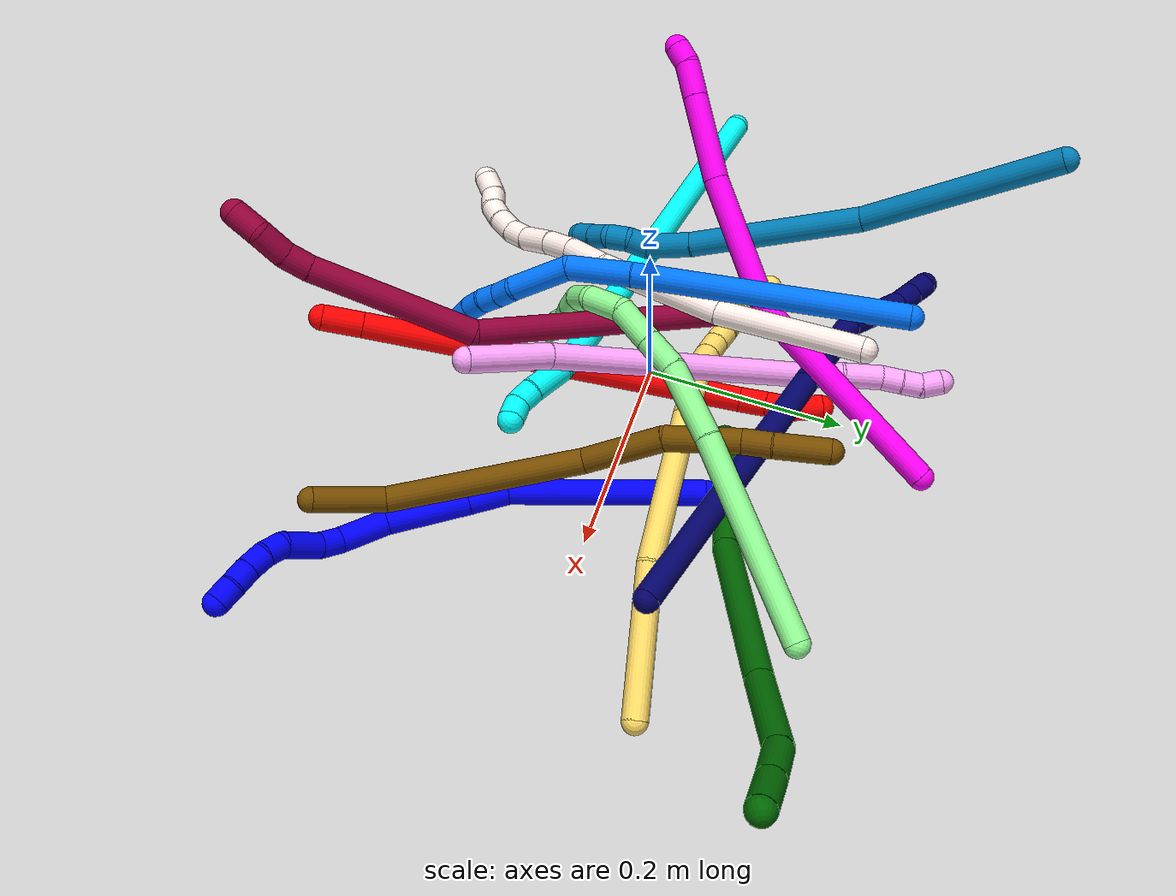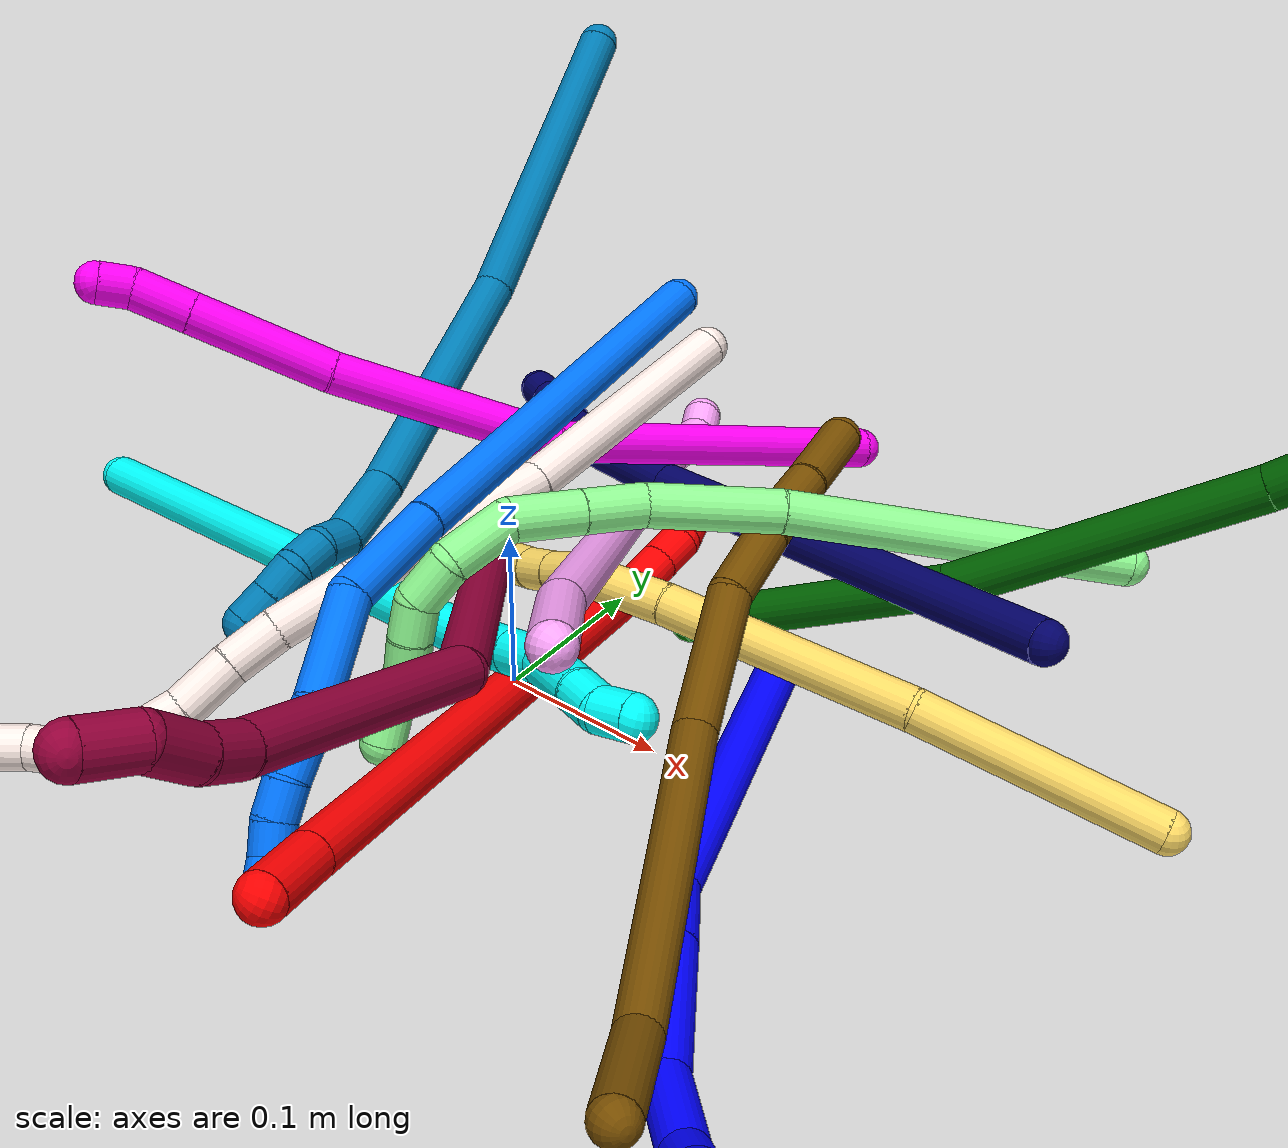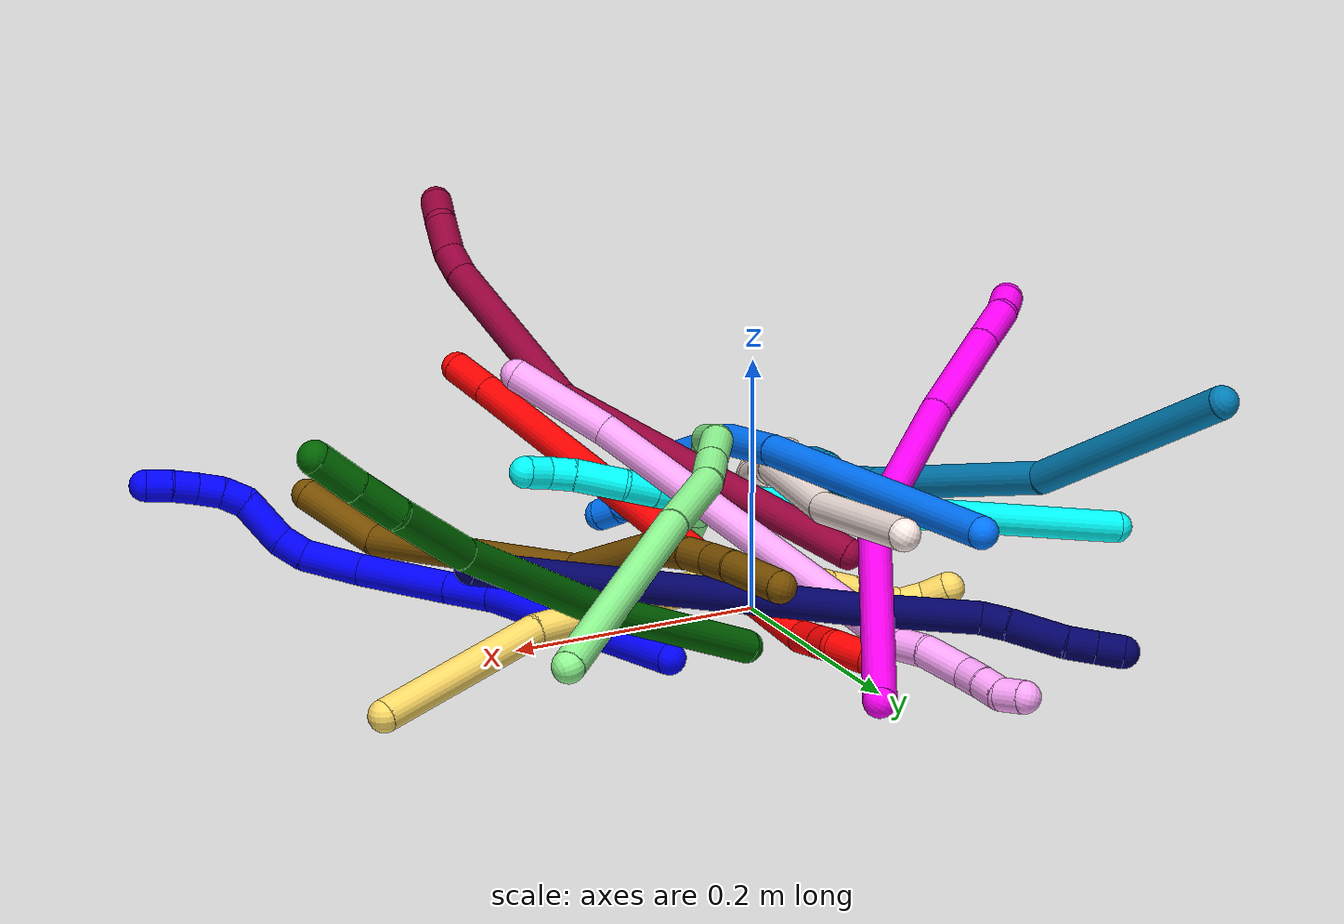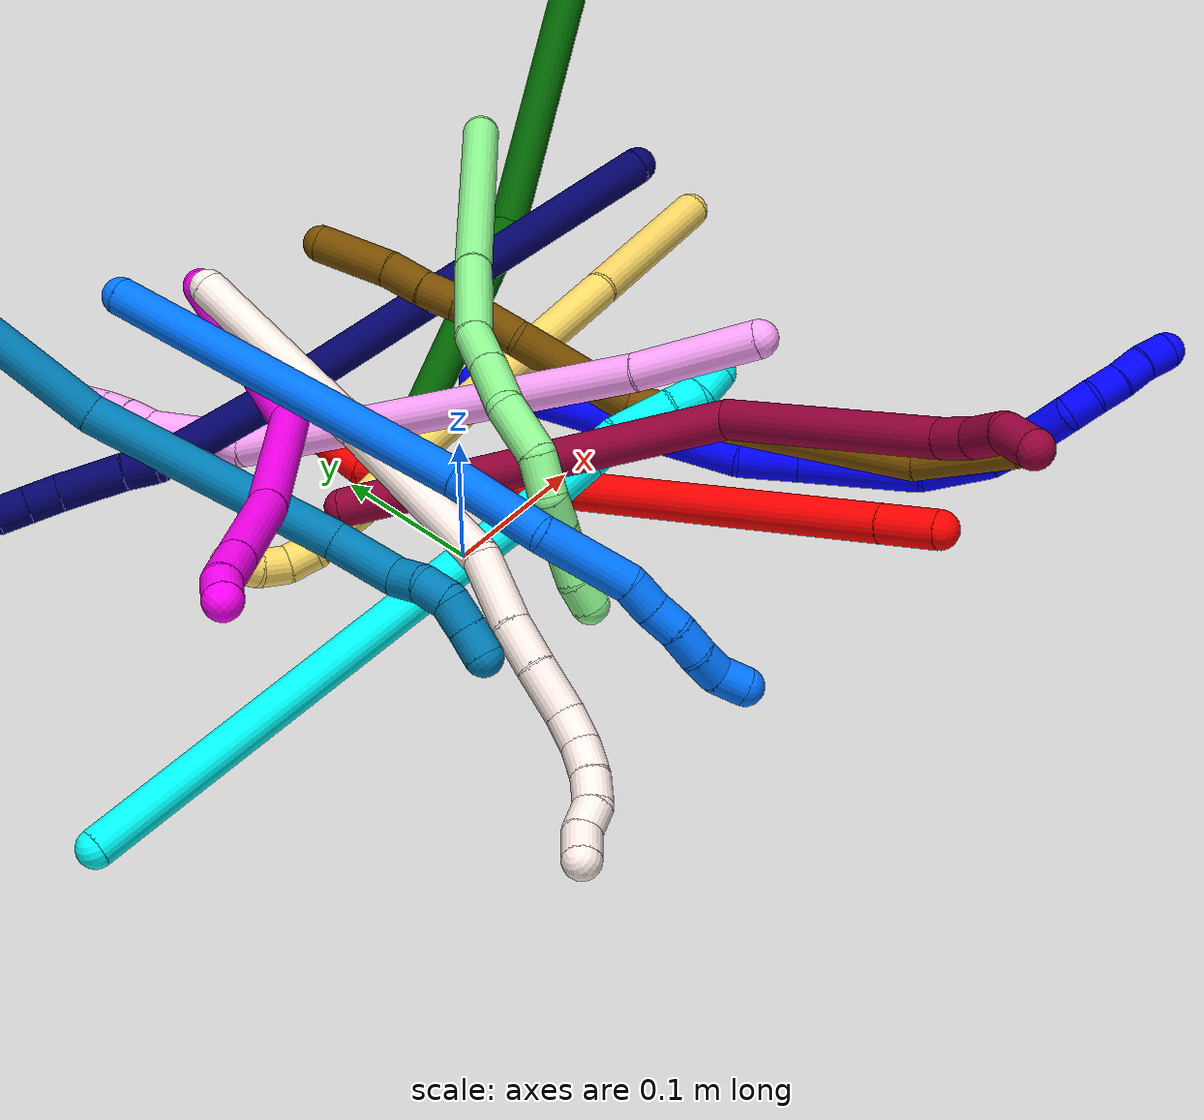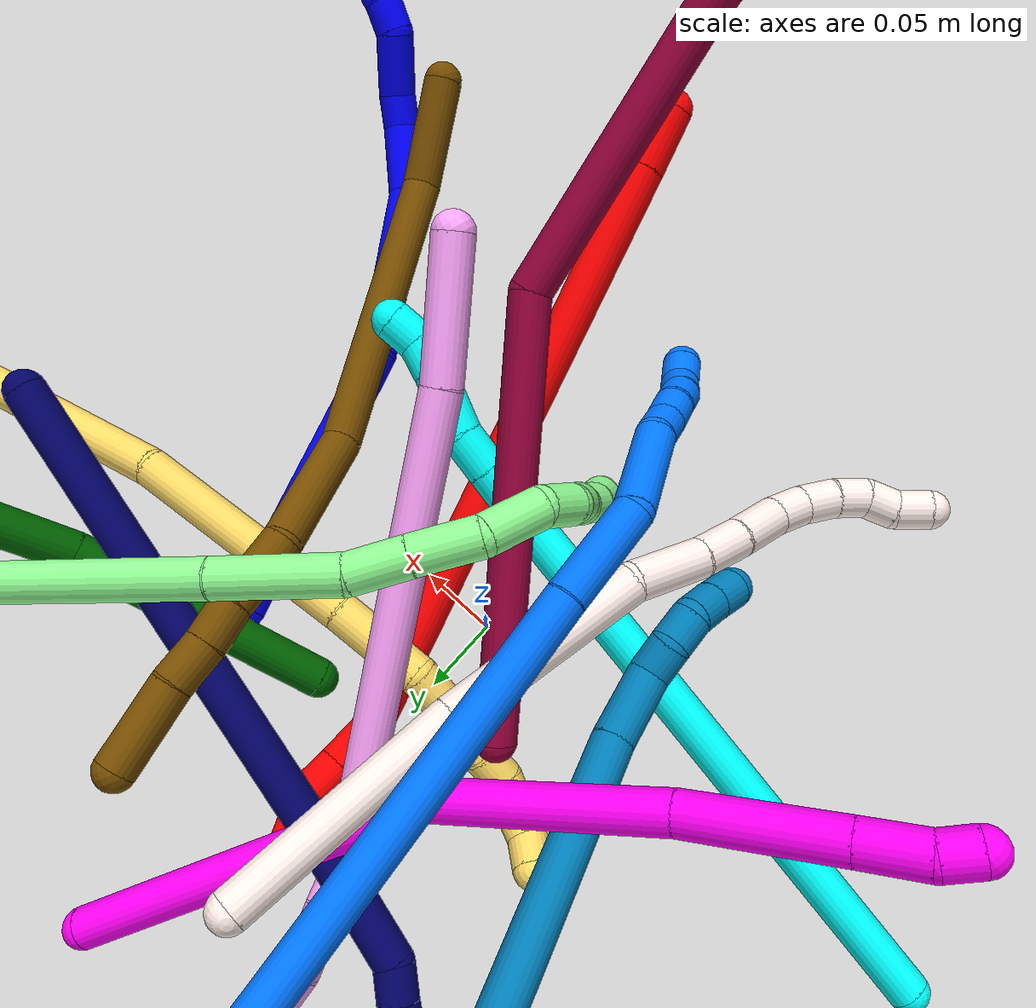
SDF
<sdf version="1.7">
 <world name="default">
  <plugin name="TubeGeneratorPlugin" filename="libtube_generator_plugin.so"/>
  <model name="photoneo_s_sensor">
   <static>1</static>
   <pose>0 0 2 1.57079 1.57079 3.14159</pose>
   <link name="link">
    <inertial><mass>0.1</mass></inertial>
    <sensor name="sensor" type="depth">
     <update_rate>30</update_rate>
     <camera>
      <horizontal_fov>1.22</horizontal_fov>
      <image><width>1920</width><height>1200</height><format>B8G8R8</format></image>
      <clip><near>0.1</near><far>4</far></clip>
      <depth_camera><output>points</output></depth_camera>
     </camera>
     <plugin name="camera_plugin" filename="libgazebo_ros_depth_camera.so">
      <baseline>0.2</baseline>
      <alwaysOn>1</alwaysOn>
      <updateRate>0.0</updateRate>
      <cameraName>camera_ir</cameraName>
      <imageTopicName>/camera/color/image_raw</imageTopicName>
      <cameraInfoTopicName>/camera/color/camera_info</cameraInfoTopicName>
      <depthImageTopicName>/camera/depth/image_raw</depthImageTopicName>
      <depthImageCameraInfoTopicName>/camera/depth/camera_info</depthImageCameraInfoTopicName>
      <pointCloudTopicName>/camera/depth/points</pointCloudTopicName>
      <frameName>fr_optical</frameName>
      <pointCloudCutoff>0.1</pointCloudCutoff>
      <pointCloudCutoffMax>2.0</pointCloudCutoffMax>
      <distortionK1>0</distortionK1>
      <distortionK2>0</distortionK2>
      <distortionK3>0</distortionK3>
      <distortionT1>0</distortionT1>
      <distortionT2>0</distortionT2>
      <CxPrime>0</CxPrime>
      <Cx>0</Cx>
      <Cy>0</Cy>
      <focalLength>0</focalLength>
      <hackBaseline>0</hackBaseline>
     </plugin>
    </sensor>
   </link>
  </model>
  <gravity>0 0 -9.8</gravity>
  <magnetic_field>6e-06 2.3e-05 -4.2e-05</magnetic_field>
  <atmosphere type="adiabatic"/>
  <physics name="default_physics" default="0" type="ode">
   <max_step_size>0.003</max_step_size>
   <real_time_factor>1</real_time_factor>
   <real_time_update_rate>1000</real_time_update_rate>
   <max_contacts>10000</max_contacts>
   <ode>
    <solver>
     <type>quick</type>
     <iters>100</iters>
     <sor>1.3</sor>
     <use_dynamic_moi_rescaling>0</use_dynamic_moi_rescaling>
    </solver>
    <constraints>
     <contact_max_correcting_vel>0</contact_max_correcting_vel>
     <contact_surface_layer>0.001</contact_surface_layer>
     <cfm>0</cfm>
     <erp>0.2</erp>
    </constraints>
   </ode>
  </physics>
  <scene><ambient>0.4 0.4 0.4 1</ambient><background>0.7 0.7 0.7 1</background><shadows>0</shadows></scene>
  <audio><device>default</device></audio>
  <spherical_coordinates>
   <surface_model>EARTH_WGS84</surface_model>
   <latitude_deg>0</latitude_deg>
   <longitude_deg>0</longitude_deg>
   <elevation>0</elevation>
   <heading_deg>0</heading_deg>
  </spherical_coordinates>
  <model name="bin">
   <static>1</static>
   <link name="bottom">
    <collision name="collision-bottom">
     <pose>0 0 -0.01 0 -0 0</pose>
     <geometry><box><size>0.8 0.6 0.02</size></box></geometry>
     <surface>
      <friction><ode><mu>100</mu><mu2>100</mu2></ode></friction>
      <contact><collide_bitmask>65535</collide_bitmask></contact>
     </surface>
    </collision>
   </link>
   <link name="west_wall">
    <collision name="collision-west_wall">
     <pose>-0.41 0 0.1 0 -0 0</pose>
     <geometry><box><size>0.02 0.6 0.2</size></box></geometry>
     <surface>
      <friction><ode><mu>100</mu><mu2>100</mu2></ode></friction>
      <contact><collide_bitmask>65535</collide_bitmask></contact>
     </surface>
    </collision>
   </link>
   <link name="east_wall">
    <collision name="collision-east_wall">
     <pose>0.41 0 0.1 0 -0 0</pose>
     <geometry><box><size>0.02 0.6 0.2</size></box></geometry>
     <surface>
      <friction><ode><mu>100</mu><mu2>100</mu2></ode></friction>
      <contact><collide_bitmask>65535</collide_bitmask></contact>
     </surface>
    </collision>
   </link>
   <link name="south_wall">
    <collision name="collision-south_wall">
     <pose>0 -0.31 0.1 0 -0 0</pose>
     <geometry><box><size>0.8 0.02 0.2</size></box></geometry>
     <surface>
      <friction><ode><mu>100</mu><mu2>100</mu2></ode></friction>
      <contact><collide_bitmask>65535</collide_bitmask></contact>
     </surface>
    </collision>
   </link>
   <link name="north_wall">
    <collision name="collision-north_wall">
     <pose>0 0.31 0.1 0 -0 0</pose>
     <geometry><box><size>0.8 0.02 0.2</size></box></geometry>
     <surface>
      <friction><ode><mu>100</mu><mu2>100</mu2></ode></friction>
      <contact><collide_bitmask>65535</collide_bitmask></contact>
     </surface>
    </collision>
   </link>
  </model>
  <model name="1">
   <static>0</static>
   <link name="1">
    <collision name="collision-cylinder-e_1_1_4">
     <pose>0.022887 -0.053199 0.075446 0.614159 0.243023 0.077408</pose>
     <geometry><cylinder><radius>0.0125</radius><length>0.190223</length></cylinder></geometry>
     <surface>
      <friction><ode><mu>1.16</mu><mu2>1.16</mu2><slip1>0</slip1><slip2>0</slip2></ode></friction>
      <contact><ode><kp>1e+06</kp><kd>1</kd><max_vel>0</max_vel><min_depth>0.001</min_depth></ode></contact>
     </surface>
    </collision>
    <visual name="visual-cylinder-e_1_1_4">
     <pose>0.022887 -0.053199 0.075446 0.614159 0.243023 0.077408</pose>
     <geometry><cylinder><radius>0.0125</radius><length>0.190223</length></cylinder></geometry>
     <material><ambient>0 0 1 1</ambient></material>
    </visual>
    <collision name="collision-cylinder-e_2_4_5">
     <pose>0.052797 -0.112438 0.168235 0.335085 0.365246 0.062449</pose>
     <geometry><cylinder><radius>0.0125</radius><length>0.03932</length></cylinder></geometry>
     <surface>
      <friction><ode><mu>1.16</mu><mu2>1.16</mu2><slip1>0</slip1><slip2>0</slip2></ode></friction>
      <contact><ode><kp>1e+06</kp><kd>1</kd><max_vel>0</max_vel><min_depth>0.001</min_depth></ode></contact>
     </surface>
    </collision>
    <visual name="visual-cylinder-e_2_4_5">
     <pose>0.052797 -0.112438 0.168235 0.335085 0.365246 0.062449</pose>
     <geometry><cylinder><radius>0.0125</radius><length>0.03932</length></cylinder></geometry>
     <material><ambient>0 0 1 1</ambient></material>
    </visual>
    <collision name="collision-cylinder-e_3_5_6">
     <pose>0.073649 -0.131169 0.220781 0.346038 0.353983 0.062498</pose>
     <geometry><cylinder><radius>0.0125</radius><length>0.079793</length></cylinder></geometry>
     <surface>
      <friction><ode><mu>1.16</mu><mu2>1.16</mu2><slip1>0</slip1><slip2>0</slip2></ode></friction>
      <contact><ode><kp>1e+06</kp><kd>1</kd><max_vel>0</max_vel><min_depth>0.001</min_depth></ode></contact>
     </surface>
    </collision>
    <visual name="visual-cylinder-e_3_5_6">
     <pose>0.073649 -0.131169 0.220781 0.346038 0.353983 0.062498</pose>
     <geometry><cylinder><radius>0.0125</radius><length>0.079793</length></cylinder></geometry>
     <material><ambient>0 0 1 1</ambient></material>
    </visual>
    <collision name="collision-cylinder-e_4_6_7">
     <pose>0.094185 -0.14523 0.278897 0.059623 0.284286 0.008535</pose>
     <geometry><cylinder><radius>0.0125</radius><length>0.047824</length></cylinder></geometry>
     <surface>
      <friction><ode><mu>1.16</mu><mu2>1.16</mu2><slip1>0</slip1><slip2>0</slip2></ode></friction>
      <contact><ode><kp>1e+06</kp><kd>1</kd><max_vel>0</max_vel><min_depth>0.001</min_depth></ode></contact>
     </surface>
    </collision>
    <visual name="visual-cylinder-e_4_6_7">
     <pose>0.094185 -0.14523 0.278897 0.059623 0.284286 0.008535</pose>
     <geometry><cylinder><radius>0.0125</radius><length>0.047824</length></cylinder></geometry>
     <material><ambient>0 0 1 1</ambient></material>
    </visual>
    <collision name="collision-cylinder-e_5_7_8">
     <pose>0.100456 -0.145637 0.312975 -0.085765 -0.038829 0.001666</pose>
     <geometry><cylinder><radius>0.0125</radius><length>0.02243</length></cylinder></geometry>
     <surface>
      <friction><ode><mu>1.16</mu><mu2>1.16</mu2><slip1>0</slip1><slip2>0</slip2></ode></friction>
      <contact><ode><kp>1e+06</kp><kd>1</kd><max_vel>0</max_vel><min_depth>0.001</min_depth></ode></contact>
     </surface>
    </collision>
    <visual name="visual-cylinder-e_5_7_8">
     <pose>0.100456 -0.145637 0.312975 -0.085765 -0.038829 0.001666</pose>
     <geometry><cylinder><radius>0.0125</radius><length>0.02243</length></cylinder></geometry>
     <material><ambient>0 0 1 1</ambient></material>
    </visual>
    <collision name="collision-cylinder-e_6_8_9">
     <pose>0.093821 -0.143916 0.342861 -0.04064 -0.319552 0.00655</pose>
     <geometry><cylinder><radius>0.0125</radius><length>0.03947</length></cylinder></geometry>
     <surface>
      <friction><ode><mu>1.16</mu><mu2>1.16</mu2><slip1>0</slip1><slip2>0</slip2></ode></friction>
      <contact><ode><kp>1e+06</kp><kd>1</kd><max_vel>0</max_vel><min_depth>0.001</min_depth></ode></contact>
     </surface>
    </collision>
    <visual name="visual-cylinder-e_6_8_9">
     <pose>0.093821 -0.143916 0.342861 -0.04064 -0.319552 0.00655</pose>
     <geometry><cylinder><radius>0.0125</radius><length>0.03947</length></cylinder></geometry>
     <material><ambient>0 0 1 1</ambient></material>
    </visual>
    <collision name="collision-cylinder-e_7_9_10">
     <pose>0.088557 -0.140317 0.371202 -0.286884 0.092935 -0.013432</pose>
     <geometry><cylinder><radius>0.0125</radius><length>0.020148</length></cylinder></geometry>
     <surface>
      <friction><ode><mu>1.16</mu><mu2>1.16</mu2><slip1>0</slip1><slip2>0</slip2></ode></friction>
      <contact><ode><kp>1e+06</kp><kd>1</kd><max_vel>0</max_vel><min_depth>0.001</min_depth></ode></contact>
     </surface>
    </collision>
    <visual name="visual-cylinder-e_7_9_10">
     <pose>0.088557 -0.140317 0.371202 -0.286884 0.092935 -0.013432</pose>
     <geometry><cylinder><radius>0.0125</radius><length>0.020148</length></cylinder></geometry>
     <material><ambient>0 0 1 1</ambient></material>
    </visual>
    <collision name="collision-cylinder-e_8_10_11">
     <pose>0.092647 -0.133839 0.389749 -0.387152 0.316293 -0.062505</pose>
     <geometry><cylinder><radius>0.0125</radius><length>0.020286</length></cylinder></geometry>
     <surface>
      <friction><ode><mu>1.16</mu><mu2>1.16</mu2><slip1>0</slip1><slip2>0</slip2></ode></friction>
      <contact><ode><kp>1e+06</kp><kd>1</kd><max_vel>0</max_vel><min_depth>0.001</min_depth></ode></contact>
     </surface>
    </collision>
    <visual name="visual-cylinder-e_8_10_11">
     <pose>0.092647 -0.133839 0.389749 -0.387152 0.316293 -0.062505</pose>
     <geometry><cylinder><radius>0.0125</radius><length>0.020286</length></cylinder></geometry>
     <material><ambient>0 0 1 1</ambient></material>
    </visual>
    <collision name="collision-cylinder-e_9_11_12">
     <pose>0.099003 -0.125431 0.407019 -0.519155 0.321632 -0.086106</pose>
     <geometry><cylinder><radius>0.0125</radius><length>0.020258</length></cylinder></geometry>
     <surface>
      <friction><ode><mu>1.16</mu><mu2>1.16</mu2><slip1>0</slip1><slip2>0</slip2></ode></friction>
      <contact><ode><kp>1e+06</kp><kd>1</kd><max_vel>0</max_vel><min_depth>0.001</min_depth></ode></contact>
     </surface>
    </collision>
    <visual name="visual-cylinder-e_9_11_12">
     <pose>0.099003 -0.125431 0.407019 -0.519155 0.321632 -0.086106</pose>
     <geometry><cylinder><radius>0.0125</radius><length>0.020258</length></cylinder></geometry>
     <material><ambient>0 0 1 1</ambient></material>
    </visual>
    <collision name="collision-cylinder-e_10_12_2">
     <pose>0.106707 -0.117044 0.423676 -0.410609 0.46085 -0.097624</pose>
     <geometry><cylinder><radius>0.0125</radius><length>0.020247</length></cylinder></geometry>
     <surface>
      <friction><ode><mu>1.16</mu><mu2>1.16</mu2><slip1>0</slip1><slip2>0</slip2></ode></friction>
      <contact><ode><kp>1e+06</kp><kd>1</kd><max_vel>0</max_vel><min_depth>0.001</min_depth></ode></contact>
     </surface>
    </collision>
    <visual name="visual-cylinder-e_10_12_2">
     <pose>0.106707 -0.117044 0.423676 -0.410609 0.46085 -0.097624</pose>
     <geometry><cylinder><radius>0.0125</radius><length>0.020247</length></cylinder></geometry>
     <material><ambient>0 0 1 1</ambient></material>
    </visual>
    <collision name="collision-sphere-2">
     <pose>0.111209 -0.113425 0.43199 0 -0 0</pose>
     <geometry><sphere><radius>0.0125</radius></sphere></geometry>
     <surface>
      <friction><ode><mu>1.16</mu><mu2>1.16</mu2><slip1>0</slip1><slip2>0</slip2></ode></friction>
      <contact><ode><kp>1e+06</kp><kd>1</kd><max_vel>0</max_vel><min_depth>0.001</min_depth></ode></contact>
     </surface>
    </collision>
    <visual name="visual-sphere-2">
     <pose>0.111209 -0.113425 0.43199 0 -0 0</pose>
     <geometry><sphere><radius>0.0125</radius></sphere></geometry>
     <material><ambient>0 0 1 1</ambient></material>
    </visual>
    <collision name="collision-sphere-12">
     <pose>0.102205 -0.120664 0.415362 0 -0 0</pose>
     <geometry><sphere><radius>0.0125</radius></sphere></geometry>
     <surface>
      <friction><ode><mu>1.16</mu><mu2>1.16</mu2><slip1>0</slip1><slip2>0</slip2></ode></friction>
      <contact><ode><kp>1e+06</kp><kd>1</kd><max_vel>0</max_vel><min_depth>0.001</min_depth></ode></contact>
     </surface>
    </collision>
    <visual name="visual-sphere-12">
     <pose>0.102205 -0.120664 0.415362 0 -0 0</pose>
     <geometry><sphere><radius>0.0125</radius></sphere></geometry>
     <material><ambient>0 0 1 1</ambient></material>
    </visual>
    <collision name="collision-sphere-11">
     <pose>0.095802 -0.130199 0.398676 0 -0 0</pose>
     <geometry><sphere><radius>0.0125</radius></sphere></geometry>
     <surface>
      <friction><ode><mu>1.16</mu><mu2>1.16</mu2><slip1>0</slip1><slip2>0</slip2></ode></friction>
      <contact><ode><kp>1e+06</kp><kd>1</kd><max_vel>0</max_vel><min_depth>0.001</min_depth></ode></contact>
     </surface>
    </collision>
    <visual name="visual-sphere-11">
     <pose>0.095802 -0.130199 0.398676 0 -0 0</pose>
     <geometry><sphere><radius>0.0125</radius></sphere></geometry>
     <material><ambient>0 0 1 1</ambient></material>
    </visual>
    <collision name="collision-sphere-10">
     <pose>0.089492 -0.137478 0.380823 0 -0 0</pose>
     <geometry><sphere><radius>0.0125</radius></sphere></geometry>
     <surface>
      <friction><ode><mu>1.16</mu><mu2>1.16</mu2><slip1>0</slip1><slip2>0</slip2></ode></friction>
      <contact><ode><kp>1e+06</kp><kd>1</kd><max_vel>0</max_vel><min_depth>0.001</min_depth></ode></contact>
     </surface>
    </collision>
    <visual name="visual-sphere-10">
     <pose>0.089492 -0.137478 0.380823 0 -0 0</pose>
     <geometry><sphere><radius>0.0125</radius></sphere></geometry>
     <material><ambient>0 0 1 1</ambient></material>
    </visual>
    <collision name="collision-sphere-9">
     <pose>0.087622 -0.143155 0.361581 0 -0 0</pose>
     <geometry><sphere><radius>0.0125</radius></sphere></geometry>
     <surface>
      <friction><ode><mu>1.16</mu><mu2>1.16</mu2><slip1>0</slip1><slip2>0</slip2></ode></friction>
      <contact><ode><kp>1e+06</kp><kd>1</kd><max_vel>0</max_vel><min_depth>0.001</min_depth></ode></contact>
     </surface>
    </collision>
    <visual name="visual-sphere-9">
     <pose>0.087622 -0.143155 0.361581 0 -0 0</pose>
     <geometry><sphere><radius>0.0125</radius></sphere></geometry>
     <material><ambient>0 0 1 1</ambient></material>
    </visual>
    <collision name="collision-sphere-4">
     <pose>0.045775 -0.106399 0.150893 0 -0 0</pose>
     <geometry><sphere><radius>0.0125</radius></sphere></geometry>
     <surface>
      <friction><ode><mu>1.16</mu><mu2>1.16</mu2><slip1>0</slip1><slip2>0</slip2></ode></friction>
      <contact><ode><kp>1e+06</kp><kd>1</kd><max_vel>0</max_vel><min_depth>0.001</min_depth></ode></contact>
     </surface>
    </collision>
    <visual name="visual-sphere-4">
     <pose>0.045775 -0.106399 0.150893 0 -0 0</pose>
     <geometry><sphere><radius>0.0125</radius></sphere></geometry>
     <material><ambient>0 0 1 1</ambient></material>
    </visual>
    <collision name="collision-sphere-1">
     <geometry><sphere><radius>0.0125</radius></sphere></geometry>
     <surface>
      <friction><ode><mu>1.16</mu><mu2>1.16</mu2><slip1>0</slip1><slip2>0</slip2></ode></friction>
      <contact><ode><kp>1e+06</kp><kd>1</kd><max_vel>0</max_vel><min_depth>0.001</min_depth></ode></contact>
     </surface>
    </collision>
    <visual name="visual-sphere-1">
     <geometry><sphere><radius>0.0125</radius></sphere></geometry>
     <material><ambient>0 0 1 1</ambient></material>
    </visual>
    <collision name="collision-sphere-8">
     <pose>0.100021 -0.144677 0.32414 0 -0 0</pose>
     <geometry><sphere><radius>0.0125</radius></sphere></geometry>
     <surface>
      <friction><ode><mu>1.16</mu><mu2>1.16</mu2><slip1>0</slip1><slip2>0</slip2></ode></friction>
      <contact><ode><kp>1e+06</kp><kd>1</kd><max_vel>0</max_vel><min_depth>0.001</min_depth></ode></contact>
     </surface>
    </collision>
    <visual name="visual-sphere-8">
     <pose>0.100021 -0.144677 0.32414 0 -0 0</pose>
     <geometry><sphere><radius>0.0125</radius></sphere></geometry>
     <material><ambient>0 0 1 1</ambient></material>
    </visual>
    <collision name="collision-sphere-5">
     <pose>0.059819 -0.118476 0.185577 0 -0 0</pose>
     <geometry><sphere><radius>0.0125</radius></sphere></geometry>
     <surface>
      <friction><ode><mu>1.16</mu><mu2>1.16</mu2><slip1>0</slip1><slip2>0</slip2></ode></friction>
      <contact><ode><kp>1e+06</kp><kd>1</kd><max_vel>0</max_vel><min_depth>0.001</min_depth></ode></contact>
     </surface>
    </collision>
    <visual name="visual-sphere-5">
     <pose>0.059819 -0.118476 0.185577 0 -0 0</pose>
     <geometry><sphere><radius>0.0125</radius></sphere></geometry>
     <material><ambient>0 0 1 1</ambient></material>
    </visual>
    <collision name="collision-sphere-6">
     <pose>0.087478 -0.143862 0.255986 0 -0 0</pose>
     <geometry><sphere><radius>0.0125</radius></sphere></geometry>
     <surface>
      <friction><ode><mu>1.16</mu><mu2>1.16</mu2><slip1>0</slip1><slip2>0</slip2></ode></friction>
      <contact><ode><kp>1e+06</kp><kd>1</kd><max_vel>0</max_vel><min_depth>0.001</min_depth></ode></contact>
     </surface>
    </collision>
    <visual name="visual-sphere-6">
     <pose>0.087478 -0.143862 0.255986 0 -0 0</pose>
     <geometry><sphere><radius>0.0125</radius></sphere></geometry>
     <material><ambient>0 0 1 1</ambient></material>
    </visual>
    <collision name="collision-sphere-7">
     <pose>0.100892 -0.146597 0.301809 0 -0 0</pose>
     <geometry><sphere><radius>0.0125</radius></sphere></geometry>
     <surface>
      <friction><ode><mu>1.16</mu><mu2>1.16</mu2><slip1>0</slip1><slip2>0</slip2></ode></friction>
      <contact><ode><kp>1e+06</kp><kd>1</kd><max_vel>0</max_vel><min_depth>0.001</min_depth></ode></contact>
     </surface>
    </collision>
    <visual name="visual-sphere-7">
     <pose>0.100892 -0.146597 0.301809 0 -0 0</pose>
     <geometry><sphere><radius>0.0125</radius></sphere></geometry>
     <material><ambient>0 0 1 1</ambient></material>
    </visual>
    <inertial>
     <pose>0.061194 -0.102705 0.209367 0 -0 0</pose>
     <mass>0.5</mass>
     <inertia>
      <ixx>0.00069</ixx>
      <ixy>0</ixy>
      <ixz>0</ixz>
      <iyy>0.000591</iyy>
      <iyz>0</iyz>
      <izz>0.000213</izz>
     </inertia>
    </inertial>
   </link>
   <pose>0.119695 0.096034 0.013007 0.530638 1.04086 -0.17504</pose>
  </model>
  <model name="2">
   <static>0</static>
   <link name="2">
    <collision name="collision-cylinder-e_1_1_4">
     <pose>-0.004431 0.016412 -0.008983 -2.07158 -0.232524 0.389127</pose>
     <geometry><cylinder><radius>0.0125</radius><length>0.038455</length></cylinder></geometry>
     <surface>
      <friction><ode><mu>1.16</mu><mu2>1.16</mu2><slip1>0</slip1><slip2>0</slip2></ode></friction>
      <contact><ode><kp>1e+06</kp><kd>1</kd><max_vel>0</max_vel><min_depth>0.001</min_depth></ode></contact>
     </surface>
    </collision>
    <visual name="visual-cylinder-e_1_1_4">
     <pose>-0.004431 0.016412 -0.008983 -2.07158 -0.232524 0.389127</pose>
     <geometry><cylinder><radius>0.0125</radius><length>0.038455</length></cylinder></geometry>
     <material><ambient>1 0 0 1</ambient></material>
    </visual>
    <collision name="collision-cylinder-e_2_4_5">
     <pose>-0.052749 0.192548 -0.108325 -2.08563 -0.234749 0.398995</pose>
     <geometry><cylinder><radius>0.0125</radius><length>0.377372</length></cylinder></geometry>
     <surface>
      <friction><ode><mu>1.16</mu><mu2>1.16</mu2><slip1>0</slip1><slip2>0</slip2></ode></friction>
      <contact><ode><kp>1e+06</kp><kd>1</kd><max_vel>0</max_vel><min_depth>0.001</min_depth></ode></contact>
     </surface>
    </collision>
    <visual name="visual-cylinder-e_2_4_5">
     <pose>-0.052749 0.192548 -0.108325 -2.08563 -0.234749 0.398995</pose>
     <geometry><cylinder><radius>0.0125</radius><length>0.377372</length></cylinder></geometry>
     <material><ambient>1 0 0 1</ambient></material>
    </visual>
    <collision name="collision-cylinder-e_3_5_6">
     <pose>-0.092489 0.365053 -0.205142 -2.03857 0.281924 -0.453404</pose>
     <geometry><cylinder><radius>0.0125</radius><length>0.02982</length></cylinder></geometry>
     <surface>
      <friction><ode><mu>1.16</mu><mu2>1.16</mu2><slip1>0</slip1><slip2>0</slip2></ode></friction>
      <contact><ode><kp>1e+06</kp><kd>1</kd><max_vel>0</max_vel><min_depth>0.001</min_depth></ode></contact>
     </surface>
    </collision>
    <visual name="visual-cylinder-e_3_5_6">
     <pose>-0.092489 0.365053 -0.205142 -2.03857 0.281924 -0.453404</pose>
     <geometry><cylinder><radius>0.0125</radius><length>0.02982</length></cylinder></geometry>
     <material><ambient>1 0 0 1</ambient></material>
    </visual>
    <collision name="collision-cylinder-e_4_6_7">
     <pose>-0.084763 0.387076 -0.216446 -2.05382 0.330384 -0.537996</pose>
     <geometry><cylinder><radius>0.0125</radius><length>0.022061</length></cylinder></geometry>
     <surface>
      <friction><ode><mu>1.16</mu><mu2>1.16</mu2><slip1>0</slip1><slip2>0</slip2></ode></friction>
      <contact><ode><kp>1e+06</kp><kd>1</kd><max_vel>0</max_vel><min_depth>0.001</min_depth></ode></contact>
     </surface>
    </collision>
    <visual name="visual-cylinder-e_4_6_7">
     <pose>-0.084763 0.387076 -0.216446 -2.05382 0.330384 -0.537996</pose>
     <geometry><cylinder><radius>0.0125</radius><length>0.022061</length></cylinder></geometry>
     <material><ambient>1 0 0 1</ambient></material>
    </visual>
    <collision name="collision-cylinder-e_5_7_2">
     <pose>-0.082851 0.411738 -0.225778 -1.85387 -0.103366 0.137624</pose>
     <geometry><cylinder><radius>0.0125</radius><length>0.032292</length></cylinder></geometry>
     <surface>
      <friction><ode><mu>1.16</mu><mu2>1.16</mu2><slip1>0</slip1><slip2>0</slip2></ode></friction>
      <contact><ode><kp>1e+06</kp><kd>1</kd><max_vel>0</max_vel><min_depth>0.001</min_depth></ode></contact>
     </surface>
    </collision>
    <visual name="visual-cylinder-e_5_7_2">
     <pose>-0.082851 0.411738 -0.225778 -1.85387 -0.103366 0.137624</pose>
     <geometry><cylinder><radius>0.0125</radius><length>0.032292</length></cylinder></geometry>
     <material><ambient>1 0 0 1</ambient></material>
    </visual>
    <collision name="collision-sphere-2">
     <pose>-0.084517 0.427159 -0.230264 0 -0 0</pose>
     <geometry><sphere><radius>0.0125</radius></sphere></geometry>
     <surface>
      <friction><ode><mu>1.16</mu><mu2>1.16</mu2><slip1>0</slip1><slip2>0</slip2></ode></friction>
      <contact><ode><kp>1e+06</kp><kd>1</kd><max_vel>0</max_vel><min_depth>0.001</min_depth></ode></contact>
     </surface>
    </collision>
    <visual name="visual-sphere-2">
     <pose>-0.084517 0.427159 -0.230264 0 -0 0</pose>
     <geometry><sphere><radius>0.0125</radius></sphere></geometry>
     <material><ambient>1 0 0 1</ambient></material>
    </visual>
    <collision name="collision-sphere-7">
     <pose>-0.081185 0.396317 -0.221292 0 -0 0</pose>
     <geometry><sphere><radius>0.0125</radius></sphere></geometry>
     <surface>
      <friction><ode><mu>1.16</mu><mu2>1.16</mu2><slip1>0</slip1><slip2>0</slip2></ode></friction>
      <contact><ode><kp>1e+06</kp><kd>1</kd><max_vel>0</max_vel><min_depth>0.001</min_depth></ode></contact>
     </surface>
    </collision>
    <visual name="visual-sphere-7">
     <pose>-0.081185 0.396317 -0.221292 0 -0 0</pose>
     <geometry><sphere><radius>0.0125</radius></sphere></geometry>
     <material><ambient>1 0 0 1</ambient></material>
    </visual>
    <collision name="collision-sphere-6">
     <pose>-0.088341 0.377836 -0.2116 0 -0 0</pose>
     <geometry><sphere><radius>0.0125</radius></sphere></geometry>
     <surface>
      <friction><ode><mu>1.16</mu><mu2>1.16</mu2><slip1>0</slip1><slip2>0</slip2></ode></friction>
      <contact><ode><kp>1e+06</kp><kd>1</kd><max_vel>0</max_vel><min_depth>0.001</min_depth></ode></contact>
     </surface>
    </collision>
    <visual name="visual-sphere-6">
     <pose>-0.088341 0.377836 -0.2116 0 -0 0</pose>
     <geometry><sphere><radius>0.0125</radius></sphere></geometry>
     <material><ambient>1 0 0 1</ambient></material>
    </visual>
    <collision name="collision-sphere-5">
     <pose>-0.096637 0.35227 -0.198685 0 -0 0</pose>
     <geometry><sphere><radius>0.0125</radius></sphere></geometry>
     <surface>
      <friction><ode><mu>1.16</mu><mu2>1.16</mu2><slip1>0</slip1><slip2>0</slip2></ode></friction>
      <contact><ode><kp>1e+06</kp><kd>1</kd><max_vel>0</max_vel><min_depth>0.001</min_depth></ode></contact>
     </surface>
    </collision>
    <visual name="visual-sphere-5">
     <pose>-0.096637 0.35227 -0.198685 0 -0 0</pose>
     <geometry><sphere><radius>0.0125</radius></sphere></geometry>
     <material><ambient>1 0 0 1</ambient></material>
    </visual>
    <collision name="collision-sphere-1">
     <geometry><sphere><radius>0.0125</radius></sphere></geometry>
     <surface>
      <friction><ode><mu>1.16</mu><mu2>1.16</mu2><slip1>0</slip1><slip2>0</slip2></ode></friction>
      <contact><ode><kp>1e+06</kp><kd>1</kd><max_vel>0</max_vel><min_depth>0.001</min_depth></ode></contact>
     </surface>
    </collision>
    <visual name="visual-sphere-1">
     <geometry><sphere><radius>0.0125</radius></sphere></geometry>
     <material><ambient>1 0 0 1</ambient></material>
    </visual>
    <collision name="collision-sphere-4">
     <pose>-0.008861 0.032825 -0.017965 0 -0 0</pose>
     <geometry><sphere><radius>0.0125</radius></sphere></geometry>
     <surface>
      <friction><ode><mu>1.16</mu><mu2>1.16</mu2><slip1>0</slip1><slip2>0</slip2></ode></friction>
      <contact><ode><kp>1e+06</kp><kd>1</kd><max_vel>0</max_vel><min_depth>0.001</min_depth></ode></contact>
     </surface>
    </collision>
    <visual name="visual-sphere-4">
     <pose>-0.008861 0.032825 -0.017965 0 -0 0</pose>
     <geometry><sphere><radius>0.0125</radius></sphere></geometry>
     <material><ambient>1 0 0 1</ambient></material>
    </visual>
    <inertial>
     <pose>-0.05476 0.212029 -0.118815 0 -0 0</pose>
     <mass>0.5</mass>
     <inertia>
      <ixx>0.005732</ixx>
      <ixy>0</ixy>
      <ixz>0</ixz>
      <iyy>4.2e-05</iyy>
      <iyz>0</iyz>
      <izz>-0.00279</izz>
     </inertia>
    </inertial>
   </link>
   <pose>0.113692 -0.288507 0.128217 0.350796 -0.993629 0.270817</pose>
  </model>
  <model name="3">
   <static>0</static>
   <link name="3">
    <collision name="collision-cylinder-e_1_1_4">
     <pose>0.173265 -0.039573 0.027003 0.972006 1.30104 0.764496</pose>
     <geometry><cylinder><radius>0.0125</radius><length>0.359533</length></cylinder></geometry>
     <surface>
      <friction><ode><mu>1.16</mu><mu2>1.16</mu2><slip1>0</slip1><slip2>0</slip2></ode></friction>
      <contact><ode><kp>1e+06</kp><kd>1</kd><max_vel>0</max_vel><min_depth>0.001</min_depth></ode></contact>
     </surface>
    </collision>
    <visual name="visual-cylinder-e_1_1_4">
     <pose>0.173265 -0.039573 0.027003 0.972006 1.30104 0.764496</pose>
     <geometry><cylinder><radius>0.0125</radius><length>0.359533</length></cylinder></geometry>
     <material><ambient>0.003922 1 0.996078 1</ambient></material>
    </visual>
    <collision name="collision-cylinder-e_2_4_5">
     <pose>0.362884 -0.083764 0.05817 0.837104 1.20741 0.595286</pose>
     <geometry><cylinder><radius>0.0125</radius><length>0.034991</length></cylinder></geometry>
     <surface>
      <friction><ode><mu>1.16</mu><mu2>1.16</mu2><slip1>0</slip1><slip2>0</slip2></ode></friction>
      <contact><ode><kp>1e+06</kp><kd>1</kd><max_vel>0</max_vel><min_depth>0.001</min_depth></ode></contact>
     </surface>
    </collision>
    <visual name="visual-cylinder-e_2_4_5">
     <pose>0.362884 -0.083764 0.05817 0.837104 1.20741 0.595286</pose>
     <geometry><cylinder><radius>0.0125</radius><length>0.034991</length></cylinder></geometry>
     <material><ambient>0.003922 1 0.996078 1</ambient></material>
    </visual>
    <collision name="collision-cylinder-e_3_5_6">
     <pose>0.391058 -0.091867 0.06565 0.810282 1.18434 0.561747</pose>
     <geometry><cylinder><radius>0.0125</radius><length>0.025524</length></cylinder></geometry>
     <surface>
      <friction><ode><mu>1.16</mu><mu2>1.16</mu2><slip1>0</slip1><slip2>0</slip2></ode></friction>
      <contact><ode><kp>1e+06</kp><kd>1</kd><max_vel>0</max_vel><min_depth>0.001</min_depth></ode></contact>
     </surface>
    </collision>
    <visual name="visual-cylinder-e_3_5_6">
     <pose>0.391058 -0.091867 0.06565 0.810282 1.18434 0.561747</pose>
     <geometry><cylinder><radius>0.0125</radius><length>0.025524</length></cylinder></geometry>
     <material><ambient>0.003922 1 0.996078 1</ambient></material>
    </visual>
    <collision name="collision-cylinder-e_4_6_7">
     <pose>0.420152 -0.104708 0.070753 1.38201 1.06684 0.908609</pose>
     <geometry><cylinder><radius>0.0125</radius><length>0.03945</length></cylinder></geometry>
     <surface>
      <friction><ode><mu>1.16</mu><mu2>1.16</mu2><slip1>0</slip1><slip2>0</slip2></ode></friction>
      <contact><ode><kp>1e+06</kp><kd>1</kd><max_vel>0</max_vel><min_depth>0.001</min_depth></ode></contact>
     </surface>
    </collision>
    <visual name="visual-cylinder-e_4_6_7">
     <pose>0.420152 -0.104708 0.070753 1.38201 1.06684 0.908609</pose>
     <geometry><cylinder><radius>0.0125</radius><length>0.03945</length></cylinder></geometry>
     <material><ambient>0.003922 1 0.996078 1</ambient></material>
    </visual>
    <collision name="collision-cylinder-e_5_7_8">
     <pose>0.446842 -0.117977 0.072714 1.52638 1.17663 1.13596</pose>
     <geometry><cylinder><radius>0.0125</radius><length>0.020399</length></cylinder></geometry>
     <surface>
      <friction><ode><mu>1.16</mu><mu2>1.16</mu2><slip1>0</slip1><slip2>0</slip2></ode></friction>
      <contact><ode><kp>1e+06</kp><kd>1</kd><max_vel>0</max_vel><min_depth>0.001</min_depth></ode></contact>
     </surface>
    </collision>
    <visual name="visual-cylinder-e_5_7_8">
     <pose>0.446842 -0.117977 0.072714 1.52638 1.17663 1.13596</pose>
     <geometry><cylinder><radius>0.0125</radius><length>0.020399</length></cylinder></geometry>
     <material><ambient>0.003922 1 0.996078 1</ambient></material>
    </visual>
    <collision name="collision-cylinder-e_6_8_2">
     <pose>0.465987 -0.122379 0.075369 0.194176 1.31653 0.150352</pose>
     <geometry><cylinder><radius>0.0125</radius><length>0.020102</length></cylinder></geometry>
     <surface>
      <friction><ode><mu>1.16</mu><mu2>1.16</mu2><slip1>0</slip1><slip2>0</slip2></ode></friction>
      <contact><ode><kp>1e+06</kp><kd>1</kd><max_vel>0</max_vel><min_depth>0.001</min_depth></ode></contact>
     </surface>
    </collision>
    <visual name="visual-cylinder-e_6_8_2">
     <pose>0.465987 -0.122379 0.075369 0.194176 1.31653 0.150352</pose>
     <geometry><cylinder><radius>0.0125</radius><length>0.020102</length></cylinder></geometry>
     <material><ambient>0.003922 1 0.996078 1</ambient></material>
    </visual>
    <collision name="collision-sphere-2">
     <pose>0.475715 -0.122866 0.077849 0 -0 0</pose>
     <geometry><sphere><radius>0.0125</radius></sphere></geometry>
     <surface>
      <friction><ode><mu>1.16</mu><mu2>1.16</mu2><slip1>0</slip1><slip2>0</slip2></ode></friction>
      <contact><ode><kp>1e+06</kp><kd>1</kd><max_vel>0</max_vel><min_depth>0.001</min_depth></ode></contact>
     </surface>
    </collision>
    <visual name="visual-sphere-2">
     <pose>0.475715 -0.122866 0.077849 0 -0 0</pose>
     <geometry><sphere><radius>0.0125</radius></sphere></geometry>
     <material><ambient>0.003922 1 0.996078 1</ambient></material>
    </visual>
    <collision name="collision-sphere-4">
     <pose>0.34653 -0.079145 0.054006 0 -0 0</pose>
     <geometry><sphere><radius>0.0125</radius></sphere></geometry>
     <surface>
      <friction><ode><mu>1.16</mu><mu2>1.16</mu2><slip1>0</slip1><slip2>0</slip2></ode></friction>
      <contact><ode><kp>1e+06</kp><kd>1</kd><max_vel>0</max_vel><min_depth>0.001</min_depth></ode></contact>
     </surface>
    </collision>
    <visual name="visual-sphere-4">
     <pose>0.34653 -0.079145 0.054006 0 -0 0</pose>
     <geometry><sphere><radius>0.0125</radius></sphere></geometry>
     <material><ambient>0.003922 1 0.996078 1</ambient></material>
    </visual>
    <collision name="collision-sphere-1">
     <geometry><sphere><radius>0.0125</radius></sphere></geometry>
     <surface>
      <friction><ode><mu>1.16</mu><mu2>1.16</mu2><slip1>0</slip1><slip2>0</slip2></ode></friction>
      <contact><ode><kp>1e+06</kp><kd>1</kd><max_vel>0</max_vel><min_depth>0.001</min_depth></ode></contact>
     </surface>
    </collision>
    <visual name="visual-sphere-1">
     <geometry><sphere><radius>0.0125</radius></sphere></geometry>
     <material><ambient>0.003922 1 0.996078 1</ambient></material>
    </visual>
    <collision name="collision-sphere-8">
     <pose>0.45626 -0.121891 0.072888 0 -0 0</pose>
     <geometry><sphere><radius>0.0125</radius></sphere></geometry>
     <surface>
      <friction><ode><mu>1.16</mu><mu2>1.16</mu2><slip1>0</slip1><slip2>0</slip2></ode></friction>
      <contact><ode><kp>1e+06</kp><kd>1</kd><max_vel>0</max_vel><min_depth>0.001</min_depth></ode></contact>
     </surface>
    </collision>
    <visual name="visual-sphere-8">
     <pose>0.45626 -0.121891 0.072888 0 -0 0</pose>
     <geometry><sphere><radius>0.0125</radius></sphere></geometry>
     <material><ambient>0.003922 1 0.996078 1</ambient></material>
    </visual>
    <collision name="collision-sphere-5">
     <pose>0.379237 -0.088383 0.062334 0 -0 0</pose>
     <geometry><sphere><radius>0.0125</radius></sphere></geometry>
     <surface>
      <friction><ode><mu>1.16</mu><mu2>1.16</mu2><slip1>0</slip1><slip2>0</slip2></ode></friction>
      <contact><ode><kp>1e+06</kp><kd>1</kd><max_vel>0</max_vel><min_depth>0.001</min_depth></ode></contact>
     </surface>
    </collision>
    <visual name="visual-sphere-5">
     <pose>0.379237 -0.088383 0.062334 0 -0 0</pose>
     <geometry><sphere><radius>0.0125</radius></sphere></geometry>
     <material><ambient>0.003922 1 0.996078 1</ambient></material>
    </visual>
    <collision name="collision-sphere-6">
     <pose>0.402879 -0.095352 0.068965 0 -0 0</pose>
     <geometry><sphere><radius>0.0125</radius></sphere></geometry>
     <surface>
      <friction><ode><mu>1.16</mu><mu2>1.16</mu2><slip1>0</slip1><slip2>0</slip2></ode></friction>
      <contact><ode><kp>1e+06</kp><kd>1</kd><max_vel>0</max_vel><min_depth>0.001</min_depth></ode></contact>
     </surface>
    </collision>
    <visual name="visual-sphere-6">
     <pose>0.402879 -0.095352 0.068965 0 -0 0</pose>
     <geometry><sphere><radius>0.0125</radius></sphere></geometry>
     <material><ambient>0.003922 1 0.996078 1</ambient></material>
    </visual>
    <collision name="collision-sphere-7">
     <pose>0.437425 -0.114064 0.07254 0 -0 0</pose>
     <geometry><sphere><radius>0.0125</radius></sphere></geometry>
     <surface>
      <friction><ode><mu>1.16</mu><mu2>1.16</mu2><slip1>0</slip1><slip2>0</slip2></ode></friction>
      <contact><ode><kp>1e+06</kp><kd>1</kd><max_vel>0</max_vel><min_depth>0.001</min_depth></ode></contact>
     </surface>
    </collision>
    <visual name="visual-sphere-7">
     <pose>0.437425 -0.114064 0.07254 0 -0 0</pose>
     <geometry><sphere><radius>0.0125</radius></sphere></geometry>
     <material><ambient>0.003922 1 0.996078 1</ambient></material>
    </visual>
    <inertial>
     <pose>0.240063 -0.057002 0.038418 0 -0 0</pose>
     <mass>0.5</mass>
     <inertia>
      <ixx>0.001511</ixx>
      <ixy>0</ixy>
      <ixz>0</ixz>
      <iyy>0.00445</iyy>
      <iyz>0</iyz>
      <izz>-0.002894</izz>
     </inertia>
    </inertial>
   </link>
   <pose>-0.331046 -0.007339 0.011494 -0.404971 0.048988 0.009121</pose>
  </model>
  <model name="4">
   <static>0</static>
   <link name="4">
    <collision name="collision-cylinder-e_1_1_4">
     <pose>-0.012251 0.02252 -0.032454 -2.53498 -0.30074 0.901745</pose>
     <geometry><cylinder><radius>0.0125</radius><length>0.082717</length></cylinder></geometry>
     <surface>
      <friction><ode><mu>1.16</mu><mu2>1.16</mu2><slip1>0</slip1><slip2>0</slip2></ode></friction>
      <contact><ode><kp>1e+06</kp><kd>1</kd><max_vel>0</max_vel><min_depth>0.001</min_depth></ode></contact>
     </surface>
    </collision>
    <visual name="visual-cylinder-e_1_1_4">
     <pose>-0.012251 0.02252 -0.032454 -2.53498 -0.30074 0.901745</pose>
     <geometry><cylinder><radius>0.0125</radius><length>0.082717</length></cylinder></geometry>
     <material><ambient>1 0.65098 0.996078 1</ambient></material>
    </visual>
    <collision name="collision-cylinder-e_2_4_5">
     <pose>-0.072065 0.13614 -0.166038 -2.40831 -0.336167 0.832167</pose>
     <geometry><cylinder><radius>0.0125</radius><length>0.288365</length></cylinder></geometry>
     <surface>
      <friction><ode><mu>1.16</mu><mu2>1.16</mu2><slip1>0</slip1><slip2>0</slip2></ode></friction>
      <contact><ode><kp>1e+06</kp><kd>1</kd><max_vel>0</max_vel><min_depth>0.001</min_depth></ode></contact>
     </surface>
    </collision>
    <visual name="visual-cylinder-e_2_4_5">
     <pose>-0.072065 0.13614 -0.166038 -2.40831 -0.336167 0.832167</pose>
     <geometry><cylinder><radius>0.0125</radius><length>0.288365</length></cylinder></geometry>
     <material><ambient>1 0.65098 0.996078 1</ambient></material>
    </visual>
    <collision name="collision-cylinder-e_3_5_6">
     <pose>-0.129684 0.233425 -0.273796 -2.39093 -0.83725 1.69203</pose>
     <geometry><cylinder><radius>0.0125</radius><length>0.027082</length></cylinder></geometry>
     <surface>
      <friction><ode><mu>1.16</mu><mu2>1.16</mu2><slip1>0</slip1><slip2>0</slip2></ode></friction>
      <contact><ode><kp>1e+06</kp><kd>1</kd><max_vel>0</max_vel><min_depth>0.001</min_depth></ode></contact>
     </surface>
    </collision>
    <visual name="visual-cylinder-e_3_5_6">
     <pose>-0.129684 0.233425 -0.273796 -2.39093 -0.83725 1.69203</pose>
     <geometry><cylinder><radius>0.0125</radius><length>0.027082</length></cylinder></geometry>
     <material><ambient>1 0.65098 0.996078 1</ambient></material>
    </visual>
    <collision name="collision-cylinder-e_4_6_7">
     <pose>-0.151421 0.251692 -0.291677 -2.3206 -0.615621 1.26177</pose>
     <geometry><cylinder><radius>0.0125</radius><length>0.040446</length></cylinder></geometry>
     <surface>
      <friction><ode><mu>1.16</mu><mu2>1.16</mu2><slip1>0</slip1><slip2>0</slip2></ode></friction>
      <contact><ode><kp>1e+06</kp><kd>1</kd><max_vel>0</max_vel><min_depth>0.001</min_depth></ode></contact>
     </surface>
    </collision>
    <visual name="visual-cylinder-e_4_6_7">
     <pose>-0.151421 0.251692 -0.291677 -2.3206 -0.615621 1.26177</pose>
     <geometry><cylinder><radius>0.0125</radius><length>0.040446</length></cylinder></geometry>
     <material><ambient>1 0.65098 0.996078 1</ambient></material>
    </visual>
    <collision name="collision-cylinder-e_5_7_8">
     <pose>-0.170574 0.270453 -0.306229 -2.02979 -0.787088 1.17831</pose>
     <geometry><cylinder><radius>0.0125</radius><length>0.021106</length></cylinder></geometry>
     <surface>
      <friction><ode><mu>1.16</mu><mu2>1.16</mu2><slip1>0</slip1><slip2>0</slip2></ode></friction>
      <contact><ode><kp>1e+06</kp><kd>1</kd><max_vel>0</max_vel><min_depth>0.001</min_depth></ode></contact>
     </surface>
    </collision>
    <visual name="visual-cylinder-e_5_7_8">
     <pose>-0.170574 0.270453 -0.306229 -2.02979 -0.787088 1.17831</pose>
     <geometry><cylinder><radius>0.0125</radius><length>0.021106</length></cylinder></geometry>
     <material><ambient>1 0.65098 0.996078 1</ambient></material>
    </visual>
    <collision name="collision-cylinder-e_6_8_9">
     <pose>-0.184526 0.283728 -0.313434 -2.10524 -0.701625 1.14126</pose>
     <geometry><cylinder><radius>0.0125</radius><length>0.020072</length></cylinder></geometry>
     <surface>
      <friction><ode><mu>1.16</mu><mu2>1.16</mu2><slip1>0</slip1><slip2>0</slip2></ode></friction>
      <contact><ode><kp>1e+06</kp><kd>1</kd><max_vel>0</max_vel><min_depth>0.001</min_depth></ode></contact>
     </surface>
    </collision>
    <visual name="visual-cylinder-e_6_8_9">
     <pose>-0.184526 0.283728 -0.313434 -2.10524 -0.701625 1.14126</pose>
     <geometry><cylinder><radius>0.0125</radius><length>0.020072</length></cylinder></geometry>
     <material><ambient>1 0.65098 0.996078 1</ambient></material>
    </visual>
    <collision name="collision-cylinder-e_7_9_2">
     <pose>-0.198546 0.293637 -0.323193 -2.62667 -0.842462 2.07899</pose>
     <geometry><cylinder><radius>0.0125</radius><length>0.020212</length></cylinder></geometry>
     <surface>
      <friction><ode><mu>1.16</mu><mu2>1.16</mu2><slip1>0</slip1><slip2>0</slip2></ode></friction>
      <contact><ode><kp>1e+06</kp><kd>1</kd><max_vel>0</max_vel><min_depth>0.001</min_depth></ode></contact>
     </surface>
    </collision>
    <visual name="visual-cylinder-e_7_9_2">
     <pose>-0.198546 0.293637 -0.323193 -2.62667 -0.842462 2.07899</pose>
     <geometry><cylinder><radius>0.0125</radius><length>0.020212</length></cylinder></geometry>
     <material><ambient>1 0.65098 0.996078 1</ambient></material>
    </visual>
    <collision name="collision-sphere-2">
     <pose>-0.206088 0.29695 -0.329048 0 -0 0</pose>
     <geometry><sphere><radius>0.0125</radius></sphere></geometry>
     <surface>
      <friction><ode><mu>1.16</mu><mu2>1.16</mu2><slip1>0</slip1><slip2>0</slip2></ode></friction>
      <contact><ode><kp>1e+06</kp><kd>1</kd><max_vel>0</max_vel><min_depth>0.001</min_depth></ode></contact>
     </surface>
    </collision>
    <visual name="visual-sphere-2">
     <pose>-0.206088 0.29695 -0.329048 0 -0 0</pose>
     <geometry><sphere><radius>0.0125</radius></sphere></geometry>
     <material><ambient>1 0.65098 0.996078 1</ambient></material>
    </visual>
    <collision name="collision-sphere-9">
     <pose>-0.191004 0.290324 -0.317339 0 -0 0</pose>
     <geometry><sphere><radius>0.0125</radius></sphere></geometry>
     <surface>
      <friction><ode><mu>1.16</mu><mu2>1.16</mu2><slip1>0</slip1><slip2>0</slip2></ode></friction>
      <contact><ode><kp>1e+06</kp><kd>1</kd><max_vel>0</max_vel><min_depth>0.001</min_depth></ode></contact>
     </surface>
    </collision>
    <visual name="visual-sphere-9">
     <pose>-0.191004 0.290324 -0.317339 0 -0 0</pose>
     <geometry><sphere><radius>0.0125</radius></sphere></geometry>
     <material><ambient>1 0.65098 0.996078 1</ambient></material>
    </visual>
    <collision name="collision-sphere-4">
     <pose>-0.024503 0.045039 -0.064909 0 -0 0</pose>
     <geometry><sphere><radius>0.0125</radius></sphere></geometry>
     <surface>
      <friction><ode><mu>1.16</mu><mu2>1.16</mu2><slip1>0</slip1><slip2>0</slip2></ode></friction>
      <contact><ode><kp>1e+06</kp><kd>1</kd><max_vel>0</max_vel><min_depth>0.001</min_depth></ode></contact>
     </surface>
    </collision>
    <visual name="visual-sphere-4">
     <pose>-0.024503 0.045039 -0.064909 0 -0 0</pose>
     <geometry><sphere><radius>0.0125</radius></sphere></geometry>
     <material><ambient>1 0.65098 0.996078 1</ambient></material>
    </visual>
    <collision name="collision-sphere-1">
     <geometry><sphere><radius>0.0125</radius></sphere></geometry>
     <surface>
      <friction><ode><mu>1.16</mu><mu2>1.16</mu2><slip1>0</slip1><slip2>0</slip2></ode></friction>
      <contact><ode><kp>1e+06</kp><kd>1</kd><max_vel>0</max_vel><min_depth>0.001</min_depth></ode></contact>
     </surface>
    </collision>
    <visual name="visual-sphere-1">
     <geometry><sphere><radius>0.0125</radius></sphere></geometry>
     <material><ambient>1 0.65098 0.996078 1</ambient></material>
    </visual>
    <collision name="collision-sphere-8">
     <pose>-0.178048 0.277131 -0.30953 0 -0 0</pose>
     <geometry><sphere><radius>0.0125</radius></sphere></geometry>
     <surface>
      <friction><ode><mu>1.16</mu><mu2>1.16</mu2><slip1>0</slip1><slip2>0</slip2></ode></friction>
      <contact><ode><kp>1e+06</kp><kd>1</kd><max_vel>0</max_vel><min_depth>0.001</min_depth></ode></contact>
     </surface>
    </collision>
    <visual name="visual-sphere-8">
     <pose>-0.178048 0.277131 -0.30953 0 -0 0</pose>
     <geometry><sphere><radius>0.0125</radius></sphere></geometry>
     <material><ambient>1 0.65098 0.996078 1</ambient></material>
    </visual>
    <collision name="collision-sphere-5">
     <pose>-0.119626 0.227241 -0.267167 0 -0 0</pose>
     <geometry><sphere><radius>0.0125</radius></sphere></geometry>
     <surface>
      <friction><ode><mu>1.16</mu><mu2>1.16</mu2><slip1>0</slip1><slip2>0</slip2></ode></friction>
      <contact><ode><kp>1e+06</kp><kd>1</kd><max_vel>0</max_vel><min_depth>0.001</min_depth></ode></contact>
     </surface>
    </collision>
    <visual name="visual-sphere-5">
     <pose>-0.119626 0.227241 -0.267167 0 -0 0</pose>
     <geometry><sphere><radius>0.0125</radius></sphere></geometry>
     <material><ambient>1 0.65098 0.996078 1</ambient></material>
    </visual>
    <collision name="collision-sphere-6">
     <pose>-0.139743 0.239609 -0.280425 0 -0 0</pose>
     <geometry><sphere><radius>0.0125</radius></sphere></geometry>
     <surface>
      <friction><ode><mu>1.16</mu><mu2>1.16</mu2><slip1>0</slip1><slip2>0</slip2></ode></friction>
      <contact><ode><kp>1e+06</kp><kd>1</kd><max_vel>0</max_vel><min_depth>0.001</min_depth></ode></contact>
     </surface>
    </collision>
    <visual name="visual-sphere-6">
     <pose>-0.139743 0.239609 -0.280425 0 -0 0</pose>
     <geometry><sphere><radius>0.0125</radius></sphere></geometry>
     <material><ambient>1 0.65098 0.996078 1</ambient></material>
    </visual>
    <collision name="collision-sphere-7">
     <pose>-0.163099 0.263775 -0.302929 0 -0 0</pose>
     <geometry><sphere><radius>0.0125</radius></sphere></geometry>
     <surface>
      <friction><ode><mu>1.16</mu><mu2>1.16</mu2><slip1>0</slip1><slip2>0</slip2></ode></friction>
      <contact><ode><kp>1e+06</kp><kd>1</kd><max_vel>0</max_vel><min_depth>0.001</min_depth></ode></contact>
     </surface>
    </collision>
    <visual name="visual-sphere-7">
     <pose>-0.163099 0.263775 -0.302929 0 -0 0</pose>
     <geometry><sphere><radius>0.0125</radius></sphere></geometry>
     <material><ambient>1 0.65098 0.996078 1</ambient></material>
    </visual>
    <inertial>
     <pose>-0.085496 0.149921 -0.178126 0 -0 0</pose>
     <mass>0.5</mass>
     <inertia>
      <ixx>0.002744</ixx>
      <ixy>0</ixy>
      <ixz>0</ixz>
      <iyy>0.000783</iyy>
      <iyz>0</iyz>
      <izz>-0.000644</izz>
     </inertia>
    </inertial>
   </link>
   <pose>0.137206 -0.127708 0.171444 -1.15664 0.74451 -1.50233</pose>
  </model>
  <model name="5">
   <static>0</static>
   <link name="5">
    <collision name="collision-cylinder-e_1_1_4">
     <pose>-0.058911 0.038456 -0.009829 -1.82103 -0.97789 1.20134</pose>
     <geometry><cylinder><radius>0.0125</radius><length>0.14207</length></cylinder></geometry>
     <surface>
      <friction><ode><mu>1.16</mu><mu2>1.16</mu2><slip1>0</slip1><slip2>0</slip2></ode></friction>
      <contact><ode><kp>1e+06</kp><kd>1</kd><max_vel>0</max_vel><min_depth>0.001</min_depth></ode></contact>
     </surface>
    </collision>
    <visual name="visual-cylinder-e_1_1_4">
     <pose>-0.058911 0.038456 -0.009829 -1.82103 -0.97789 1.20134</pose>
     <geometry><cylinder><radius>0.0125</radius><length>0.14207</length></cylinder></geometry>
     <material><ambient>1 0.858824 0.4 1</ambient></material>
    </visual>
    <collision name="collision-cylinder-e_2_4_5">
     <pose>-0.187436 0.109822 -0.01701 -1.4905 -1.12795 1.05663</pose>
     <geometry><cylinder><radius>0.0125</radius><length>0.154094</length></cylinder></geometry>
     <surface>
      <friction><ode><mu>1.16</mu><mu2>1.16</mu2><slip1>0</slip1><slip2>0</slip2></ode></friction>
      <contact><ode><kp>1e+06</kp><kd>1</kd><max_vel>0</max_vel><min_depth>0.001</min_depth></ode></contact>
     </surface>
    </collision>
    <visual name="visual-cylinder-e_2_4_5">
     <pose>-0.187436 0.109822 -0.01701 -1.4905 -1.12795 1.05663</pose>
     <geometry><cylinder><radius>0.0125</radius><length>0.154094</length></cylinder></geometry>
     <material><ambient>1 0.858824 0.4 1</ambient></material>
    </visual>
    <collision name="collision-cylinder-e_3_5_6">
     <pose>-0.284372 0.154466 -0.01057 -1.25823 -1.14677 0.878647</pose>
     <geometry><cylinder><radius>0.0125</radius><length>0.05995</length></cylinder></geometry>
     <surface>
      <friction><ode><mu>1.16</mu><mu2>1.16</mu2><slip1>0</slip1><slip2>0</slip2></ode></friction>
      <contact><ode><kp>1e+06</kp><kd>1</kd><max_vel>0</max_vel><min_depth>0.001</min_depth></ode></contact>
     </surface>
    </collision>
    <visual name="visual-cylinder-e_3_5_6">
     <pose>-0.284372 0.154466 -0.01057 -1.25823 -1.14677 0.878647</pose>
     <geometry><cylinder><radius>0.0125</radius><length>0.05995</length></cylinder></geometry>
     <material><ambient>1 0.858824 0.4 1</ambient></material>
    </visual>
    <collision name="collision-cylinder-e_4_6_7">
     <pose>-0.321082 0.168472 -0.001491 -0.405739 -1.02098 0.229372</pose>
     <geometry><cylinder><radius>0.0125</radius><length>0.022025</length></cylinder></geometry>
     <surface>
      <friction><ode><mu>1.16</mu><mu2>1.16</mu2><slip1>0</slip1><slip2>0</slip2></ode></friction>
      <contact><ode><kp>1e+06</kp><kd>1</kd><max_vel>0</max_vel><min_depth>0.001</min_depth></ode></contact>
     </surface>
    </collision>
    <visual name="visual-cylinder-e_4_6_7">
     <pose>-0.321082 0.168472 -0.001491 -0.405739 -1.02098 0.229372</pose>
     <geometry><cylinder><radius>0.0125</radius><length>0.022025</length></cylinder></geometry>
     <material><ambient>1 0.858824 0.4 1</ambient></material>
    </visual>
    <collision name="collision-cylinder-e_5_7_8">
     <pose>-0.340195 0.172522 0.008419 -0.36716 -1.09969 0.226617</pose>
     <geometry><cylinder><radius>0.0125</radius><length>0.021825</length></cylinder></geometry>
     <surface>
      <friction><ode><mu>1.16</mu><mu2>1.16</mu2><slip1>0</slip1><slip2>0</slip2></ode></friction>
      <contact><ode><kp>1e+06</kp><kd>1</kd><max_vel>0</max_vel><min_depth>0.001</min_depth></ode></contact>
     </surface>
    </collision>
    <visual name="visual-cylinder-e_5_7_8">
     <pose>-0.340195 0.172522 0.008419 -0.36716 -1.09969 0.226617</pose>
     <geometry><cylinder><radius>0.0125</radius><length>0.021825</length></cylinder></geometry>
     <material><ambient>1 0.858824 0.4 1</ambient></material>
    </visual>
    <collision name="collision-cylinder-e_6_8_9">
     <pose>-0.359198 0.175328 0.016665 -0.27654 -1.18527 0.186867</pose>
     <geometry><cylinder><radius>0.0125</radius><length>0.02003</length></cylinder></geometry>
     <surface>
      <friction><ode><mu>1.16</mu><mu2>1.16</mu2><slip1>0</slip1><slip2>0</slip2></ode></friction>
      <contact><ode><kp>1e+06</kp><kd>1</kd><max_vel>0</max_vel><min_depth>0.001</min_depth></ode></contact>
     </surface>
    </collision>
    <visual name="visual-cylinder-e_6_8_9">
     <pose>-0.359198 0.175328 0.016665 -0.27654 -1.18527 0.186867</pose>
     <geometry><cylinder><radius>0.0125</radius><length>0.02003</length></cylinder></geometry>
     <material><ambient>1 0.858824 0.4 1</ambient></material>
    </visual>
    <collision name="collision-cylinder-e_7_9_10">
     <pose>-0.377065 0.178304 0.02503 -0.389757 -1.03258 0.223158</pose>
     <geometry><cylinder><radius>0.0125</radius><length>0.02</length></cylinder></geometry>
     <surface>
      <friction><ode><mu>1.16</mu><mu2>1.16</mu2><slip1>0</slip1><slip2>0</slip2></ode></friction>
      <contact><ode><kp>1e+06</kp><kd>1</kd><max_vel>0</max_vel><min_depth>0.001</min_depth></ode></contact>
     </surface>
    </collision>
    <visual name="visual-cylinder-e_7_9_10">
     <pose>-0.377065 0.178304 0.02503 -0.389757 -1.03258 0.223158</pose>
     <geometry><cylinder><radius>0.0125</radius><length>0.02</length></cylinder></geometry>
     <material><ambient>1 0.858824 0.4 1</ambient></material>
    </visual>
    <collision name="collision-cylinder-e_8_10_11">
     <pose>-0.395131 0.179085 0.032742 0.374117 -1.24602 -0.270312</pose>
     <geometry><cylinder><radius>0.0125</radius><length>0.020004</length></cylinder></geometry>
     <surface>
      <friction><ode><mu>1.16</mu><mu2>1.16</mu2><slip1>0</slip1><slip2>0</slip2></ode></friction>
      <contact><ode><kp>1e+06</kp><kd>1</kd><max_vel>0</max_vel><min_depth>0.001</min_depth></ode></contact>
     </surface>
    </collision>
    <visual name="visual-cylinder-e_8_10_11">
     <pose>-0.395131 0.179085 0.032742 0.374117 -1.24602 -0.270312</pose>
     <geometry><cylinder><radius>0.0125</radius><length>0.020004</length></cylinder></geometry>
     <material><ambient>1 0.858824 0.4 1</ambient></material>
    </visual>
    <collision name="collision-cylinder-e_9_11_12">
     <pose>-0.414393 0.177582 0.033669 2.9783 -1.36217 -2.94035</pose>
     <geometry><cylinder><radius>0.0125</radius><length>0.020001</length></cylinder></geometry>
     <surface>
      <friction><ode><mu>1.16</mu><mu2>1.16</mu2><slip1>0</slip1><slip2>0</slip2></ode></friction>
      <contact><ode><kp>1e+06</kp><kd>1</kd><max_vel>0</max_vel><min_depth>0.001</min_depth></ode></contact>
     </surface>
    </collision>
    <visual name="visual-cylinder-e_9_11_12">
     <pose>-0.414393 0.177582 0.033669 2.9783 -1.36217 -2.94035</pose>
     <geometry><cylinder><radius>0.0125</radius><length>0.020001</length></cylinder></geometry>
     <material><ambient>1 0.858824 0.4 1</ambient></material>
    </visual>
    <collision name="collision-cylinder-e_10_12_2">
     <pose>-0.432935 0.174888 0.027414 2.63124 -1.06711 -2.30988</pose>
     <geometry><cylinder><radius>0.0125</radius><length>0.02</length></cylinder></geometry>
     <surface>
      <friction><ode><mu>1.16</mu><mu2>1.16</mu2><slip1>0</slip1><slip2>0</slip2></ode></friction>
      <contact><ode><kp>1e+06</kp><kd>1</kd><max_vel>0</max_vel><min_depth>0.001</min_depth></ode></contact>
     </surface>
    </collision>
    <visual name="visual-cylinder-e_10_12_2">
     <pose>-0.432935 0.174888 0.027414 2.63124 -1.06711 -2.30988</pose>
     <geometry><cylinder><radius>0.0125</radius><length>0.02</length></cylinder></geometry>
     <material><ambient>1 0.858824 0.4 1</ambient></material>
    </visual>
    <collision name="collision-sphere-2">
     <pose>-0.441693 0.17253 0.023203 0 -0 0</pose>
     <geometry><sphere><radius>0.0125</radius></sphere></geometry>
     <surface>
      <friction><ode><mu>1.16</mu><mu2>1.16</mu2><slip1>0</slip1><slip2>0</slip2></ode></friction>
      <contact><ode><kp>1e+06</kp><kd>1</kd><max_vel>0</max_vel><min_depth>0.001</min_depth></ode></contact>
     </surface>
    </collision>
    <visual name="visual-sphere-2">
     <pose>-0.441693 0.17253 0.023203 0 -0 0</pose>
     <geometry><sphere><radius>0.0125</radius></sphere></geometry>
     <material><ambient>1 0.858824 0.4 1</ambient></material>
    </visual>
    <collision name="collision-sphere-12">
     <pose>-0.424177 0.177245 0.031626 0 -0 0</pose>
     <geometry><sphere><radius>0.0125</radius></sphere></geometry>
     <surface>
      <friction><ode><mu>1.16</mu><mu2>1.16</mu2><slip1>0</slip1><slip2>0</slip2></ode></friction>
      <contact><ode><kp>1e+06</kp><kd>1</kd><max_vel>0</max_vel><min_depth>0.001</min_depth></ode></contact>
     </surface>
    </collision>
    <visual name="visual-sphere-12">
     <pose>-0.424177 0.177245 0.031626 0 -0 0</pose>
     <geometry><sphere><radius>0.0125</radius></sphere></geometry>
     <material><ambient>1 0.858824 0.4 1</ambient></material>
    </visual>
    <collision name="collision-sphere-11">
     <pose>-0.40461 0.177919 0.035713 0 -0 0</pose>
     <geometry><sphere><radius>0.0125</radius></sphere></geometry>
     <surface>
      <friction><ode><mu>1.16</mu><mu2>1.16</mu2><slip1>0</slip1><slip2>0</slip2></ode></friction>
      <contact><ode><kp>1e+06</kp><kd>1</kd><max_vel>0</max_vel><min_depth>0.001</min_depth></ode></contact>
     </surface>
    </collision>
    <visual name="visual-sphere-11">
     <pose>-0.40461 0.177919 0.035713 0 -0 0</pose>
     <geometry><sphere><radius>0.0125</radius></sphere></geometry>
     <material><ambient>1 0.858824 0.4 1</ambient></material>
    </visual>
    <collision name="collision-sphere-10">
     <pose>-0.385651 0.180251 0.029771 0 -0 0</pose>
     <geometry><sphere><radius>0.0125</radius></sphere></geometry>
     <surface>
      <friction><ode><mu>1.16</mu><mu2>1.16</mu2><slip1>0</slip1><slip2>0</slip2></ode></friction>
      <contact><ode><kp>1e+06</kp><kd>1</kd><max_vel>0</max_vel><min_depth>0.001</min_depth></ode></contact>
     </surface>
    </collision>
    <visual name="visual-sphere-10">
     <pose>-0.385651 0.180251 0.029771 0 -0 0</pose>
     <geometry><sphere><radius>0.0125</radius></sphere></geometry>
     <material><ambient>1 0.858824 0.4 1</ambient></material>
    </visual>
    <collision name="collision-sphere-9">
     <pose>-0.368478 0.176356 0.020288 0 -0 0</pose>
     <geometry><sphere><radius>0.0125</radius></sphere></geometry>
     <surface>
      <friction><ode><mu>1.16</mu><mu2>1.16</mu2><slip1>0</slip1><slip2>0</slip2></ode></friction>
      <contact><ode><kp>1e+06</kp><kd>1</kd><max_vel>0</max_vel><min_depth>0.001</min_depth></ode></contact>
     </surface>
    </collision>
    <visual name="visual-sphere-9">
     <pose>-0.368478 0.176356 0.020288 0 -0 0</pose>
     <geometry><sphere><radius>0.0125</radius></sphere></geometry>
     <material><ambient>1 0.858824 0.4 1</ambient></material>
    </visual>
    <collision name="collision-sphere-4">
     <pose>-0.117822 0.076913 -0.019658 0 -0 0</pose>
     <geometry><sphere><radius>0.0125</radius></sphere></geometry>
     <surface>
      <friction><ode><mu>1.16</mu><mu2>1.16</mu2><slip1>0</slip1><slip2>0</slip2></ode></friction>
      <contact><ode><kp>1e+06</kp><kd>1</kd><max_vel>0</max_vel><min_depth>0.001</min_depth></ode></contact>
     </surface>
    </collision>
    <visual name="visual-sphere-4">
     <pose>-0.117822 0.076913 -0.019658 0 -0 0</pose>
     <geometry><sphere><radius>0.0125</radius></sphere></geometry>
     <material><ambient>1 0.858824 0.4 1</ambient></material>
    </visual>
    <collision name="collision-sphere-1">
     <geometry><sphere><radius>0.0125</radius></sphere></geometry>
     <surface>
      <friction><ode><mu>1.16</mu><mu2>1.16</mu2><slip1>0</slip1><slip2>0</slip2></ode></friction>
      <contact><ode><kp>1e+06</kp><kd>1</kd><max_vel>0</max_vel><min_depth>0.001</min_depth></ode></contact>
     </surface>
    </collision>
    <visual name="visual-sphere-1">
     <geometry><sphere><radius>0.0125</radius></sphere></geometry>
     <material><ambient>1 0.858824 0.4 1</ambient></material>
    </visual>
    <collision name="collision-sphere-8">
     <pose>-0.349918 0.174299 0.013042 0 -0 0</pose>
     <geometry><sphere><radius>0.0125</radius></sphere></geometry>
     <surface>
      <friction><ode><mu>1.16</mu><mu2>1.16</mu2><slip1>0</slip1><slip2>0</slip2></ode></friction>
      <contact><ode><kp>1e+06</kp><kd>1</kd><max_vel>0</max_vel><min_depth>0.001</min_depth></ode></contact>
     </surface>
    </collision>
    <visual name="visual-sphere-8">
     <pose>-0.349918 0.174299 0.013042 0 -0 0</pose>
     <geometry><sphere><radius>0.0125</radius></sphere></geometry>
     <material><ambient>1 0.858824 0.4 1</ambient></material>
    </visual>
    <collision name="collision-sphere-5">
     <pose>-0.257051 0.142731 -0.014362 0 -0 0</pose>
     <geometry><sphere><radius>0.0125</radius></sphere></geometry>
     <surface>
      <friction><ode><mu>1.16</mu><mu2>1.16</mu2><slip1>0</slip1><slip2>0</slip2></ode></friction>
      <contact><ode><kp>1e+06</kp><kd>1</kd><max_vel>0</max_vel><min_depth>0.001</min_depth></ode></contact>
     </surface>
    </collision>
    <visual name="visual-sphere-5">
     <pose>-0.257051 0.142731 -0.014362 0 -0 0</pose>
     <geometry><sphere><radius>0.0125</radius></sphere></geometry>
     <material><ambient>1 0.858824 0.4 1</ambient></material>
    </visual>
    <collision name="collision-sphere-6">
     <pose>-0.311692 0.166201 -0.006778 0 -0 0</pose>
     <geometry><sphere><radius>0.0125</radius></sphere></geometry>
     <surface>
      <friction><ode><mu>1.16</mu><mu2>1.16</mu2><slip1>0</slip1><slip2>0</slip2></ode></friction>
      <contact><ode><kp>1e+06</kp><kd>1</kd><max_vel>0</max_vel><min_depth>0.001</min_depth></ode></contact>
     </surface>
    </collision>
    <visual name="visual-sphere-6">
     <pose>-0.311692 0.166201 -0.006778 0 -0 0</pose>
     <geometry><sphere><radius>0.0125</radius></sphere></geometry>
     <material><ambient>1 0.858824 0.4 1</ambient></material>
    </visual>
    <collision name="collision-sphere-7">
     <pose>-0.330471 0.170744 0.003797 0 -0 0</pose>
     <geometry><sphere><radius>0.0125</radius></sphere></geometry>
     <surface>
      <friction><ode><mu>1.16</mu><mu2>1.16</mu2><slip1>0</slip1><slip2>0</slip2></ode></friction>
      <contact><ode><kp>1e+06</kp><kd>1</kd><max_vel>0</max_vel><min_depth>0.001</min_depth></ode></contact>
     </surface>
    </collision>
    <visual name="visual-sphere-7">
     <pose>-0.330471 0.170744 0.003797 0 -0 0</pose>
     <geometry><sphere><radius>0.0125</radius></sphere></geometry>
     <material><ambient>1 0.858824 0.4 1</ambient></material>
    </visual>
    <inertial>
     <pose>-0.216769 0.113665 -0.003579 0 -0 0</pose>
     <mass>0.5</mass>
     <inertia>
      <ixx>0.000338</ixx>
      <ixy>0</ixy>
      <ixz>0</ixz>
      <iyy>0.000709</iyy>
      <iyz>0</iyz>
      <izz>0.00024</izz>
     </inertia>
    </inertial>
   </link>
   <pose>0.353416 0.10285 0.011622 3.06287 0.05522 -0.348373</pose>
  </model>
  <model name="6">
   <static>0</static>
   <link name="6">
    <collision name="collision-cylinder-e_1_1_4">
     <pose>0.004832 0.007058 0.080861 -0.087061 0.059463 -0.002591</pose>
     <geometry><cylinder><radius>0.0125</radius><length>0.162625</length></cylinder></geometry>
     <surface>
      <friction><ode><mu>1.16</mu><mu2>1.16</mu2><slip1>0</slip1><slip2>0</slip2></ode></friction>
      <contact><ode><kp>1e+06</kp><kd>1</kd><max_vel>0</max_vel><min_depth>0.001</min_depth></ode></contact>
     </surface>
    </collision>
    <visual name="visual-cylinder-e_1_1_4">
     <pose>0.004832 0.007058 0.080861 -0.087061 0.059463 -0.002591</pose>
     <geometry><cylinder><radius>0.0125</radius><length>0.162625</length></cylinder></geometry>
     <material><ambient>0 0.392157 0.003922 1</ambient></material>
    </visual>
    <collision name="collision-cylinder-e_2_4_5">
     <pose>0.019157 0.00724 0.249083 0.078535 0.107904 0.004243</pose>
     <geometry><cylinder><radius>0.0125</radius><length>0.176287</length></cylinder></geometry>
     <surface>
      <friction><ode><mu>1.16</mu><mu2>1.16</mu2><slip1>0</slip1><slip2>0</slip2></ode></friction>
      <contact><ode><kp>1e+06</kp><kd>1</kd><max_vel>0</max_vel><min_depth>0.001</min_depth></ode></contact>
     </surface>
    </collision>
    <visual name="visual-cylinder-e_2_4_5">
     <pose>0.019157 0.00724 0.249083 0.078535 0.107904 0.004243</pose>
     <geometry><cylinder><radius>0.0125</radius><length>0.176287</length></cylinder></geometry>
     <material><ambient>0 0.392157 0.003922 1</ambient></material>
    </visual>
    <collision name="collision-cylinder-e_3_5_6">
     <pose>0.036931 -0.003872 0.37722 0.103544 0.199324 0.010363</pose>
     <geometry><cylinder><radius>0.0125</radius><length>0.083647</length></cylinder></geometry>
     <surface>
      <friction><ode><mu>1.16</mu><mu2>1.16</mu2><slip1>0</slip1><slip2>0</slip2></ode></friction>
      <contact><ode><kp>1e+06</kp><kd>1</kd><max_vel>0</max_vel><min_depth>0.001</min_depth></ode></contact>
     </surface>
    </collision>
    <visual name="visual-cylinder-e_3_5_6">
     <pose>0.036931 -0.003872 0.37722 0.103544 0.199324 0.010363</pose>
     <geometry><cylinder><radius>0.0125</radius><length>0.083647</length></cylinder></geometry>
     <material><ambient>0 0.392157 0.003922 1</ambient></material>
    </visual>
    <collision name="collision-cylinder-e_4_6_7">
     <pose>0.052299 -0.004503 0.435856 -0.199212 0.370938 -0.037497</pose>
     <geometry><cylinder><radius>0.0125</radius><length>0.039101</length></cylinder></geometry>
     <surface>
      <friction><ode><mu>1.16</mu><mu2>1.16</mu2><slip1>0</slip1><slip2>0</slip2></ode></friction>
      <contact><ode><kp>1e+06</kp><kd>1</kd><max_vel>0</max_vel><min_depth>0.001</min_depth></ode></contact>
     </surface>
    </collision>
    <visual name="visual-cylinder-e_4_6_7">
     <pose>0.052299 -0.004503 0.435856 -0.199212 0.370938 -0.037497</pose>
     <geometry><cylinder><radius>0.0125</radius><length>0.039101</length></cylinder></geometry>
     <material><ambient>0 0.392157 0.003922 1</ambient></material>
    </visual>
    <collision name="collision-cylinder-e_5_7_2">
     <pose>0.067038 0.002916 0.470875 -0.218729 0.410607 -0.045722</pose>
     <geometry><cylinder><radius>0.0125</radius><length>0.03834</length></cylinder></geometry>
     <surface>
      <friction><ode><mu>1.16</mu><mu2>1.16</mu2><slip1>0</slip1><slip2>0</slip2></ode></friction>
      <contact><ode><kp>1e+06</kp><kd>1</kd><max_vel>0</max_vel><min_depth>0.001</min_depth></ode></contact>
     </surface>
    </collision>
    <visual name="visual-cylinder-e_5_7_2">
     <pose>0.067038 0.002916 0.470875 -0.218729 0.410607 -0.045722</pose>
     <geometry><cylinder><radius>0.0125</radius><length>0.03834</length></cylinder></geometry>
     <material><ambient>0 0.392157 0.003922 1</ambient></material>
    </visual>
    <collision name="collision-sphere-2">
     <pose>0.07469 0.00673 0.488032 0 -0 0</pose>
     <geometry><sphere><radius>0.0125</radius></sphere></geometry>
     <surface>
      <friction><ode><mu>1.16</mu><mu2>1.16</mu2><slip1>0</slip1><slip2>0</slip2></ode></friction>
      <contact><ode><kp>1e+06</kp><kd>1</kd><max_vel>0</max_vel><min_depth>0.001</min_depth></ode></contact>
     </surface>
    </collision>
    <visual name="visual-sphere-2">
     <pose>0.07469 0.00673 0.488032 0 -0 0</pose>
     <geometry><sphere><radius>0.0125</radius></sphere></geometry>
     <material><ambient>0 0.392157 0.003922 1</ambient></material>
    </visual>
    <collision name="collision-sphere-7">
     <pose>0.059386 -0.000897 0.453717 0 -0 0</pose>
     <geometry><sphere><radius>0.0125</radius></sphere></geometry>
     <surface>
      <friction><ode><mu>1.16</mu><mu2>1.16</mu2><slip1>0</slip1><slip2>0</slip2></ode></friction>
      <contact><ode><kp>1e+06</kp><kd>1</kd><max_vel>0</max_vel><min_depth>0.001</min_depth></ode></contact>
     </surface>
    </collision>
    <visual name="visual-sphere-7">
     <pose>0.059386 -0.000897 0.453717 0 -0 0</pose>
     <geometry><sphere><radius>0.0125</radius></sphere></geometry>
     <material><ambient>0 0.392157 0.003922 1</ambient></material>
    </visual>
    <collision name="collision-sphere-6">
     <pose>0.045212 -0.008109 0.417996 0 -0 0</pose>
     <geometry><sphere><radius>0.0125</radius></sphere></geometry>
     <surface>
      <friction><ode><mu>1.16</mu><mu2>1.16</mu2><slip1>0</slip1><slip2>0</slip2></ode></friction>
      <contact><ode><kp>1e+06</kp><kd>1</kd><max_vel>0</max_vel><min_depth>0.001</min_depth></ode></contact>
     </surface>
    </collision>
    <visual name="visual-sphere-6">
     <pose>0.045212 -0.008109 0.417996 0 -0 0</pose>
     <geometry><sphere><radius>0.0125</radius></sphere></geometry>
     <material><ambient>0 0.392157 0.003922 1</ambient></material>
    </visual>
    <collision name="collision-sphere-5">
     <pose>0.02865 0.000365 0.336444 0 -0 0</pose>
     <geometry><sphere><radius>0.0125</radius></sphere></geometry>
     <surface>
      <friction><ode><mu>1.16</mu><mu2>1.16</mu2><slip1>0</slip1><slip2>0</slip2></ode></friction>
      <contact><ode><kp>1e+06</kp><kd>1</kd><max_vel>0</max_vel><min_depth>0.001</min_depth></ode></contact>
     </surface>
    </collision>
    <visual name="visual-sphere-5">
     <pose>0.02865 0.000365 0.336444 0 -0 0</pose>
     <geometry><sphere><radius>0.0125</radius></sphere></geometry>
     <material><ambient>0 0.392157 0.003922 1</ambient></material>
    </visual>
    <collision name="collision-sphere-1">
     <geometry><sphere><radius>0.0125</radius></sphere></geometry>
     <surface>
      <friction><ode><mu>1.16</mu><mu2>1.16</mu2><slip1>0</slip1><slip2>0</slip2></ode></friction>
      <contact><ode><kp>1e+06</kp><kd>1</kd><max_vel>0</max_vel><min_depth>0.001</min_depth></ode></contact>
     </surface>
    </collision>
    <visual name="visual-sphere-1">
     <geometry><sphere><radius>0.0125</radius></sphere></geometry>
     <material><ambient>0 0.392157 0.003922 1</ambient></material>
    </visual>
    <collision name="collision-sphere-4">
     <pose>0.009664 0.014115 0.161722 0 -0 0</pose>
     <geometry><sphere><radius>0.0125</radius></sphere></geometry>
     <surface>
      <friction><ode><mu>1.16</mu><mu2>1.16</mu2><slip1>0</slip1><slip2>0</slip2></ode></friction>
      <contact><ode><kp>1e+06</kp><kd>1</kd><max_vel>0</max_vel><min_depth>0.001</min_depth></ode></contact>
     </surface>
    </collision>
    <visual name="visual-sphere-4">
     <pose>0.009664 0.014115 0.161722 0 -0 0</pose>
     <geometry><sphere><radius>0.0125</radius></sphere></geometry>
     <material><ambient>0 0.392157 0.003922 1</ambient></material>
    </visual>
    <inertial>
     <pose>0.023735 0.004072 0.247419 0 -0 0</pose>
     <mass>0.5</mass>
     <inertia>
      <ixx>0.000894</ixx>
      <ixy>0</ixy>
      <ixz>0</ixz>
      <iyy>0.000891</iyy>
      <iyz>0</iyz>
      <izz>-4.1e-05</izz>
     </inertia>
    </inertial>
   </link>
   <pose>0.055299 0.095978 0.011488 -0.575822 -1.09861 -2.12262</pose>
  </model>
  <model name="7">
   <static>0</static>
   <link name="7">
    <collision name="collision-cylinder-e_1_1_4">
     <pose>-0.026697 0.021179 0.145567 -0.14448 -0.179538 0.013027</pose>
     <geometry><cylinder><radius>0.0125</radius><length>0.299005</length></cylinder></geometry>
     <surface>
      <friction><ode><mu>1.16</mu><mu2>1.16</mu2><slip1>0</slip1><slip2>0</slip2></ode></friction>
      <contact><ode><kp>1e+06</kp><kd>1</kd><max_vel>0</max_vel><min_depth>0.001</min_depth></ode></contact>
     </surface>
    </collision>
    <visual name="visual-cylinder-e_1_1_4">
     <pose>-0.026697 0.021179 0.145567 -0.14448 -0.179538 0.013027</pose>
     <geometry><cylinder><radius>0.0125</radius><length>0.299005</length></cylinder></geometry>
     <material><ambient>0.003922 0 0.403922 1</ambient></material>
    </visual>
    <collision name="collision-cylinder-e_2_4_5">
     <pose>-0.061517 0.051131 0.335296 -0.196092 -0.178482 0.017602</pose>
     <geometry><cylinder><radius>0.0125</radius><length>0.091503</length></cylinder></geometry>
     <surface>
      <friction><ode><mu>1.16</mu><mu2>1.16</mu2><slip1>0</slip1><slip2>0</slip2></ode></friction>
      <contact><ode><kp>1e+06</kp><kd>1</kd><max_vel>0</max_vel><min_depth>0.001</min_depth></ode></contact>
     </surface>
    </collision>
    <visual name="visual-cylinder-e_2_4_5">
     <pose>-0.061517 0.051131 0.335296 -0.196092 -0.178482 0.017602</pose>
     <geometry><cylinder><radius>0.0125</radius><length>0.091503</length></cylinder></geometry>
     <material><ambient>0.003922 0 0.403922 1</ambient></material>
    </visual>
    <collision name="collision-cylinder-e_3_5_6">
     <pose>-0.075347 0.06384 0.387824 -0.439762 -0.553034 0.12668</pose>
     <geometry><cylinder><radius>0.0125</radius><length>0.021731</length></cylinder></geometry>
     <surface>
      <friction><ode><mu>1.16</mu><mu2>1.16</mu2><slip1>0</slip1><slip2>0</slip2></ode></friction>
      <contact><ode><kp>1e+06</kp><kd>1</kd><max_vel>0</max_vel><min_depth>0.001</min_depth></ode></contact>
     </surface>
    </collision>
    <visual name="visual-cylinder-e_3_5_6">
     <pose>-0.075347 0.06384 0.387824 -0.439762 -0.553034 0.12668</pose>
     <geometry><cylinder><radius>0.0125</radius><length>0.021731</length></cylinder></geometry>
     <material><ambient>0.003922 0 0.403922 1</ambient></material>
    </visual>
    <collision name="collision-cylinder-e_4_6_7">
     <pose>-0.092942 0.073647 0.414071 -0.317274 -0.56334 0.092519</pose>
     <geometry><cylinder><radius>0.0125</radius><length>0.04452</length></cylinder></geometry>
     <surface>
      <friction><ode><mu>1.16</mu><mu2>1.16</mu2><slip1>0</slip1><slip2>0</slip2></ode></friction>
      <contact><ode><kp>1e+06</kp><kd>1</kd><max_vel>0</max_vel><min_depth>0.001</min_depth></ode></contact>
     </surface>
    </collision>
    <visual name="visual-cylinder-e_4_6_7">
     <pose>-0.092942 0.073647 0.414071 -0.317274 -0.56334 0.092519</pose>
     <geometry><cylinder><radius>0.0125</radius><length>0.04452</length></cylinder></geometry>
     <material><ambient>0.003922 0 0.403922 1</ambient></material>
    </visual>
    <collision name="collision-cylinder-e_5_7_8">
     <pose>-0.109116 0.082729 0.441805 -0.314945 -0.392274 0.063078</pose>
     <geometry><cylinder><radius>0.0125</radius><length>0.022429</length></cylinder></geometry>
     <surface>
      <friction><ode><mu>1.16</mu><mu2>1.16</mu2><slip1>0</slip1><slip2>0</slip2></ode></friction>
      <contact><ode><kp>1e+06</kp><kd>1</kd><max_vel>0</max_vel><min_depth>0.001</min_depth></ode></contact>
     </surface>
    </collision>
    <visual name="visual-cylinder-e_5_7_8">
     <pose>-0.109116 0.082729 0.441805 -0.314945 -0.392274 0.063078</pose>
     <geometry><cylinder><radius>0.0125</radius><length>0.022429</length></cylinder></geometry>
     <material><ambient>0.003922 0 0.403922 1</ambient></material>
    </visual>
    <collision name="collision-cylinder-e_6_8_2">
     <pose>-0.117363 0.088883 0.460819 -0.311011 -0.390422 0.061977</pose>
     <geometry><cylinder><radius>0.0125</radius><length>0.020812</length></cylinder></geometry>
     <surface>
      <friction><ode><mu>1.16</mu><mu2>1.16</mu2><slip1>0</slip1><slip2>0</slip2></ode></friction>
      <contact><ode><kp>1e+06</kp><kd>1</kd><max_vel>0</max_vel><min_depth>0.001</min_depth></ode></contact>
     </surface>
    </collision>
    <visual name="visual-cylinder-e_6_8_2">
     <pose>-0.117363 0.088883 0.460819 -0.311011 -0.390422 0.061977</pose>
     <geometry><cylinder><radius>0.0125</radius><length>0.020812</length></cylinder></geometry>
     <material><ambient>0.003922 0 0.403922 1</ambient></material>
    </visual>
    <collision name="collision-sphere-2">
     <pose>-0.121324 0.091828 0.46998 0 -0 0</pose>
     <geometry><sphere><radius>0.0125</radius></sphere></geometry>
     <surface>
      <friction><ode><mu>1.16</mu><mu2>1.16</mu2><slip1>0</slip1><slip2>0</slip2></ode></friction>
      <contact><ode><kp>1e+06</kp><kd>1</kd><max_vel>0</max_vel><min_depth>0.001</min_depth></ode></contact>
     </surface>
    </collision>
    <visual name="visual-sphere-2">
     <pose>-0.121324 0.091828 0.46998 0 -0 0</pose>
     <geometry><sphere><radius>0.0125</radius></sphere></geometry>
     <material><ambient>0.003922 0 0.403922 1</ambient></material>
    </visual>
    <collision name="collision-sphere-4">
     <pose>-0.053395 0.042358 0.291134 0 -0 0</pose>
     <geometry><sphere><radius>0.0125</radius></sphere></geometry>
     <surface>
      <friction><ode><mu>1.16</mu><mu2>1.16</mu2><slip1>0</slip1><slip2>0</slip2></ode></friction>
      <contact><ode><kp>1e+06</kp><kd>1</kd><max_vel>0</max_vel><min_depth>0.001</min_depth></ode></contact>
     </surface>
    </collision>
    <visual name="visual-sphere-4">
     <pose>-0.053395 0.042358 0.291134 0 -0 0</pose>
     <geometry><sphere><radius>0.0125</radius></sphere></geometry>
     <material><ambient>0.003922 0 0.403922 1</ambient></material>
    </visual>
    <collision name="collision-sphere-1">
     <geometry><sphere><radius>0.0125</radius></sphere></geometry>
     <surface>
      <friction><ode><mu>1.16</mu><mu2>1.16</mu2><slip1>0</slip1><slip2>0</slip2></ode></friction>
      <contact><ode><kp>1e+06</kp><kd>1</kd><max_vel>0</max_vel><min_depth>0.001</min_depth></ode></contact>
     </surface>
    </collision>
    <visual name="visual-sphere-1">
     <geometry><sphere><radius>0.0125</radius></sphere></geometry>
     <material><ambient>0.003922 0 0.403922 1</ambient></material>
    </visual>
    <collision name="collision-sphere-8">
     <pose>-0.113403 0.085939 0.451657 0 -0 0</pose>
     <geometry><sphere><radius>0.0125</radius></sphere></geometry>
     <surface>
      <friction><ode><mu>1.16</mu><mu2>1.16</mu2><slip1>0</slip1><slip2>0</slip2></ode></friction>
      <contact><ode><kp>1e+06</kp><kd>1</kd><max_vel>0</max_vel><min_depth>0.001</min_depth></ode></contact>
     </surface>
    </collision>
    <visual name="visual-sphere-8">
     <pose>-0.113403 0.085939 0.451657 0 -0 0</pose>
     <geometry><sphere><radius>0.0125</radius></sphere></geometry>
     <material><ambient>0.003922 0 0.403922 1</ambient></material>
    </visual>
    <collision name="collision-sphere-5">
     <pose>-0.06964 0.059903 0.379457 0 -0 0</pose>
     <geometry><sphere><radius>0.0125</radius></sphere></geometry>
     <surface>
      <friction><ode><mu>1.16</mu><mu2>1.16</mu2><slip1>0</slip1><slip2>0</slip2></ode></friction>
      <contact><ode><kp>1e+06</kp><kd>1</kd><max_vel>0</max_vel><min_depth>0.001</min_depth></ode></contact>
     </surface>
    </collision>
    <visual name="visual-sphere-5">
     <pose>-0.06964 0.059903 0.379457 0 -0 0</pose>
     <geometry><sphere><radius>0.0125</radius></sphere></geometry>
     <material><ambient>0.003922 0 0.403922 1</ambient></material>
    </visual>
    <collision name="collision-sphere-6">
     <pose>-0.081055 0.067776 0.39619 0 -0 0</pose>
     <geometry><sphere><radius>0.0125</radius></sphere></geometry>
     <surface>
      <friction><ode><mu>1.16</mu><mu2>1.16</mu2><slip1>0</slip1><slip2>0</slip2></ode></friction>
      <contact><ode><kp>1e+06</kp><kd>1</kd><max_vel>0</max_vel><min_depth>0.001</min_depth></ode></contact>
     </surface>
    </collision>
    <visual name="visual-sphere-6">
     <pose>-0.081055 0.067776 0.39619 0 -0 0</pose>
     <geometry><sphere><radius>0.0125</radius></sphere></geometry>
     <material><ambient>0.003922 0 0.403922 1</ambient></material>
    </visual>
    <collision name="collision-sphere-7">
     <pose>-0.104829 0.079519 0.431952 0 -0 0</pose>
     <geometry><sphere><radius>0.0125</radius></sphere></geometry>
     <surface>
      <friction><ode><mu>1.16</mu><mu2>1.16</mu2><slip1>0</slip1><slip2>0</slip2></ode></friction>
      <contact><ode><kp>1e+06</kp><kd>1</kd><max_vel>0</max_vel><min_depth>0.001</min_depth></ode></contact>
     </surface>
    </collision>
    <visual name="visual-sphere-7">
     <pose>-0.104829 0.079519 0.431952 0 -0 0</pose>
     <geometry><sphere><radius>0.0125</radius></sphere></geometry>
     <material><ambient>0.003922 0 0.403922 1</ambient></material>
    </visual>
    <inertial>
     <pose>-0.048553 0.038765 0.241135 0 -0 0</pose>
     <mass>0.5</mass>
     <inertia>
      <ixx>0.002303</ixx>
      <ixy>0</ixy>
      <ixz>0</ixz>
      <iyy>0.002334</iyy>
      <iyz>0</iyz>
      <izz>0.000121</izz>
     </inertia>
    </inertial>
   </link>
   <pose>0.277204 0.088837 0.107408 1.82851 -0.575284 -1.71636</pose>
  </model>
  <model name="8">
   <static>0</static>
   <link name="8">
    <collision name="collision-cylinder-e_1_1_4">
     <pose>0.024435 -0.023194 0.12455 0.184115 0.190534 0.017643</pose>
     <geometry><cylinder><radius>0.0125</radius><length>0.258052</length></cylinder></geometry>
     <surface>
      <friction><ode><mu>1.16</mu><mu2>1.16</mu2><slip1>0</slip1><slip2>0</slip2></ode></friction>
      <contact><ode><kp>1e+06</kp><kd>1</kd><max_vel>0</max_vel><min_depth>0.001</min_depth></ode></contact>
     </surface>
    </collision>
    <visual name="visual-cylinder-e_1_1_4">
     <pose>0.024435 -0.023194 0.12455 0.184115 0.190534 0.017643</pose>
     <geometry><cylinder><radius>0.0125</radius><length>0.258052</length></cylinder></geometry>
     <material><ambient>0.584314 0 0.227451 1</ambient></material>
    </visual>
    <collision name="collision-cylinder-e_2_4_5">
     <pose>0.069167 -0.095677 0.308288 0.694389 0.257657 0.093684</pose>
     <geometry><cylinder><radius>0.0125</radius><length>0.159305</length></cylinder></geometry>
     <surface>
      <friction><ode><mu>1.16</mu><mu2>1.16</mu2><slip1>0</slip1><slip2>0</slip2></ode></friction>
      <contact><ode><kp>1e+06</kp><kd>1</kd><max_vel>0</max_vel><min_depth>0.001</min_depth></ode></contact>
     </surface>
    </collision>
    <visual name="visual-cylinder-e_2_4_5">
     <pose>0.069167 -0.095677 0.308288 0.694389 0.257657 0.093684</pose>
     <geometry><cylinder><radius>0.0125</radius><length>0.159305</length></cylinder></geometry>
     <material><ambient>0.584314 0 0.227451 1</ambient></material>
    </visual>
    <collision name="collision-cylinder-e_3_5_6">
     <pose>0.09086 -0.153455 0.376313 0.765358 0.113394 0.045685</pose>
     <geometry><cylinder><radius>0.0125</radius><length>0.024667</length></cylinder></geometry>
     <surface>
      <friction><ode><mu>1.16</mu><mu2>1.16</mu2><slip1>0</slip1><slip2>0</slip2></ode></friction>
      <contact><ode><kp>1e+06</kp><kd>1</kd><max_vel>0</max_vel><min_depth>0.001</min_depth></ode></contact>
     </surface>
    </collision>
    <visual name="visual-cylinder-e_3_5_6">
     <pose>0.09086 -0.153455 0.376313 0.765358 0.113394 0.045685</pose>
     <geometry><cylinder><radius>0.0125</radius><length>0.024667</length></cylinder></geometry>
     <material><ambient>0.584314 0 0.227451 1</ambient></material>
    </visual>
    <collision name="collision-cylinder-e_4_6_7">
     <pose>0.090926 -0.173617 0.394464 0.897295 -0.088776 -0.042757</pose>
     <geometry><cylinder><radius>0.0125</radius><length>0.029985</length></cylinder></geometry>
     <surface>
      <friction><ode><mu>1.16</mu><mu2>1.16</mu2><slip1>0</slip1><slip2>0</slip2></ode></friction>
      <contact><ode><kp>1e+06</kp><kd>1</kd><max_vel>0</max_vel><min_depth>0.001</min_depth></ode></contact>
     </surface>
    </collision>
    <visual name="visual-cylinder-e_4_6_7">
     <pose>0.090926 -0.173617 0.394464 0.897295 -0.088776 -0.042757</pose>
     <geometry><cylinder><radius>0.0125</radius><length>0.029985</length></cylinder></geometry>
     <material><ambient>0.584314 0 0.227451 1</ambient></material>
    </visual>
    <collision name="collision-cylinder-e_5_7_2">
     <pose>0.093998 -0.197219 0.409625 1.11511 0.319924 0.200532</pose>
     <geometry><cylinder><radius>0.0125</radius><length>0.027991</length></cylinder></geometry>
     <surface>
      <friction><ode><mu>1.16</mu><mu2>1.16</mu2><slip1>0</slip1><slip2>0</slip2></ode></friction>
      <contact><ode><kp>1e+06</kp><kd>1</kd><max_vel>0</max_vel><min_depth>0.001</min_depth></ode></contact>
     </surface>
    </collision>
    <visual name="visual-cylinder-e_5_7_2">
     <pose>0.093998 -0.197219 0.409625 1.11511 0.319924 0.200532</pose>
     <geometry><cylinder><radius>0.0125</radius><length>0.027991</length></cylinder></geometry>
     <material><ambient>0.584314 0 0.227451 1</ambient></material>
    </visual>
    <collision name="collision-sphere-2">
     <pose>0.0984 -0.209149 0.415472 0 -0 0</pose>
     <geometry><sphere><radius>0.0125</radius></sphere></geometry>
     <surface>
      <friction><ode><mu>1.16</mu><mu2>1.16</mu2><slip1>0</slip1><slip2>0</slip2></ode></friction>
      <contact><ode><kp>1e+06</kp><kd>1</kd><max_vel>0</max_vel><min_depth>0.001</min_depth></ode></contact>
     </surface>
    </collision>
    <visual name="visual-sphere-2">
     <pose>0.0984 -0.209149 0.415472 0 -0 0</pose>
     <geometry><sphere><radius>0.0125</radius></sphere></geometry>
     <material><ambient>0.584314 0 0.227451 1</ambient></material>
    </visual>
    <collision name="collision-sphere-7">
     <pose>0.089597 -0.18529 0.403778 0 -0 0</pose>
     <geometry><sphere><radius>0.0125</radius></sphere></geometry>
     <surface>
      <friction><ode><mu>1.16</mu><mu2>1.16</mu2><slip1>0</slip1><slip2>0</slip2></ode></friction>
      <contact><ode><kp>1e+06</kp><kd>1</kd><max_vel>0</max_vel><min_depth>0.001</min_depth></ode></contact>
     </surface>
    </collision>
    <visual name="visual-sphere-7">
     <pose>0.089597 -0.18529 0.403778 0 -0 0</pose>
     <geometry><sphere><radius>0.0125</radius></sphere></geometry>
     <material><ambient>0.584314 0 0.227451 1</ambient></material>
    </visual>
    <collision name="collision-sphere-6">
     <pose>0.092255 -0.161945 0.38515 0 -0 0</pose>
     <geometry><sphere><radius>0.0125</radius></sphere></geometry>
     <surface>
      <friction><ode><mu>1.16</mu><mu2>1.16</mu2><slip1>0</slip1><slip2>0</slip2></ode></friction>
      <contact><ode><kp>1e+06</kp><kd>1</kd><max_vel>0</max_vel><min_depth>0.001</min_depth></ode></contact>
     </surface>
    </collision>
    <visual name="visual-sphere-6">
     <pose>0.092255 -0.161945 0.38515 0 -0 0</pose>
     <geometry><sphere><radius>0.0125</radius></sphere></geometry>
     <material><ambient>0.584314 0 0.227451 1</ambient></material>
    </visual>
    <collision name="collision-sphere-5">
     <pose>0.089464 -0.144965 0.367476 0 -0 0</pose>
     <geometry><sphere><radius>0.0125</radius></sphere></geometry>
     <surface>
      <friction><ode><mu>1.16</mu><mu2>1.16</mu2><slip1>0</slip1><slip2>0</slip2></ode></friction>
      <contact><ode><kp>1e+06</kp><kd>1</kd><max_vel>0</max_vel><min_depth>0.001</min_depth></ode></contact>
     </surface>
    </collision>
    <visual name="visual-sphere-5">
     <pose>0.089464 -0.144965 0.367476 0 -0 0</pose>
     <geometry><sphere><radius>0.0125</radius></sphere></geometry>
     <material><ambient>0.584314 0 0.227451 1</ambient></material>
    </visual>
    <collision name="collision-sphere-1">
     <geometry><sphere><radius>0.0125</radius></sphere></geometry>
     <surface>
      <friction><ode><mu>1.16</mu><mu2>1.16</mu2><slip1>0</slip1><slip2>0</slip2></ode></friction>
      <contact><ode><kp>1e+06</kp><kd>1</kd><max_vel>0</max_vel><min_depth>0.001</min_depth></ode></contact>
     </surface>
    </collision>
    <visual name="visual-sphere-1">
     <geometry><sphere><radius>0.0125</radius></sphere></geometry>
     <material><ambient>0.584314 0 0.227451 1</ambient></material>
    </visual>
    <collision name="collision-sphere-4">
     <pose>0.048871 -0.046388 0.2491 0 -0 0</pose>
     <geometry><sphere><radius>0.0125</radius></sphere></geometry>
     <surface>
      <friction><ode><mu>1.16</mu><mu2>1.16</mu2><slip1>0</slip1><slip2>0</slip2></ode></friction>
      <contact><ode><kp>1e+06</kp><kd>1</kd><max_vel>0</max_vel><min_depth>0.001</min_depth></ode></contact>
     </surface>
    </collision>
    <visual name="visual-sphere-4">
     <pose>0.048871 -0.046388 0.2491 0 -0 0</pose>
     <geometry><sphere><radius>0.0125</radius></sphere></geometry>
     <material><ambient>0.584314 0 0.227451 1</ambient></material>
    </visual>
    <inertial>
     <pose>0.049846 -0.071477 0.227657 0 -0 0</pose>
     <mass>0.5</mass>
     <inertia>
      <ixx>0.001819</ixx>
      <ixy>0</ixy>
      <ixz>0</ixz>
      <iyy>0.001731</iyy>
      <iyz>0</iyz>
      <izz>0.000149</izz>
     </inertia>
    </inertial>
   </link>
   <pose>-0.05536 0.050846 0.052485 -0.779335 0.909531 -1.54014</pose>
  </model>
  <model name="9">
   <static>0</static>
   <link name="9">
    <collision name="collision-cylinder-e_1_1_4">
     <pose>0.017085 -0.015289 -0.097701 2.98637 0.17108 1.66832</pose>
     <geometry><cylinder><radius>0.0125</radius><length>0.20071</length></cylinder></geometry>
     <surface>
      <friction><ode><mu>1.16</mu><mu2>1.16</mu2><slip1>0</slip1><slip2>0</slip2></ode></friction>
      <contact><ode><kp>1e+06</kp><kd>1</kd><max_vel>0</max_vel><min_depth>0.001</min_depth></ode></contact>
     </surface>
    </collision>
    <visual name="visual-cylinder-e_1_1_4">
     <pose>0.017085 -0.015289 -0.097701 2.98637 0.17108 1.66832</pose>
     <geometry><cylinder><radius>0.0125</radius><length>0.20071</length></cylinder></geometry>
     <material><ambient>0 0.490196 0.709804 1</ambient></material>
    </visual>
    <collision name="collision-cylinder-e_2_4_5">
     <pose>0.04717 -0.065221 -0.273331 2.72329 0.15127 0.685827</pose>
     <geometry><cylinder><radius>0.0125</radius><length>0.172536</length></cylinder></geometry>
     <surface>
      <friction><ode><mu>1.16</mu><mu2>1.16</mu2><slip1>0</slip1><slip2>0</slip2></ode></friction>
      <contact><ode><kp>1e+06</kp><kd>1</kd><max_vel>0</max_vel><min_depth>0.001</min_depth></ode></contact>
     </surface>
    </collision>
    <visual name="visual-cylinder-e_2_4_5">
     <pose>0.04717 -0.065221 -0.273331 2.72329 0.15127 0.685827</pose>
     <geometry><cylinder><radius>0.0125</radius><length>0.172536</length></cylinder></geometry>
     <material><ambient>0 0.490196 0.709804 1</ambient></material>
    </visual>
    <collision name="collision-cylinder-e_3_5_6">
     <pose>0.061273 -0.109335 -0.371508 2.70406 0.049309 0.220931</pose>
     <geometry><cylinder><radius>0.0125</radius><length>0.04476</length></cylinder></geometry>
     <surface>
      <friction><ode><mu>1.16</mu><mu2>1.16</mu2><slip1>0</slip1><slip2>0</slip2></ode></friction>
      <contact><ode><kp>1e+06</kp><kd>1</kd><max_vel>0</max_vel><min_depth>0.001</min_depth></ode></contact>
     </surface>
    </collision>
    <visual name="visual-cylinder-e_3_5_6">
     <pose>0.061273 -0.109335 -0.371508 2.70406 0.049309 0.220931</pose>
     <geometry><cylinder><radius>0.0125</radius><length>0.04476</length></cylinder></geometry>
     <material><ambient>0 0.490196 0.709804 1</ambient></material>
    </visual>
    <collision name="collision-cylinder-e_4_6_7">
     <pose>0.060551 -0.126906 -0.39811 2.23607 -0.175492 -0.357809</pose>
     <geometry><cylinder><radius>0.0125</radius><length>0.020914</length></cylinder></geometry>
     <surface>
      <friction><ode><mu>1.16</mu><mu2>1.16</mu2><slip1>0</slip1><slip2>0</slip2></ode></friction>
      <contact><ode><kp>1e+06</kp><kd>1</kd><max_vel>0</max_vel><min_depth>0.001</min_depth></ode></contact>
     </surface>
    </collision>
    <visual name="visual-cylinder-e_4_6_7">
     <pose>0.060551 -0.126906 -0.39811 2.23607 -0.175492 -0.357809</pose>
     <geometry><cylinder><radius>0.0125</radius><length>0.020914</length></cylinder></geometry>
     <material><ambient>0 0.490196 0.709804 1</ambient></material>
    </visual>
    <collision name="collision-cylinder-e_5_7_8">
     <pose>0.057478 -0.140244 -0.413355 2.60913 -0.12027 -0.434586</pose>
     <geometry><cylinder><radius>0.0125</radius><length>0.020784</length></cylinder></geometry>
     <surface>
      <friction><ode><mu>1.16</mu><mu2>1.16</mu2><slip1>0</slip1><slip2>0</slip2></ode></friction>
      <contact><ode><kp>1e+06</kp><kd>1</kd><max_vel>0</max_vel><min_depth>0.001</min_depth></ode></contact>
     </surface>
    </collision>
    <visual name="visual-cylinder-e_5_7_8">
     <pose>0.057478 -0.140244 -0.413355 2.60913 -0.12027 -0.434586</pose>
     <geometry><cylinder><radius>0.0125</radius><length>0.020784</length></cylinder></geometry>
     <material><ambient>0 0.490196 0.709804 1</ambient></material>
    </visual>
    <collision name="collision-cylinder-e_6_8_9">
     <pose>0.05447 -0.145685 -0.432166 3.12112 -0.175664 -2.91017</pose>
     <geometry><cylinder><radius>0.0125</radius><length>0.02016</length></cylinder></geometry>
     <surface>
      <friction><ode><mu>1.16</mu><mu2>1.16</mu2><slip1>0</slip1><slip2>0</slip2></ode></friction>
      <contact><ode><kp>1e+06</kp><kd>1</kd><max_vel>0</max_vel><min_depth>0.001</min_depth></ode></contact>
     </surface>
    </collision>
    <visual name="visual-cylinder-e_6_8_9">
     <pose>0.05447 -0.145685 -0.432166 3.12112 -0.175664 -2.91017</pose>
     <geometry><cylinder><radius>0.0125</radius><length>0.02016</length></cylinder></geometry>
     <material><ambient>0 0.490196 0.709804 1</ambient></material>
    </visual>
    <collision name="collision-cylinder-e_7_9_2">
     <pose>0.050379 -0.146068 -0.451882 3.1232 -0.233489 -2.98506</pose>
     <geometry><cylinder><radius>0.0125</radius><length>0.020137</length></cylinder></geometry>
     <surface>
      <friction><ode><mu>1.16</mu><mu2>1.16</mu2><slip1>0</slip1><slip2>0</slip2></ode></friction>
      <contact><ode><kp>1e+06</kp><kd>1</kd><max_vel>0</max_vel><min_depth>0.001</min_depth></ode></contact>
     </surface>
    </collision>
    <visual name="visual-cylinder-e_7_9_2">
     <pose>0.050379 -0.146068 -0.451882 3.1232 -0.233489 -2.98506</pose>
     <geometry><cylinder><radius>0.0125</radius><length>0.020137</length></cylinder></geometry>
     <material><ambient>0 0.490196 0.709804 1</ambient></material>
    </visual>
    <collision name="collision-sphere-2">
     <pose>0.048049 -0.146248 -0.461676 0 -0 0</pose>
     <geometry><sphere><radius>0.0125</radius></sphere></geometry>
     <surface>
      <friction><ode><mu>1.16</mu><mu2>1.16</mu2><slip1>0</slip1><slip2>0</slip2></ode></friction>
      <contact><ode><kp>1e+06</kp><kd>1</kd><max_vel>0</max_vel><min_depth>0.001</min_depth></ode></contact>
     </surface>
    </collision>
    <visual name="visual-sphere-2">
     <pose>0.048049 -0.146248 -0.461676 0 -0 0</pose>
     <geometry><sphere><radius>0.0125</radius></sphere></geometry>
     <material><ambient>0 0.490196 0.709804 1</ambient></material>
    </visual>
    <collision name="collision-sphere-9">
     <pose>0.052708 -0.145888 -0.442089 0 -0 0</pose>
     <geometry><sphere><radius>0.0125</radius></sphere></geometry>
     <surface>
      <friction><ode><mu>1.16</mu><mu2>1.16</mu2><slip1>0</slip1><slip2>0</slip2></ode></friction>
      <contact><ode><kp>1e+06</kp><kd>1</kd><max_vel>0</max_vel><min_depth>0.001</min_depth></ode></contact>
     </surface>
    </collision>
    <visual name="visual-sphere-9">
     <pose>0.052708 -0.145888 -0.442089 0 -0 0</pose>
     <geometry><sphere><radius>0.0125</radius></sphere></geometry>
     <material><ambient>0 0.490196 0.709804 1</ambient></material>
    </visual>
    <collision name="collision-sphere-4">
     <pose>0.03417 -0.030578 -0.195402 0 -0 0</pose>
     <geometry><sphere><radius>0.0125</radius></sphere></geometry>
     <surface>
      <friction><ode><mu>1.16</mu><mu2>1.16</mu2><slip1>0</slip1><slip2>0</slip2></ode></friction>
      <contact><ode><kp>1e+06</kp><kd>1</kd><max_vel>0</max_vel><min_depth>0.001</min_depth></ode></contact>
     </surface>
    </collision>
    <visual name="visual-sphere-4">
     <pose>0.03417 -0.030578 -0.195402 0 -0 0</pose>
     <geometry><sphere><radius>0.0125</radius></sphere></geometry>
     <material><ambient>0 0.490196 0.709804 1</ambient></material>
    </visual>
    <collision name="collision-sphere-1">
     <geometry><sphere><radius>0.0125</radius></sphere></geometry>
     <surface>
      <friction><ode><mu>1.16</mu><mu2>1.16</mu2><slip1>0</slip1><slip2>0</slip2></ode></friction>
      <contact><ode><kp>1e+06</kp><kd>1</kd><max_vel>0</max_vel><min_depth>0.001</min_depth></ode></contact>
     </surface>
    </collision>
    <visual name="visual-sphere-1">
     <geometry><sphere><radius>0.0125</radius></sphere></geometry>
     <material><ambient>0 0.490196 0.709804 1</ambient></material>
    </visual>
    <collision name="collision-sphere-8">
     <pose>0.056232 -0.145482 -0.422243 0 -0 0</pose>
     <geometry><sphere><radius>0.0125</radius></sphere></geometry>
     <surface>
      <friction><ode><mu>1.16</mu><mu2>1.16</mu2><slip1>0</slip1><slip2>0</slip2></ode></friction>
      <contact><ode><kp>1e+06</kp><kd>1</kd><max_vel>0</max_vel><min_depth>0.001</min_depth></ode></contact>
     </surface>
    </collision>
    <visual name="visual-sphere-8">
     <pose>0.056232 -0.145482 -0.422243 0 -0 0</pose>
     <geometry><sphere><radius>0.0125</radius></sphere></geometry>
     <material><ambient>0 0.490196 0.709804 1</ambient></material>
    </visual>
    <collision name="collision-sphere-5">
     <pose>0.06017 -0.099864 -0.351261 0 -0 0</pose>
     <geometry><sphere><radius>0.0125</radius></sphere></geometry>
     <surface>
      <friction><ode><mu>1.16</mu><mu2>1.16</mu2><slip1>0</slip1><slip2>0</slip2></ode></friction>
      <contact><ode><kp>1e+06</kp><kd>1</kd><max_vel>0</max_vel><min_depth>0.001</min_depth></ode></contact>
     </surface>
    </collision>
    <visual name="visual-sphere-5">
     <pose>0.06017 -0.099864 -0.351261 0 -0 0</pose>
     <geometry><sphere><radius>0.0125</radius></sphere></geometry>
     <material><ambient>0 0.490196 0.709804 1</ambient></material>
    </visual>
    <collision name="collision-sphere-6">
     <pose>0.062377 -0.118805 -0.391755 0 -0 0</pose>
     <geometry><sphere><radius>0.0125</radius></sphere></geometry>
     <surface>
      <friction><ode><mu>1.16</mu><mu2>1.16</mu2><slip1>0</slip1><slip2>0</slip2></ode></friction>
      <contact><ode><kp>1e+06</kp><kd>1</kd><max_vel>0</max_vel><min_depth>0.001</min_depth></ode></contact>
     </surface>
    </collision>
    <visual name="visual-sphere-6">
     <pose>0.062377 -0.118805 -0.391755 0 -0 0</pose>
     <geometry><sphere><radius>0.0125</radius></sphere></geometry>
     <material><ambient>0 0.490196 0.709804 1</ambient></material>
    </visual>
    <collision name="collision-sphere-7">
     <pose>0.058725 -0.135006 -0.404466 0 -0 0</pose>
     <geometry><sphere><radius>0.0125</radius></sphere></geometry>
     <surface>
      <friction><ode><mu>1.16</mu><mu2>1.16</mu2><slip1>0</slip1><slip2>0</slip2></ode></friction>
      <contact><ode><kp>1e+06</kp><kd>1</kd><max_vel>0</max_vel><min_depth>0.001</min_depth></ode></contact>
     </surface>
    </collision>
    <visual name="visual-sphere-7">
     <pose>0.058725 -0.135006 -0.404466 0 -0 0</pose>
     <geometry><sphere><radius>0.0125</radius></sphere></geometry>
     <material><ambient>0 0.490196 0.709804 1</ambient></material>
    </visual>
    <inertial>
     <pose>0.037768 -0.061325 -0.236253 0 -0 0</pose>
     <mass>0.5</mass>
     <inertia>
      <ixx>0.001221</ixx>
      <ixy>0</ixy>
      <ixz>0</ixz>
      <iyy>0.000715</iyy>
      <iyz>0</iyz>
      <izz>6.7e-05</izz>
     </inertia>
    </inertial>
   </link>
   <pose>-0.201985 0.334051 0.233861 -0.9141 0.237581 0.212656</pose>
  </model>
  <model name="10">
   <static>0</static>
   <link name="10">
    <collision name="collision-cylinder-e_1_1_4">
     <pose>-0.106961 -0.012289 0.023509 0.481689 -1.32769 -0.379651</pose>
     <geometry><cylinder><radius>0.0125</radius><length>0.220403</length></cylinder></geometry>
     <surface>
      <friction><ode><mu>1.16</mu><mu2>1.16</mu2><slip1>0</slip1><slip2>0</slip2></ode></friction>
      <contact><ode><kp>1e+06</kp><kd>1</kd><max_vel>0</max_vel><min_depth>0.001</min_depth></ode></contact>
     </surface>
    </collision>
    <visual name="visual-cylinder-e_1_1_4">
     <pose>-0.106961 -0.012289 0.023509 0.481689 -1.32769 -0.379651</pose>
     <geometry><cylinder><radius>0.0125</radius><length>0.220403</length></cylinder></geometry>
     <material><ambient>1 0 0.964706 1</ambient></material>
    </visual>
    <collision name="collision-cylinder-e_2_4_5">
     <pose>-0.270014 -0.050444 0.077592 0.702152 -0.950759 -0.37268</pose>
     <geometry><cylinder><radius>0.0125</radius><length>0.137843</length></cylinder></geometry>
     <surface>
      <friction><ode><mu>1.16</mu><mu2>1.16</mu2><slip1>0</slip1><slip2>0</slip2></ode></friction>
      <contact><ode><kp>1e+06</kp><kd>1</kd><max_vel>0</max_vel><min_depth>0.001</min_depth></ode></contact>
     </surface>
    </collision>
    <visual name="visual-cylinder-e_2_4_5">
     <pose>-0.270014 -0.050444 0.077592 0.702152 -0.950759 -0.37268</pose>
     <geometry><cylinder><radius>0.0125</radius><length>0.137843</length></cylinder></geometry>
     <material><ambient>1 0 0.964706 1</ambient></material>
    </visual>
    <collision name="collision-cylinder-e_3_5_6">
     <pose>-0.358309 -0.096345 0.12852 0.777523 -0.845282 -0.364352</pose>
     <geometry><cylinder><radius>0.0125</radius><length>0.086085</length></cylinder></geometry>
     <surface>
      <friction><ode><mu>1.16</mu><mu2>1.16</mu2><slip1>0</slip1><slip2>0</slip2></ode></friction>
      <contact><ode><kp>1e+06</kp><kd>1</kd><max_vel>0</max_vel><min_depth>0.001</min_depth></ode></contact>
     </surface>
    </collision>
    <visual name="visual-cylinder-e_3_5_6">
     <pose>-0.358309 -0.096345 0.12852 0.777523 -0.845282 -0.364352</pose>
     <geometry><cylinder><radius>0.0125</radius><length>0.086085</length></cylinder></geometry>
     <material><ambient>1 0 0.964706 1</ambient></material>
    </visual>
    <collision name="collision-cylinder-e_4_6_7">
     <pose>-0.403638 -0.124655 0.157342 0.773843 -0.836848 -0.358493</pose>
     <geometry><cylinder><radius>0.0125</radius><length>0.035356</length></cylinder></geometry>
     <surface>
      <friction><ode><mu>1.16</mu><mu2>1.16</mu2><slip1>0</slip1><slip2>0</slip2></ode></friction>
      <contact><ode><kp>1e+06</kp><kd>1</kd><max_vel>0</max_vel><min_depth>0.001</min_depth></ode></contact>
     </surface>
    </collision>
    <visual name="visual-cylinder-e_4_6_7">
     <pose>-0.403638 -0.124655 0.157342 0.773843 -0.836848 -0.358493</pose>
     <geometry><cylinder><radius>0.0125</radius><length>0.035356</length></cylinder></geometry>
     <material><ambient>1 0 0.964706 1</ambient></material>
    </visual>
    <collision name="collision-cylinder-e_5_7_2">
     <pose>-0.425834 -0.135164 0.1698 0.510413 -1.10386 -0.318579</pose>
     <geometry><cylinder><radius>0.0125</radius><length>0.020313</length></cylinder></geometry>
     <surface>
      <friction><ode><mu>1.16</mu><mu2>1.16</mu2><slip1>0</slip1><slip2>0</slip2></ode></friction>
      <contact><ode><kp>1e+06</kp><kd>1</kd><max_vel>0</max_vel><min_depth>0.001</min_depth></ode></contact>
     </surface>
    </collision>
    <visual name="visual-cylinder-e_5_7_2">
     <pose>-0.425834 -0.135164 0.1698 0.510413 -1.10386 -0.318579</pose>
     <geometry><cylinder><radius>0.0125</radius><length>0.020313</length></cylinder></geometry>
     <material><ambient>1 0 0.964706 1</ambient></material>
    </visual>
    <collision name="collision-sphere-2">
     <pose>-0.434903 -0.137398 0.17379 0 -0 0</pose>
     <geometry><sphere><radius>0.0125</radius></sphere></geometry>
     <surface>
      <friction><ode><mu>1.16</mu><mu2>1.16</mu2><slip1>0</slip1><slip2>0</slip2></ode></friction>
      <contact><ode><kp>1e+06</kp><kd>1</kd><max_vel>0</max_vel><min_depth>0.001</min_depth></ode></contact>
     </surface>
    </collision>
    <visual name="visual-sphere-2">
     <pose>-0.434903 -0.137398 0.17379 0 -0 0</pose>
     <geometry><sphere><radius>0.0125</radius></sphere></geometry>
     <material><ambient>1 0 0.964706 1</ambient></material>
    </visual>
    <collision name="collision-sphere-7">
     <pose>-0.416765 -0.132931 0.165811 0 -0 0</pose>
     <geometry><sphere><radius>0.0125</radius></sphere></geometry>
     <surface>
      <friction><ode><mu>1.16</mu><mu2>1.16</mu2><slip1>0</slip1><slip2>0</slip2></ode></friction>
      <contact><ode><kp>1e+06</kp><kd>1</kd><max_vel>0</max_vel><min_depth>0.001</min_depth></ode></contact>
     </surface>
    </collision>
    <visual name="visual-sphere-7">
     <pose>-0.416765 -0.132931 0.165811 0 -0 0</pose>
     <geometry><sphere><radius>0.0125</radius></sphere></geometry>
     <material><ambient>1 0 0.964706 1</ambient></material>
    </visual>
    <collision name="collision-sphere-6">
     <pose>-0.390512 -0.11638 0.148873 0 -0 0</pose>
     <geometry><sphere><radius>0.0125</radius></sphere></geometry>
     <surface>
      <friction><ode><mu>1.16</mu><mu2>1.16</mu2><slip1>0</slip1><slip2>0</slip2></ode></friction>
      <contact><ode><kp>1e+06</kp><kd>1</kd><max_vel>0</max_vel><min_depth>0.001</min_depth></ode></contact>
     </surface>
    </collision>
    <visual name="visual-sphere-6">
     <pose>-0.390512 -0.11638 0.148873 0 -0 0</pose>
     <geometry><sphere><radius>0.0125</radius></sphere></geometry>
     <material><ambient>1 0 0.964706 1</ambient></material>
    </visual>
    <collision name="collision-sphere-5">
     <pose>-0.326107 -0.07631 0.108167 0 -0 0</pose>
     <geometry><sphere><radius>0.0125</radius></sphere></geometry>
     <surface>
      <friction><ode><mu>1.16</mu><mu2>1.16</mu2><slip1>0</slip1><slip2>0</slip2></ode></friction>
      <contact><ode><kp>1e+06</kp><kd>1</kd><max_vel>0</max_vel><min_depth>0.001</min_depth></ode></contact>
     </surface>
    </collision>
    <visual name="visual-sphere-5">
     <pose>-0.326107 -0.07631 0.108167 0 -0 0</pose>
     <geometry><sphere><radius>0.0125</radius></sphere></geometry>
     <material><ambient>1 0 0.964706 1</ambient></material>
    </visual>
    <collision name="collision-sphere-1">
     <geometry><sphere><radius>0.0125</radius></sphere></geometry>
     <surface>
      <friction><ode><mu>1.16</mu><mu2>1.16</mu2><slip1>0</slip1><slip2>0</slip2></ode></friction>
      <contact><ode><kp>1e+06</kp><kd>1</kd><max_vel>0</max_vel><min_depth>0.001</min_depth></ode></contact>
     </surface>
    </collision>
    <visual name="visual-sphere-1">
     <geometry><sphere><radius>0.0125</radius></sphere></geometry>
     <material><ambient>1 0 0.964706 1</ambient></material>
    </visual>
    <collision name="collision-sphere-4">
     <pose>-0.213922 -0.024579 0.047018 0 -0 0</pose>
     <geometry><sphere><radius>0.0125</radius></sphere></geometry>
     <surface>
      <friction><ode><mu>1.16</mu><mu2>1.16</mu2><slip1>0</slip1><slip2>0</slip2></ode></friction>
      <contact><ode><kp>1e+06</kp><kd>1</kd><max_vel>0</max_vel><min_depth>0.001</min_depth></ode></contact>
     </surface>
    </collision>
    <visual name="visual-sphere-4">
     <pose>-0.213922 -0.024579 0.047018 0 -0 0</pose>
     <geometry><sphere><radius>0.0125</radius></sphere></geometry>
     <material><ambient>1 0 0.964706 1</ambient></material>
    </visual>
    <inertial>
     <pose>-0.22912 -0.050218 0.071906 0 -0 0</pose>
     <mass>0.5</mass>
     <inertia>
      <ixx>0.000185</ixx>
      <ixy>0</ixy>
      <ixz>0</ixz>
      <iyy>0.000994</iyy>
      <iyz>0</iyz>
      <izz>0.001331</izz>
     </inertia>
    </inertial>
   </link>
   <pose>0.049186 0.288382 0.033849 -2.01969 0.273874 1.33828</pose>
  </model>
  <model name="11">
   <static>0</static>
   <link name="11">
    <collision name="collision-cylinder-e_1_1_4">
     <pose>0.017229 -0.068421 -0.02538 1.92601 0.231841 0.331703</pose>
     <geometry><cylinder><radius>0.0125</radius><length>0.149966</length></cylinder></geometry>
     <surface>
      <friction><ode><mu>1.16</mu><mu2>1.16</mu2><slip1>0</slip1><slip2>0</slip2></ode></friction>
      <contact><ode><kp>1e+06</kp><kd>1</kd><max_vel>0</max_vel><min_depth>0.001</min_depth></ode></contact>
     </surface>
    </collision>
    <visual name="visual-cylinder-e_1_1_4">
     <pose>0.017229 -0.068421 -0.02538 1.92601 0.231841 0.331703</pose>
     <geometry><cylinder><radius>0.0125</radius><length>0.149966</length></cylinder></geometry>
     <material><ambient>1 0.933333 0.909804 1</ambient></material>
    </visual>
    <collision name="collision-cylinder-e_2_4_5">
     <pose>0.047965 -0.198371 -0.064014 1.78296 0.211398 0.261266</pose>
     <geometry><cylinder><radius>0.0125</radius><length>0.128746</length></cylinder></geometry>
     <surface>
      <friction><ode><mu>1.16</mu><mu2>1.16</mu2><slip1>0</slip1><slip2>0</slip2></ode></friction>
      <contact><ode><kp>1e+06</kp><kd>1</kd><max_vel>0</max_vel><min_depth>0.001</min_depth></ode></contact>
     </surface>
    </collision>
    <visual name="visual-cylinder-e_2_4_5">
     <pose>0.047965 -0.198371 -0.064014 1.78296 0.211398 0.261266</pose>
     <geometry><cylinder><radius>0.0125</radius><length>0.128746</length></cylinder></geometry>
     <material><ambient>1 0.933333 0.909804 1</ambient></material>
    </visual>
    <collision name="collision-cylinder-e_3_5_6">
     <pose>0.058382 -0.28261 -0.084907 1.89528 -0.12826 -0.178237</pose>
     <geometry><cylinder><radius>0.0125</radius><length>0.048319</length></cylinder></geometry>
     <surface>
      <friction><ode><mu>1.16</mu><mu2>1.16</mu2><slip1>0</slip1><slip2>0</slip2></ode></friction>
      <contact><ode><kp>1e+06</kp><kd>1</kd><max_vel>0</max_vel><min_depth>0.001</min_depth></ode></contact>
     </surface>
    </collision>
    <visual name="visual-cylinder-e_3_5_6">
     <pose>0.058382 -0.28261 -0.084907 1.89528 -0.12826 -0.178237</pose>
     <geometry><cylinder><radius>0.0125</radius><length>0.048319</length></cylinder></geometry>
     <material><ambient>1 0.933333 0.909804 1</ambient></material>
    </visual>
    <collision name="collision-cylinder-e_4_6_7">
     <pose>0.05475 -0.319584 -0.098596 1.97194 -0.034945 -0.052773</pose>
     <geometry><cylinder><radius>0.0125</radius><length>0.031004</length></cylinder></geometry>
     <surface>
      <friction><ode><mu>1.16</mu><mu2>1.16</mu2><slip1>0</slip1><slip2>0</slip2></ode></friction>
      <contact><ode><kp>1e+06</kp><kd>1</kd><max_vel>0</max_vel><min_depth>0.001</min_depth></ode></contact>
     </surface>
    </collision>
    <visual name="visual-cylinder-e_4_6_7">
     <pose>0.05475 -0.319584 -0.098596 1.97194 -0.034945 -0.052773</pose>
     <geometry><cylinder><radius>0.0125</radius><length>0.031004</length></cylinder></geometry>
     <material><ambient>1 0.933333 0.909804 1</ambient></material>
    </visual>
    <collision name="collision-cylinder-e_5_7_8">
     <pose>0.053754 -0.348818 -0.11287 2.07316 -0.026592 -0.044945</pose>
     <geometry><cylinder><radius>0.0125</radius><length>0.034177</length></cylinder></geometry>
     <surface>
      <friction><ode><mu>1.16</mu><mu2>1.16</mu2><slip1>0</slip1><slip2>0</slip2></ode></friction>
      <contact><ode><kp>1e+06</kp><kd>1</kd><max_vel>0</max_vel><min_depth>0.001</min_depth></ode></contact>
     </surface>
    </collision>
    <visual name="visual-cylinder-e_5_7_8">
     <pose>0.053754 -0.348818 -0.11287 2.07316 -0.026592 -0.044945</pose>
     <geometry><cylinder><radius>0.0125</radius><length>0.034177</length></cylinder></geometry>
     <material><ambient>1 0.933333 0.909804 1</ambient></material>
    </visual>
    <collision name="collision-cylinder-e_6_8_9">
     <pose>0.052401 -0.374434 -0.124407 1.87238 -0.080426 -0.109195</pose>
     <geometry><cylinder><radius>0.0125</radius><length>0.022366</length></cylinder></geometry>
     <surface>
      <friction><ode><mu>1.16</mu><mu2>1.16</mu2><slip1>0</slip1><slip2>0</slip2></ode></friction>
      <contact><ode><kp>1e+06</kp><kd>1</kd><max_vel>0</max_vel><min_depth>0.001</min_depth></ode></contact>
     </surface>
    </collision>
    <visual name="visual-cylinder-e_6_8_9">
     <pose>0.052401 -0.374434 -0.124407 1.87238 -0.080426 -0.109195</pose>
     <geometry><cylinder><radius>0.0125</radius><length>0.022366</length></cylinder></geometry>
     <material><ambient>1 0.933333 0.909804 1</ambient></material>
    </visual>
    <collision name="collision-cylinder-e_7_9_10">
     <pose>0.049731 -0.396114 -0.128281 1.62179 -0.158995 -0.16728</pose>
     <geometry><cylinder><radius>0.0125</radius><length>0.022382</length></cylinder></geometry>
     <surface>
      <friction><ode><mu>1.16</mu><mu2>1.16</mu2><slip1>0</slip1><slip2>0</slip2></ode></friction>
      <contact><ode><kp>1e+06</kp><kd>1</kd><max_vel>0</max_vel><min_depth>0.001</min_depth></ode></contact>
     </surface>
    </collision>
    <visual name="visual-cylinder-e_7_9_10">
     <pose>0.049731 -0.396114 -0.128281 1.62179 -0.158995 -0.16728</pose>
     <geometry><cylinder><radius>0.0125</radius><length>0.022382</length></cylinder></geometry>
     <material><ambient>1 0.933333 0.909804 1</ambient></material>
    </visual>
    <collision name="collision-cylinder-e_8_10_11">
     <pose>0.044506 -0.4171 -0.128819 1.56829 -0.333985 -0.333163</pose>
     <geometry><cylinder><radius>0.0125</radius><length>0.021066</length></cylinder></geometry>
     <surface>
      <friction><ode><mu>1.16</mu><mu2>1.16</mu2><slip1>0</slip1><slip2>0</slip2></ode></friction>
      <contact><ode><kp>1e+06</kp><kd>1</kd><max_vel>0</max_vel><min_depth>0.001</min_depth></ode></contact>
     </surface>
    </collision>
    <visual name="visual-cylinder-e_8_10_11">
     <pose>0.044506 -0.4171 -0.128819 1.56829 -0.333985 -0.333163</pose>
     <geometry><cylinder><radius>0.0125</radius><length>0.021066</length></cylinder></geometry>
     <material><ambient>1 0.933333 0.909804 1</ambient></material>
    </visual>
    <collision name="collision-cylinder-e_9_11_12">
     <pose>0.034782 -0.434507 -0.12642 1.26249 -0.675643 -0.502733</pose>
     <geometry><cylinder><radius>0.0125</radius><length>0.020056</length></cylinder></geometry>
     <surface>
      <friction><ode><mu>1.16</mu><mu2>1.16</mu2><slip1>0</slip1><slip2>0</slip2></ode></friction>
      <contact><ode><kp>1e+06</kp><kd>1</kd><max_vel>0</max_vel><min_depth>0.001</min_depth></ode></contact>
     </surface>
    </collision>
    <visual name="visual-cylinder-e_9_11_12">
     <pose>0.034782 -0.434507 -0.12642 1.26249 -0.675643 -0.502733</pose>
     <geometry><cylinder><radius>0.0125</radius><length>0.020056</length></cylinder></geometry>
     <material><ambient>1 0.933333 0.909804 1</ambient></material>
    </visual>
    <collision name="collision-cylinder-e_10_12_2">
     <pose>0.025296 -0.45214 -0.121559 1.33123 -0.297736 -0.234428</pose>
     <geometry><cylinder><radius>0.0125</radius><length>0.021917</length></cylinder></geometry>
     <surface>
      <friction><ode><mu>1.16</mu><mu2>1.16</mu2><slip1>0</slip1><slip2>0</slip2></ode></friction>
      <contact><ode><kp>1e+06</kp><kd>1</kd><max_vel>0</max_vel><min_depth>0.001</min_depth></ode></contact>
     </surface>
    </collision>
    <visual name="visual-cylinder-e_10_12_2">
     <pose>0.025296 -0.45214 -0.121559 1.33123 -0.297736 -0.234428</pose>
     <geometry><cylinder><radius>0.0125</radius><length>0.021917</length></cylinder></geometry>
     <material><ambient>1 0.933333 0.909804 1</ambient></material>
    </visual>
    <collision name="collision-sphere-2">
     <pose>0.022081 -0.462318 -0.119074 0 -0 0</pose>
     <geometry><sphere><radius>0.0125</radius></sphere></geometry>
     <surface>
      <friction><ode><mu>1.16</mu><mu2>1.16</mu2><slip1>0</slip1><slip2>0</slip2></ode></friction>
      <contact><ode><kp>1e+06</kp><kd>1</kd><max_vel>0</max_vel><min_depth>0.001</min_depth></ode></contact>
     </surface>
    </collision>
    <visual name="visual-sphere-2">
     <pose>0.022081 -0.462318 -0.119074 0 -0 0</pose>
     <geometry><sphere><radius>0.0125</radius></sphere></geometry>
     <material><ambient>1 0.933333 0.909804 1</ambient></material>
    </visual>
    <collision name="collision-sphere-12">
     <pose>0.02851 -0.441963 -0.124045 0 -0 0</pose>
     <geometry><sphere><radius>0.0125</radius></sphere></geometry>
     <surface>
      <friction><ode><mu>1.16</mu><mu2>1.16</mu2><slip1>0</slip1><slip2>0</slip2></ode></friction>
      <contact><ode><kp>1e+06</kp><kd>1</kd><max_vel>0</max_vel><min_depth>0.001</min_depth></ode></contact>
     </surface>
    </collision>
    <visual name="visual-sphere-12">
     <pose>0.02851 -0.441963 -0.124045 0 -0 0</pose>
     <geometry><sphere><radius>0.0125</radius></sphere></geometry>
     <material><ambient>1 0.933333 0.909804 1</ambient></material>
    </visual>
    <collision name="collision-sphere-11">
     <pose>0.041054 -0.427051 -0.128794 0 -0 0</pose>
     <geometry><sphere><radius>0.0125</radius></sphere></geometry>
     <surface>
      <friction><ode><mu>1.16</mu><mu2>1.16</mu2><slip1>0</slip1><slip2>0</slip2></ode></friction>
      <contact><ode><kp>1e+06</kp><kd>1</kd><max_vel>0</max_vel><min_depth>0.001</min_depth></ode></contact>
     </surface>
    </collision>
    <visual name="visual-sphere-11">
     <pose>0.041054 -0.427051 -0.128794 0 -0 0</pose>
     <geometry><sphere><radius>0.0125</radius></sphere></geometry>
     <material><ambient>1 0.933333 0.909804 1</ambient></material>
    </visual>
    <collision name="collision-sphere-10">
     <pose>0.047959 -0.407149 -0.128844 0 -0 0</pose>
     <geometry><sphere><radius>0.0125</radius></sphere></geometry>
     <surface>
      <friction><ode><mu>1.16</mu><mu2>1.16</mu2><slip1>0</slip1><slip2>0</slip2></ode></friction>
      <contact><ode><kp>1e+06</kp><kd>1</kd><max_vel>0</max_vel><min_depth>0.001</min_depth></ode></contact>
     </surface>
    </collision>
    <visual name="visual-sphere-10">
     <pose>0.047959 -0.407149 -0.128844 0 -0 0</pose>
     <geometry><sphere><radius>0.0125</radius></sphere></geometry>
     <material><ambient>1 0.933333 0.909804 1</ambient></material>
    </visual>
    <collision name="collision-sphere-9">
     <pose>0.051503 -0.385078 -0.127718 0 -0 0</pose>
     <geometry><sphere><radius>0.0125</radius></sphere></geometry>
     <surface>
      <friction><ode><mu>1.16</mu><mu2>1.16</mu2><slip1>0</slip1><slip2>0</slip2></ode></friction>
      <contact><ode><kp>1e+06</kp><kd>1</kd><max_vel>0</max_vel><min_depth>0.001</min_depth></ode></contact>
     </surface>
    </collision>
    <visual name="visual-sphere-9">
     <pose>0.051503 -0.385078 -0.127718 0 -0 0</pose>
     <geometry><sphere><radius>0.0125</radius></sphere></geometry>
     <material><ambient>1 0.933333 0.909804 1</ambient></material>
    </visual>
    <collision name="collision-sphere-4">
     <pose>0.034458 -0.136843 -0.050761 0 -0 0</pose>
     <geometry><sphere><radius>0.0125</radius></sphere></geometry>
     <surface>
      <friction><ode><mu>1.16</mu><mu2>1.16</mu2><slip1>0</slip1><slip2>0</slip2></ode></friction>
      <contact><ode><kp>1e+06</kp><kd>1</kd><max_vel>0</max_vel><min_depth>0.001</min_depth></ode></contact>
     </surface>
    </collision>
    <visual name="visual-sphere-4">
     <pose>0.034458 -0.136843 -0.050761 0 -0 0</pose>
     <geometry><sphere><radius>0.0125</radius></sphere></geometry>
     <material><ambient>1 0.933333 0.909804 1</ambient></material>
    </visual>
    <collision name="collision-sphere-1">
     <geometry><sphere><radius>0.0125</radius></sphere></geometry>
     <surface>
      <friction><ode><mu>1.16</mu><mu2>1.16</mu2><slip1>0</slip1><slip2>0</slip2></ode></friction>
      <contact><ode><kp>1e+06</kp><kd>1</kd><max_vel>0</max_vel><min_depth>0.001</min_depth></ode></contact>
     </surface>
    </collision>
    <visual name="visual-sphere-1">
     <geometry><sphere><radius>0.0125</radius></sphere></geometry>
     <material><ambient>1 0.933333 0.909804 1</ambient></material>
    </visual>
    <collision name="collision-sphere-8">
     <pose>0.0533 -0.36379 -0.121096 0 -0 0</pose>
     <geometry><sphere><radius>0.0125</radius></sphere></geometry>
     <surface>
      <friction><ode><mu>1.16</mu><mu2>1.16</mu2><slip1>0</slip1><slip2>0</slip2></ode></friction>
      <contact><ode><kp>1e+06</kp><kd>1</kd><max_vel>0</max_vel><min_depth>0.001</min_depth></ode></contact>
     </surface>
    </collision>
    <visual name="visual-sphere-8">
     <pose>0.0533 -0.36379 -0.121096 0 -0 0</pose>
     <geometry><sphere><radius>0.0125</radius></sphere></geometry>
     <material><ambient>1 0.933333 0.909804 1</ambient></material>
    </visual>
    <collision name="collision-sphere-5">
     <pose>0.061472 -0.2599 -0.077268 0 -0 0</pose>
     <geometry><sphere><radius>0.0125</radius></sphere></geometry>
     <surface>
      <friction><ode><mu>1.16</mu><mu2>1.16</mu2><slip1>0</slip1><slip2>0</slip2></ode></friction>
      <contact><ode><kp>1e+06</kp><kd>1</kd><max_vel>0</max_vel><min_depth>0.001</min_depth></ode></contact>
     </surface>
    </collision>
    <visual name="visual-sphere-5">
     <pose>0.061472 -0.2599 -0.077268 0 -0 0</pose>
     <geometry><sphere><radius>0.0125</radius></sphere></geometry>
     <material><ambient>1 0.933333 0.909804 1</ambient></material>
    </visual>
    <collision name="collision-sphere-6">
     <pose>0.055292 -0.305321 -0.092546 0 -0 0</pose>
     <geometry><sphere><radius>0.0125</radius></sphere></geometry>
     <surface>
      <friction><ode><mu>1.16</mu><mu2>1.16</mu2><slip1>0</slip1><slip2>0</slip2></ode></friction>
      <contact><ode><kp>1e+06</kp><kd>1</kd><max_vel>0</max_vel><min_depth>0.001</min_depth></ode></contact>
     </surface>
    </collision>
    <visual name="visual-sphere-6">
     <pose>0.055292 -0.305321 -0.092546 0 -0 0</pose>
     <geometry><sphere><radius>0.0125</radius></sphere></geometry>
     <material><ambient>1 0.933333 0.909804 1</ambient></material>
    </visual>
    <collision name="collision-sphere-7">
     <pose>0.054209 -0.333846 -0.104645 0 -0 0</pose>
     <geometry><sphere><radius>0.0125</radius></sphere></geometry>
     <surface>
      <friction><ode><mu>1.16</mu><mu2>1.16</mu2><slip1>0</slip1><slip2>0</slip2></ode></friction>
      <contact><ode><kp>1e+06</kp><kd>1</kd><max_vel>0</max_vel><min_depth>0.001</min_depth></ode></contact>
     </surface>
    </collision>
    <visual name="visual-sphere-7">
     <pose>0.054209 -0.333846 -0.104645 0 -0 0</pose>
     <geometry><sphere><radius>0.0125</radius></sphere></geometry>
     <material><ambient>1 0.933333 0.909804 1</ambient></material>
    </visual>
    <inertial>
     <pose>0.039179 -0.231874 -0.073264 0 -0 0</pose>
     <mass>0.5</mass>
     <inertia>
      <ixx>0.000598</ixx>
      <ixy>0</ixy>
      <ixz>0</ixz>
      <iyy>-1.1e-05</iyy>
      <iyz>0</iyz>
      <izz>0.000353</izz>
     </inertia>
    </inertial>
   </link>
   <pose>-0.015936 0.205368 0.122899 -0.000465 -0.507378 -0.476338</pose>
  </model>
  <model name="12">
   <static>0</static>
   <link name="12">
    <collision name="collision-cylinder-e_1_1_4">
     <pose>-0.016829 0.011186 0.028723 -0.371389 -0.499752 0.095813</pose>
     <geometry><cylinder><radius>0.0125</radius><length>0.070239</length></cylinder></geometry>
     <surface>
      <friction><ode><mu>1.16</mu><mu2>1.16</mu2><slip1>0</slip1><slip2>0</slip2></ode></friction>
      <contact><ode><kp>1e+06</kp><kd>1</kd><max_vel>0</max_vel><min_depth>0.001</min_depth></ode></contact>
     </surface>
    </collision>
    <visual name="visual-cylinder-e_1_1_4">
     <pose>-0.016829 0.011186 0.028723 -0.371389 -0.499752 0.095813</pose>
     <geometry><cylinder><radius>0.0125</radius><length>0.070239</length></cylinder></geometry>
     <material><ambient>0.466667 0.301961 0 1</ambient></material>
    </visual>
    <collision name="collision-cylinder-e_2_4_5">
     <pose>-0.054192 0.084286 0.127544 -0.723472 -0.216118 0.08205</pose>
     <geometry><cylinder><radius>0.0125</radius><length>0.191505</length></cylinder></geometry>
     <surface>
      <friction><ode><mu>1.16</mu><mu2>1.16</mu2><slip1>0</slip1><slip2>0</slip2></ode></friction>
      <contact><ode><kp>1e+06</kp><kd>1</kd><max_vel>0</max_vel><min_depth>0.001</min_depth></ode></contact>
     </surface>
    </collision>
    <visual name="visual-cylinder-e_2_4_5">
     <pose>-0.054192 0.084286 0.127544 -0.723472 -0.216118 0.08205</pose>
     <geometry><cylinder><radius>0.0125</radius><length>0.191505</length></cylinder></geometry>
     <material><ambient>0.466667 0.301961 0 1</ambient></material>
    </visual>
    <collision name="collision-cylinder-e_3_5_6">
     <pose>-0.075887 0.182327 0.218346 -1.05041 -0.02789 0.016163</pose>
     <geometry><cylinder><radius>0.0125</radius><length>0.083315</length></cylinder></geometry>
     <surface>
      <friction><ode><mu>1.16</mu><mu2>1.16</mu2><slip1>0</slip1><slip2>0</slip2></ode></friction>
      <contact><ode><kp>1e+06</kp><kd>1</kd><max_vel>0</max_vel><min_depth>0.001</min_depth></ode></contact>
     </surface>
    </collision>
    <visual name="visual-cylinder-e_3_5_6">
     <pose>-0.075887 0.182327 0.218346 -1.05041 -0.02789 0.016163</pose>
     <geometry><cylinder><radius>0.0125</radius><length>0.083315</length></cylinder></geometry>
     <material><ambient>0.466667 0.301961 0 1</ambient></material>
    </visual>
    <collision name="collision-cylinder-e_4_6_7">
     <pose>-0.084918 0.237694 0.249785 -1.06187 -0.343094 0.202758</pose>
     <geometry><cylinder><radius>0.0125</radius><length>0.046785</length></cylinder></geometry>
     <surface>
      <friction><ode><mu>1.16</mu><mu2>1.16</mu2><slip1>0</slip1><slip2>0</slip2></ode></friction>
      <contact><ode><kp>1e+06</kp><kd>1</kd><max_vel>0</max_vel><min_depth>0.001</min_depth></ode></contact>
     </surface>
    </collision>
    <visual name="visual-cylinder-e_4_6_7">
     <pose>-0.084918 0.237694 0.249785 -1.06187 -0.343094 0.202758</pose>
     <geometry><cylinder><radius>0.0125</radius><length>0.046785</length></cylinder></geometry>
     <material><ambient>0.466667 0.301961 0 1</ambient></material>
    </visual>
    <collision name="collision-cylinder-e_5_7_8">
     <pose>-0.097816 0.26666 0.267702 -0.934761 -0.394056 0.200807</pose>
     <geometry><cylinder><radius>0.0125</radius><length>0.026195</length></cylinder></geometry>
     <surface>
      <friction><ode><mu>1.16</mu><mu2>1.16</mu2><slip1>0</slip1><slip2>0</slip2></ode></friction>
      <contact><ode><kp>1e+06</kp><kd>1</kd><max_vel>0</max_vel><min_depth>0.001</min_depth></ode></contact>
     </surface>
    </collision>
    <visual name="visual-cylinder-e_5_7_8">
     <pose>-0.097816 0.26666 0.267702 -0.934761 -0.394056 0.200807</pose>
     <geometry><cylinder><radius>0.0125</radius><length>0.026195</length></cylinder></geometry>
     <material><ambient>0.466667 0.301961 0 1</ambient></material>
    </visual>
    <collision name="collision-cylinder-e_6_8_9">
     <pose>-0.108955 0.287444 0.281209 -1.05123 -0.447376 0.262398</pose>
     <geometry><cylinder><radius>0.0125</radius><length>0.028252</length></cylinder></geometry>
     <surface>
      <friction><ode><mu>1.16</mu><mu2>1.16</mu2><slip1>0</slip1><slip2>0</slip2></ode></friction>
      <contact><ode><kp>1e+06</kp><kd>1</kd><max_vel>0</max_vel><min_depth>0.001</min_depth></ode></contact>
     </surface>
    </collision>
    <visual name="visual-cylinder-e_6_8_9">
     <pose>-0.108955 0.287444 0.281209 -1.05123 -0.447376 0.262398</pose>
     <geometry><cylinder><radius>0.0125</radius><length>0.028252</length></cylinder></geometry>
     <material><ambient>0.466667 0.301961 0 1</ambient></material>
    </visual>
    <collision name="collision-cylinder-e_7_9_2">
     <pose>-0.127415 0.317136 0.302411 -0.897083 -0.4778 0.233357</pose>
     <geometry><cylinder><radius>0.0125</radius><length>0.053709</length></cylinder></geometry>
     <surface>
      <friction><ode><mu>1.16</mu><mu2>1.16</mu2><slip1>0</slip1><slip2>0</slip2></ode></friction>
      <contact><ode><kp>1e+06</kp><kd>1</kd><max_vel>0</max_vel><min_depth>0.001</min_depth></ode></contact>
     </surface>
    </collision>
    <visual name="visual-cylinder-e_7_9_2">
     <pose>-0.127415 0.317136 0.302411 -0.897083 -0.4778 0.233357</pose>
     <geometry><cylinder><radius>0.0125</radius><length>0.053709</length></cylinder></geometry>
     <material><ambient>0.466667 0.301961 0 1</ambient></material>
    </visual>
    <collision name="collision-sphere-2">
     <pose>-0.139763 0.335773 0.317289 0 -0 0</pose>
     <geometry><sphere><radius>0.0125</radius></sphere></geometry>
     <surface>
      <friction><ode><mu>1.16</mu><mu2>1.16</mu2><slip1>0</slip1><slip2>0</slip2></ode></friction>
      <contact><ode><kp>1e+06</kp><kd>1</kd><max_vel>0</max_vel><min_depth>0.001</min_depth></ode></contact>
     </surface>
    </collision>
    <visual name="visual-sphere-2">
     <pose>-0.139763 0.335773 0.317289 0 -0 0</pose>
     <geometry><sphere><radius>0.0125</radius></sphere></geometry>
     <material><ambient>0.466667 0.301961 0 1</ambient></material>
    </visual>
    <collision name="collision-sphere-9">
     <pose>-0.115066 0.298499 0.287532 0 -0 0</pose>
     <geometry><sphere><radius>0.0125</radius></sphere></geometry>
     <surface>
      <friction><ode><mu>1.16</mu><mu2>1.16</mu2><slip1>0</slip1><slip2>0</slip2></ode></friction>
      <contact><ode><kp>1e+06</kp><kd>1</kd><max_vel>0</max_vel><min_depth>0.001</min_depth></ode></contact>
     </surface>
    </collision>
    <visual name="visual-sphere-9">
     <pose>-0.115066 0.298499 0.287532 0 -0 0</pose>
     <geometry><sphere><radius>0.0125</radius></sphere></geometry>
     <material><ambient>0.466667 0.301961 0 1</ambient></material>
    </visual>
    <collision name="collision-sphere-4">
     <pose>-0.033659 0.022373 0.057446 0 -0 0</pose>
     <geometry><sphere><radius>0.0125</radius></sphere></geometry>
     <surface>
      <friction><ode><mu>1.16</mu><mu2>1.16</mu2><slip1>0</slip1><slip2>0</slip2></ode></friction>
      <contact><ode><kp>1e+06</kp><kd>1</kd><max_vel>0</max_vel><min_depth>0.001</min_depth></ode></contact>
     </surface>
    </collision>
    <visual name="visual-sphere-4">
     <pose>-0.033659 0.022373 0.057446 0 -0 0</pose>
     <geometry><sphere><radius>0.0125</radius></sphere></geometry>
     <material><ambient>0.466667 0.301961 0 1</ambient></material>
    </visual>
    <collision name="collision-sphere-1">
     <geometry><sphere><radius>0.0125</radius></sphere></geometry>
     <surface>
      <friction><ode><mu>1.16</mu><mu2>1.16</mu2><slip1>0</slip1><slip2>0</slip2></ode></friction>
      <contact><ode><kp>1e+06</kp><kd>1</kd><max_vel>0</max_vel><min_depth>0.001</min_depth></ode></contact>
     </surface>
    </collision>
    <visual name="visual-sphere-1">
     <geometry><sphere><radius>0.0125</radius></sphere></geometry>
     <material><ambient>0.466667 0.301961 0 1</ambient></material>
    </visual>
    <collision name="collision-sphere-8">
     <pose>-0.102845 0.276389 0.274886 0 -0 0</pose>
     <geometry><sphere><radius>0.0125</radius></sphere></geometry>
     <surface>
      <friction><ode><mu>1.16</mu><mu2>1.16</mu2><slip1>0</slip1><slip2>0</slip2></ode></friction>
      <contact><ode><kp>1e+06</kp><kd>1</kd><max_vel>0</max_vel><min_depth>0.001</min_depth></ode></contact>
     </surface>
    </collision>
    <visual name="visual-sphere-8">
     <pose>-0.102845 0.276389 0.274886 0 -0 0</pose>
     <geometry><sphere><radius>0.0125</radius></sphere></geometry>
     <material><ambient>0.466667 0.301961 0 1</ambient></material>
    </visual>
    <collision name="collision-sphere-5">
     <pose>-0.074725 0.146198 0.197642 0 -0 0</pose>
     <geometry><sphere><radius>0.0125</radius></sphere></geometry>
     <surface>
      <friction><ode><mu>1.16</mu><mu2>1.16</mu2><slip1>0</slip1><slip2>0</slip2></ode></friction>
      <contact><ode><kp>1e+06</kp><kd>1</kd><max_vel>0</max_vel><min_depth>0.001</min_depth></ode></contact>
     </surface>
    </collision>
    <visual name="visual-sphere-5">
     <pose>-0.074725 0.146198 0.197642 0 -0 0</pose>
     <geometry><sphere><radius>0.0125</radius></sphere></geometry>
     <material><ambient>0.466667 0.301961 0 1</ambient></material>
    </visual>
    <collision name="collision-sphere-6">
     <pose>-0.077049 0.218456 0.239051 0 -0 0</pose>
     <geometry><sphere><radius>0.0125</radius></sphere></geometry>
     <surface>
      <friction><ode><mu>1.16</mu><mu2>1.16</mu2><slip1>0</slip1><slip2>0</slip2></ode></friction>
      <contact><ode><kp>1e+06</kp><kd>1</kd><max_vel>0</max_vel><min_depth>0.001</min_depth></ode></contact>
     </surface>
    </collision>
    <visual name="visual-sphere-6">
     <pose>-0.077049 0.218456 0.239051 0 -0 0</pose>
     <geometry><sphere><radius>0.0125</radius></sphere></geometry>
     <material><ambient>0.466667 0.301961 0 1</ambient></material>
    </visual>
    <collision name="collision-sphere-7">
     <pose>-0.092787 0.256931 0.260518 0 -0 0</pose>
     <geometry><sphere><radius>0.0125</radius></sphere></geometry>
     <surface>
      <friction><ode><mu>1.16</mu><mu2>1.16</mu2><slip1>0</slip1><slip2>0</slip2></ode></friction>
      <contact><ode><kp>1e+06</kp><kd>1</kd><max_vel>0</max_vel><min_depth>0.001</min_depth></ode></contact>
     </surface>
    </collision>
    <visual name="visual-sphere-7">
     <pose>-0.092787 0.256931 0.260518 0 -0 0</pose>
     <geometry><sphere><radius>0.0125</radius></sphere></geometry>
     <material><ambient>0.466667 0.301961 0 1</ambient></material>
    </visual>
    <inertial>
     <pose>-0.068679 0.150754 0.17504 0 -0 0</pose>
     <mass>0.5</mass>
     <inertia>
      <ixx>0.00073</ixx>
      <ixy>0</ixy>
      <ixz>0</ixz>
      <iyy>0.000608</iyy>
      <iyz>0</iyz>
      <izz>-0.00028</izz>
     </inertia>
    </inertial>
   </link>
   <pose>0.263853 -0.244286 0.058632 1.9872 -0.732591 -2.27612</pose>
  </model>
  <model name="13">
   <static>0</static>
   <link name="13">
    <collision name="collision-cylinder-e_1_1_4">
     <pose>-0.055715 -0.020765 -0.080252 2.8884 -0.591761 -2.35052</pose>
     <geometry><cylinder><radius>0.0125</radius><length>0.199757</length></cylinder></geometry>
     <surface>
      <friction><ode><mu>1.16</mu><mu2>1.16</mu2><slip1>0</slip1><slip2>0</slip2></ode></friction>
      <contact><ode><kp>1e+06</kp><kd>1</kd><max_vel>0</max_vel><min_depth>0.001</min_depth></ode></contact>
     </surface>
    </collision>
    <visual name="visual-cylinder-e_1_1_4">
     <pose>-0.055715 -0.020765 -0.080252 2.8884 -0.591761 -2.35052</pose>
     <geometry><cylinder><radius>0.0125</radius><length>0.199757</length></cylinder></geometry>
     <material><ambient>0.564706 0.984314 0.572549 1</ambient></material>
    </visual>
    <collision name="collision-cylinder-e_2_4_5">
     <pose>-0.132268 -0.053232 -0.189944 2.76328 -0.581836 -2.0038</pose>
     <geometry><cylinder><radius>0.0125</radius><length>0.075839</length></cylinder></geometry>
     <surface>
      <friction><ode><mu>1.16</mu><mu2>1.16</mu2><slip1>0</slip1><slip2>0</slip2></ode></friction>
      <contact><ode><kp>1e+06</kp><kd>1</kd><max_vel>0</max_vel><min_depth>0.001</min_depth></ode></contact>
     </surface>
    </collision>
    <visual name="visual-cylinder-e_2_4_5">
     <pose>-0.132268 -0.053232 -0.189944 2.76328 -0.581836 -2.0038</pose>
     <geometry><cylinder><radius>0.0125</radius><length>0.075839</length></cylinder></geometry>
     <material><ambient>0.564706 0.984314 0.572549 1</ambient></material>
    </visual>
    <collision name="collision-cylinder-e_3_5_6">
     <pose>-0.166143 -0.071233 -0.229969 2.60474 -0.813713 -2.00531</pose>
     <geometry><cylinder><radius>0.0125</radius><length>0.035871</length></cylinder></geometry>
     <surface>
      <friction><ode><mu>1.16</mu><mu2>1.16</mu2><slip1>0</slip1><slip2>0</slip2></ode></friction>
      <contact><ode><kp>1e+06</kp><kd>1</kd><max_vel>0</max_vel><min_depth>0.001</min_depth></ode></contact>
     </surface>
    </collision>
    <visual name="visual-cylinder-e_3_5_6">
     <pose>-0.166143 -0.071233 -0.229969 2.60474 -0.813713 -2.00531</pose>
     <geometry><cylinder><radius>0.0125</radius><length>0.035871</length></cylinder></geometry>
     <material><ambient>0.564706 0.984314 0.572549 1</ambient></material>
    </visual>
    <collision name="collision-cylinder-e_4_6_7">
     <pose>-0.193676 -0.084957 -0.252783 2.59598 -0.792005 -1.96209</pose>
     <geometry><cylinder><radius>0.0125</radius><length>0.040735</length></cylinder></geometry>
     <surface>
      <friction><ode><mu>1.16</mu><mu2>1.16</mu2><slip1>0</slip1><slip2>0</slip2></ode></friction>
      <contact><ode><kp>1e+06</kp><kd>1</kd><max_vel>0</max_vel><min_depth>0.001</min_depth></ode></contact>
     </surface>
    </collision>
    <visual name="visual-cylinder-e_4_6_7">
     <pose>-0.193676 -0.084957 -0.252783 2.59598 -0.792005 -1.96209</pose>
     <geometry><cylinder><radius>0.0125</radius><length>0.040735</length></cylinder></geometry>
     <material><ambient>0.564706 0.984314 0.572549 1</ambient></material>
    </visual>
    <collision name="collision-cylinder-e_5_7_8">
     <pose>-0.221027 -0.106023 -0.269848 1.91145 -0.726221 -0.986866</pose>
     <geometry><cylinder><radius>0.0125</radius><length>0.038714</length></cylinder></geometry>
     <surface>
      <friction><ode><mu>1.16</mu><mu2>1.16</mu2><slip1>0</slip1><slip2>0</slip2></ode></friction>
      <contact><ode><kp>1e+06</kp><kd>1</kd><max_vel>0</max_vel><min_depth>0.001</min_depth></ode></contact>
     </surface>
    </collision>
    <visual name="visual-cylinder-e_5_7_8">
     <pose>-0.221027 -0.106023 -0.269848 1.91145 -0.726221 -0.986866</pose>
     <geometry><cylinder><radius>0.0125</radius><length>0.038714</length></cylinder></geometry>
     <material><ambient>0.564706 0.984314 0.572549 1</ambient></material>
    </visual>
    <collision name="collision-cylinder-e_6_8_9">
     <pose>-0.237017 -0.132498 -0.277398 1.77922 -0.234619 -0.288742</pose>
     <geometry><cylinder><radius>0.0125</radius><length>0.026975</length></cylinder></geometry>
     <surface>
      <friction><ode><mu>1.16</mu><mu2>1.16</mu2><slip1>0</slip1><slip2>0</slip2></ode></friction>
      <contact><ode><kp>1e+06</kp><kd>1</kd><max_vel>0</max_vel><min_depth>0.001</min_depth></ode></contact>
     </surface>
    </collision>
    <visual name="visual-cylinder-e_6_8_9">
     <pose>-0.237017 -0.132498 -0.277398 1.77922 -0.234619 -0.288742</pose>
     <geometry><cylinder><radius>0.0125</radius><length>0.026975</length></cylinder></geometry>
     <material><ambient>0.564706 0.984314 0.572549 1</ambient></material>
    </visual>
    <collision name="collision-cylinder-e_7_9_10">
     <pose>-0.239636 -0.155814 -0.277898 1.36254 0.048139 0.039032</pose>
     <geometry><cylinder><radius>0.0125</radius><length>0.02145</length></cylinder></geometry>
     <surface>
      <friction><ode><mu>1.16</mu><mu2>1.16</mu2><slip1>0</slip1><slip2>0</slip2></ode></friction>
      <contact><ode><kp>1e+06</kp><kd>1</kd><max_vel>0</max_vel><min_depth>0.001</min_depth></ode></contact>
     </surface>
    </collision>
    <visual name="visual-cylinder-e_7_9_10">
     <pose>-0.239636 -0.155814 -0.277898 1.36254 0.048139 0.039032</pose>
     <geometry><cylinder><radius>0.0125</radius><length>0.02145</length></cylinder></geometry>
     <material><ambient>0.564706 0.984314 0.572549 1</ambient></material>
    </visual>
    <collision name="collision-cylinder-e_8_10_11">
     <pose>-0.23754 -0.176057 -0.273409 1.342 0.156337 0.124206</pose>
     <geometry><cylinder><radius>0.0125</radius><length>0.020294</length></cylinder></geometry>
     <surface>
      <friction><ode><mu>1.16</mu><mu2>1.16</mu2><slip1>0</slip1><slip2>0</slip2></ode></friction>
      <contact><ode><kp>1e+06</kp><kd>1</kd><max_vel>0</max_vel><min_depth>0.001</min_depth></ode></contact>
     </surface>
    </collision>
    <visual name="visual-cylinder-e_8_10_11">
     <pose>-0.23754 -0.176057 -0.273409 1.342 0.156337 0.124206</pose>
     <geometry><cylinder><radius>0.0125</radius><length>0.020294</length></cylinder></geometry>
     <material><ambient>0.564706 0.984314 0.572549 1</ambient></material>
    </visual>
    <collision name="collision-cylinder-e_9_11_12">
     <pose>-0.237227 -0.195906 -0.270917 1.54907 -0.124909 -0.122231</pose>
     <geometry><cylinder><radius>0.0125</radius><length>0.020337</length></cylinder></geometry>
     <surface>
      <friction><ode><mu>1.16</mu><mu2>1.16</mu2><slip1>0</slip1><slip2>0</slip2></ode></friction>
      <contact><ode><kp>1e+06</kp><kd>1</kd><max_vel>0</max_vel><min_depth>0.001</min_depth></ode></contact>
     </surface>
    </collision>
    <visual name="visual-cylinder-e_9_11_12">
     <pose>-0.237227 -0.195906 -0.270917 1.54907 -0.124909 -0.122231</pose>
     <geometry><cylinder><radius>0.0125</radius><length>0.020337</length></cylinder></geometry>
     <material><ambient>0.564706 0.984314 0.572549 1</ambient></material>
    </visual>
    <collision name="collision-cylinder-e_10_12_2">
     <pose>-0.239897 -0.215582 -0.268177 1.31374 -0.140593 -0.108484</pose>
     <geometry><cylinder><radius>0.0125</radius><length>0.020028</length></cylinder></geometry>
     <surface>
      <friction><ode><mu>1.16</mu><mu2>1.16</mu2><slip1>0</slip1><slip2>0</slip2></ode></friction>
      <contact><ode><kp>1e+06</kp><kd>1</kd><max_vel>0</max_vel><min_depth>0.001</min_depth></ode></contact>
     </surface>
    </collision>
    <visual name="visual-cylinder-e_10_12_2">
     <pose>-0.239897 -0.215582 -0.268177 1.31374 -0.140593 -0.108484</pose>
     <geometry><cylinder><radius>0.0125</radius><length>0.020028</length></cylinder></geometry>
     <material><ambient>0.564706 0.984314 0.572549 1</ambient></material>
    </visual>
    <collision name="collision-sphere-2">
     <pose>-0.241301 -0.225171 -0.265656 0 -0 0</pose>
     <geometry><sphere><radius>0.0125</radius></sphere></geometry>
     <surface>
      <friction><ode><mu>1.16</mu><mu2>1.16</mu2><slip1>0</slip1><slip2>0</slip2></ode></friction>
      <contact><ode><kp>1e+06</kp><kd>1</kd><max_vel>0</max_vel><min_depth>0.001</min_depth></ode></contact>
     </surface>
    </collision>
    <visual name="visual-sphere-2">
     <pose>-0.241301 -0.225171 -0.265656 0 -0 0</pose>
     <geometry><sphere><radius>0.0125</radius></sphere></geometry>
     <material><ambient>0.564706 0.984314 0.572549 1</ambient></material>
    </visual>
    <collision name="collision-sphere-12">
     <pose>-0.238494 -0.205992 -0.270698 0 -0 0</pose>
     <geometry><sphere><radius>0.0125</radius></sphere></geometry>
     <surface>
      <friction><ode><mu>1.16</mu><mu2>1.16</mu2><slip1>0</slip1><slip2>0</slip2></ode></friction>
      <contact><ode><kp>1e+06</kp><kd>1</kd><max_vel>0</max_vel><min_depth>0.001</min_depth></ode></contact>
     </surface>
    </collision>
    <visual name="visual-sphere-12">
     <pose>-0.238494 -0.205992 -0.270698 0 -0 0</pose>
     <geometry><sphere><radius>0.0125</radius></sphere></geometry>
     <material><ambient>0.564706 0.984314 0.572549 1</ambient></material>
    </visual>
    <collision name="collision-sphere-11">
     <pose>-0.23596 -0.185819 -0.271136 0 -0 0</pose>
     <geometry><sphere><radius>0.0125</radius></sphere></geometry>
     <surface>
      <friction><ode><mu>1.16</mu><mu2>1.16</mu2><slip1>0</slip1><slip2>0</slip2></ode></friction>
      <contact><ode><kp>1e+06</kp><kd>1</kd><max_vel>0</max_vel><min_depth>0.001</min_depth></ode></contact>
     </surface>
    </collision>
    <visual name="visual-sphere-11">
     <pose>-0.23596 -0.185819 -0.271136 0 -0 0</pose>
     <geometry><sphere><radius>0.0125</radius></sphere></geometry>
     <material><ambient>0.564706 0.984314 0.572549 1</ambient></material>
    </visual>
    <collision name="collision-sphere-10">
     <pose>-0.23912 -0.166295 -0.275683 0 -0 0</pose>
     <geometry><sphere><radius>0.0125</radius></sphere></geometry>
     <surface>
      <friction><ode><mu>1.16</mu><mu2>1.16</mu2><slip1>0</slip1><slip2>0</slip2></ode></friction>
      <contact><ode><kp>1e+06</kp><kd>1</kd><max_vel>0</max_vel><min_depth>0.001</min_depth></ode></contact>
     </surface>
    </collision>
    <visual name="visual-sphere-10">
     <pose>-0.23912 -0.166295 -0.275683 0 -0 0</pose>
     <geometry><sphere><radius>0.0125</radius></sphere></geometry>
     <material><ambient>0.564706 0.984314 0.572549 1</ambient></material>
    </visual>
    <collision name="collision-sphere-9">
     <pose>-0.240152 -0.145333 -0.280113 0 -0 0</pose>
     <geometry><sphere><radius>0.0125</radius></sphere></geometry>
     <surface>
      <friction><ode><mu>1.16</mu><mu2>1.16</mu2><slip1>0</slip1><slip2>0</slip2></ode></friction>
      <contact><ode><kp>1e+06</kp><kd>1</kd><max_vel>0</max_vel><min_depth>0.001</min_depth></ode></contact>
     </surface>
    </collision>
    <visual name="visual-sphere-9">
     <pose>-0.240152 -0.145333 -0.280113 0 -0 0</pose>
     <geometry><sphere><radius>0.0125</radius></sphere></geometry>
     <material><ambient>0.564706 0.984314 0.572549 1</ambient></material>
    </visual>
    <collision name="collision-sphere-4">
     <pose>-0.111429 -0.04153 -0.160504 0 -0 0</pose>
     <geometry><sphere><radius>0.0125</radius></sphere></geometry>
     <surface>
      <friction><ode><mu>1.16</mu><mu2>1.16</mu2><slip1>0</slip1><slip2>0</slip2></ode></friction>
      <contact><ode><kp>1e+06</kp><kd>1</kd><max_vel>0</max_vel><min_depth>0.001</min_depth></ode></contact>
     </surface>
    </collision>
    <visual name="visual-sphere-4">
     <pose>-0.111429 -0.04153 -0.160504 0 -0 0</pose>
     <geometry><sphere><radius>0.0125</radius></sphere></geometry>
     <material><ambient>0.564706 0.984314 0.572549 1</ambient></material>
    </visual>
    <collision name="collision-sphere-1">
     <geometry><sphere><radius>0.0125</radius></sphere></geometry>
     <surface>
      <friction><ode><mu>1.16</mu><mu2>1.16</mu2><slip1>0</slip1><slip2>0</slip2></ode></friction>
      <contact><ode><kp>1e+06</kp><kd>1</kd><max_vel>0</max_vel><min_depth>0.001</min_depth></ode></contact>
     </surface>
    </collision>
    <visual name="visual-sphere-1">
     <geometry><sphere><radius>0.0125</radius></sphere></geometry>
     <material><ambient>0.564706 0.984314 0.572549 1</ambient></material>
    </visual>
    <collision name="collision-sphere-8">
     <pose>-0.233881 -0.119664 -0.274684 0 -0 0</pose>
     <geometry><sphere><radius>0.0125</radius></sphere></geometry>
     <surface>
      <friction><ode><mu>1.16</mu><mu2>1.16</mu2><slip1>0</slip1><slip2>0</slip2></ode></friction>
      <contact><ode><kp>1e+06</kp><kd>1</kd><max_vel>0</max_vel><min_depth>0.001</min_depth></ode></contact>
     </surface>
    </collision>
    <visual name="visual-sphere-8">
     <pose>-0.233881 -0.119664 -0.274684 0 -0 0</pose>
     <geometry><sphere><radius>0.0125</radius></sphere></geometry>
     <material><ambient>0.564706 0.984314 0.572549 1</ambient></material>
    </visual>
    <collision name="collision-sphere-5">
     <pose>-0.153107 -0.064933 -0.219384 0 -0 0</pose>
     <geometry><sphere><radius>0.0125</radius></sphere></geometry>
     <surface>
      <friction><ode><mu>1.16</mu><mu2>1.16</mu2><slip1>0</slip1><slip2>0</slip2></ode></friction>
      <contact><ode><kp>1e+06</kp><kd>1</kd><max_vel>0</max_vel><min_depth>0.001</min_depth></ode></contact>
     </surface>
    </collision>
    <visual name="visual-sphere-5">
     <pose>-0.153107 -0.064933 -0.219384 0 -0 0</pose>
     <geometry><sphere><radius>0.0125</radius></sphere></geometry>
     <material><ambient>0.564706 0.984314 0.572549 1</ambient></material>
    </visual>
    <collision name="collision-sphere-6">
     <pose>-0.179179 -0.077533 -0.240554 0 -0 0</pose>
     <geometry><sphere><radius>0.0125</radius></sphere></geometry>
     <surface>
      <friction><ode><mu>1.16</mu><mu2>1.16</mu2><slip1>0</slip1><slip2>0</slip2></ode></friction>
      <contact><ode><kp>1e+06</kp><kd>1</kd><max_vel>0</max_vel><min_depth>0.001</min_depth></ode></contact>
     </surface>
    </collision>
    <visual name="visual-sphere-6">
     <pose>-0.179179 -0.077533 -0.240554 0 -0 0</pose>
     <geometry><sphere><radius>0.0125</radius></sphere></geometry>
     <material><ambient>0.564706 0.984314 0.572549 1</ambient></material>
    </visual>
    <collision name="collision-sphere-7">
     <pose>-0.208173 -0.092381 -0.265013 0 -0 0</pose>
     <geometry><sphere><radius>0.0125</radius></sphere></geometry>
     <surface>
      <friction><ode><mu>1.16</mu><mu2>1.16</mu2><slip1>0</slip1><slip2>0</slip2></ode></friction>
      <contact><ode><kp>1e+06</kp><kd>1</kd><max_vel>0</max_vel><min_depth>0.001</min_depth></ode></contact>
     </surface>
    </collision>
    <visual name="visual-sphere-7">
     <pose>-0.208173 -0.092381 -0.265013 0 -0 0</pose>
     <geometry><sphere><radius>0.0125</radius></sphere></geometry>
     <material><ambient>0.564706 0.984314 0.572549 1</ambient></material>
    </visual>
    <inertial>
     <pose>-0.1391 -0.074193 -0.178605 0 -0 0</pose>
     <mass>0.5</mass>
     <inertia>
      <ixx>-0.000856</ixx>
      <ixy>0</ixy>
      <ixz>0</ixz>
      <iyy>0.000101</iyy>
      <iyz>0</iyz>
      <izz>0.000559</izz>
     </inertia>
    </inertial>
   </link>
   <pose>0.263189 0.221192 0.074404 1.8081 0.412513 1.72974</pose>
  </model>
  <model name="14">
   <static>0</static>
   <link name="14">
    <collision name="collision-cylinder-e_1_1_4">
     <pose>0.028456 -0.077163 0.106957 0.62497 0.212501 0.068885</pose>
     <geometry><cylinder><radius>0.0125</radius><length>0.269843</length></cylinder></geometry>
     <surface>
      <friction><ode><mu>1.16</mu><mu2>1.16</mu2><slip1>0</slip1><slip2>0</slip2></ode></friction>
      <contact><ode><kp>1e+06</kp><kd>1</kd><max_vel>0</max_vel><min_depth>0.001</min_depth></ode></contact>
     </surface>
    </collision>
    <visual name="visual-cylinder-e_1_1_4">
     <pose>0.028456 -0.077163 0.106957 0.62497 0.212501 0.068885</pose>
     <geometry><cylinder><radius>0.0125</radius><length>0.269843</length></cylinder></geometry>
     <material><ambient>0 0.462745 1 1</ambient></material>
    </visual>
    <collision name="collision-cylinder-e_2_4_5">
     <pose>0.061145 -0.174466 0.239421 0.66837 0.129551 0.045037</pose>
     <geometry><cylinder><radius>0.0125</radius><length>0.065546</length></cylinder></geometry>
     <surface>
      <friction><ode><mu>1.16</mu><mu2>1.16</mu2><slip1>0</slip1><slip2>0</slip2></ode></friction>
      <contact><ode><kp>1e+06</kp><kd>1</kd><max_vel>0</max_vel><min_depth>0.001</min_depth></ode></contact>
     </surface>
    </collision>
    <visual name="visual-cylinder-e_2_4_5">
     <pose>0.061145 -0.174466 0.239421 0.66837 0.129551 0.045037</pose>
     <geometry><cylinder><radius>0.0125</radius><length>0.065546</length></cylinder></geometry>
     <material><ambient>0 0.462745 1 1</ambient></material>
    </visual>
    <collision name="collision-cylinder-e_3_5_6">
     <pose>0.066729 -0.222541 0.278805 1.10971 0.043262 0.026817</pose>
     <geometry><cylinder><radius>0.0125</radius><length>0.062445</length></cylinder></geometry>
     <surface>
      <friction><ode><mu>1.16</mu><mu2>1.16</mu2><slip1>0</slip1><slip2>0</slip2></ode></friction>
      <contact><ode><kp>1e+06</kp><kd>1</kd><max_vel>0</max_vel><min_depth>0.001</min_depth></ode></contact>
     </surface>
    </collision>
    <visual name="visual-cylinder-e_3_5_6">
     <pose>0.066729 -0.222541 0.278805 1.10971 0.043262 0.026817</pose>
     <geometry><cylinder><radius>0.0125</radius><length>0.062445</length></cylinder></geometry>
     <material><ambient>0 0.462745 1 1</ambient></material>
    </visual>
    <collision name="collision-cylinder-e_4_6_7">
     <pose>0.065099 -0.25951 0.297226 1.10487 -0.28673 -0.177512</pose>
     <geometry><cylinder><radius>0.0125</radius><length>0.021082</length></cylinder></geometry>
     <surface>
      <friction><ode><mu>1.16</mu><mu2>1.16</mu2><slip1>0</slip1><slip2>0</slip2></ode></friction>
      <contact><ode><kp>1e+06</kp><kd>1</kd><max_vel>0</max_vel><min_depth>0.001</min_depth></ode></contact>
     </surface>
    </collision>
    <visual name="visual-cylinder-e_4_6_7">
     <pose>0.065099 -0.25951 0.297226 1.10487 -0.28673 -0.177512</pose>
     <geometry><cylinder><radius>0.0125</radius><length>0.021082</length></cylinder></geometry>
     <material><ambient>0 0.462745 1 1</ambient></material>
    </visual>
    <collision name="collision-cylinder-e_5_7_8">
     <pose>0.060644 -0.277395 0.306705 1.06206 -0.144326 -0.084859</pose>
     <geometry><cylinder><radius>0.0125</radius><length>0.020484</length></cylinder></geometry>
     <surface>
      <friction><ode><mu>1.16</mu><mu2>1.16</mu2><slip1>0</slip1><slip2>0</slip2></ode></friction>
      <contact><ode><kp>1e+06</kp><kd>1</kd><max_vel>0</max_vel><min_depth>0.001</min_depth></ode></contact>
     </surface>
    </collision>
    <visual name="visual-cylinder-e_5_7_8">
     <pose>0.060644 -0.277395 0.306705 1.06206 -0.144326 -0.084859</pose>
     <geometry><cylinder><radius>0.0125</radius><length>0.020484</length></cylinder></geometry>
     <material><ambient>0 0.462745 1 1</ambient></material>
    </visual>
    <collision name="collision-cylinder-e_6_8_9">
     <pose>0.055805 -0.295171 0.315452 1.16724 -0.333945 -0.221681</pose>
     <geometry><cylinder><radius>0.0125</radius><length>0.020542</length></cylinder></geometry>
     <surface>
      <friction><ode><mu>1.16</mu><mu2>1.16</mu2><slip1>0</slip1><slip2>0</slip2></ode></friction>
      <contact><ode><kp>1e+06</kp><kd>1</kd><max_vel>0</max_vel><min_depth>0.001</min_depth></ode></contact>
     </surface>
    </collision>
    <visual name="visual-cylinder-e_6_8_9">
     <pose>0.055805 -0.295171 0.315452 1.16724 -0.333945 -0.221681</pose>
     <geometry><cylinder><radius>0.0125</radius><length>0.020542</length></cylinder></geometry>
     <material><ambient>0 0.462745 1 1</ambient></material>
    </visual>
    <collision name="collision-cylinder-e_7_9_10">
     <pose>0.049413 -0.313511 0.320859 1.40281 -0.306788 -0.259723</pose>
     <geometry><cylinder><radius>0.0125</radius><length>0.020037</length></cylinder></geometry>
     <surface>
      <friction><ode><mu>1.16</mu><mu2>1.16</mu2><slip1>0</slip1><slip2>0</slip2></ode></friction>
      <contact><ode><kp>1e+06</kp><kd>1</kd><max_vel>0</max_vel><min_depth>0.001</min_depth></ode></contact>
     </surface>
    </collision>
    <visual name="visual-cylinder-e_7_9_10">
     <pose>0.049413 -0.313511 0.320859 1.40281 -0.306788 -0.259723</pose>
     <geometry><cylinder><radius>0.0125</radius><length>0.020037</length></cylinder></geometry>
     <material><ambient>0 0.462745 1 1</ambient></material>
    </visual>
    <collision name="collision-cylinder-e_8_10_2">
     <pose>0.047431 -0.332255 0.325938 1.21353 0.104457 0.072539</pose>
     <geometry><cylinder><radius>0.0125</radius><length>0.020021</length></cylinder></geometry>
     <surface>
      <friction><ode><mu>1.16</mu><mu2>1.16</mu2><slip1>0</slip1><slip2>0</slip2></ode></friction>
      <contact><ode><kp>1e+06</kp><kd>1</kd><max_vel>0</max_vel><min_depth>0.001</min_depth></ode></contact>
     </surface>
    </collision>
    <visual name="visual-cylinder-e_8_10_2">
     <pose>0.047431 -0.332255 0.325938 1.21353 0.104457 0.072539</pose>
     <geometry><cylinder><radius>0.0125</radius><length>0.020021</length></cylinder></geometry>
     <material><ambient>0 0.462745 1 1</ambient></material>
    </visual>
    <collision name="collision-sphere-2">
     <pose>0.048475 -0.341582 0.32942 0 -0 0</pose>
     <geometry><sphere><radius>0.0125</radius></sphere></geometry>
     <surface>
      <friction><ode><mu>1.16</mu><mu2>1.16</mu2><slip1>0</slip1><slip2>0</slip2></ode></friction>
      <contact><ode><kp>1e+06</kp><kd>1</kd><max_vel>0</max_vel><min_depth>0.001</min_depth></ode></contact>
     </surface>
    </collision>
    <visual name="visual-sphere-2">
     <pose>0.048475 -0.341582 0.32942 0 -0 0</pose>
     <geometry><sphere><radius>0.0125</radius></sphere></geometry>
     <material><ambient>0 0.462745 1 1</ambient></material>
    </visual>
    <collision name="collision-sphere-10">
     <pose>0.046387 -0.322927 0.322456 0 -0 0</pose>
     <geometry><sphere><radius>0.0125</radius></sphere></geometry>
     <surface>
      <friction><ode><mu>1.16</mu><mu2>1.16</mu2><slip1>0</slip1><slip2>0</slip2></ode></friction>
      <contact><ode><kp>1e+06</kp><kd>1</kd><max_vel>0</max_vel><min_depth>0.001</min_depth></ode></contact>
     </surface>
    </collision>
    <visual name="visual-sphere-10">
     <pose>0.046387 -0.322927 0.322456 0 -0 0</pose>
     <geometry><sphere><radius>0.0125</radius></sphere></geometry>
     <material><ambient>0 0.462745 1 1</ambient></material>
    </visual>
    <collision name="collision-sphere-9">
     <pose>0.052438 -0.304095 0.319262 0 -0 0</pose>
     <geometry><sphere><radius>0.0125</radius></sphere></geometry>
     <surface>
      <friction><ode><mu>1.16</mu><mu2>1.16</mu2><slip1>0</slip1><slip2>0</slip2></ode></friction>
      <contact><ode><kp>1e+06</kp><kd>1</kd><max_vel>0</max_vel><min_depth>0.001</min_depth></ode></contact>
     </surface>
    </collision>
    <visual name="visual-sphere-9">
     <pose>0.052438 -0.304095 0.319262 0 -0 0</pose>
     <geometry><sphere><radius>0.0125</radius></sphere></geometry>
     <material><ambient>0 0.462745 1 1</ambient></material>
    </visual>
    <collision name="collision-sphere-4">
     <pose>0.056911 -0.154326 0.213915 0 -0 0</pose>
     <geometry><sphere><radius>0.0125</radius></sphere></geometry>
     <surface>
      <friction><ode><mu>1.16</mu><mu2>1.16</mu2><slip1>0</slip1><slip2>0</slip2></ode></friction>
      <contact><ode><kp>1e+06</kp><kd>1</kd><max_vel>0</max_vel><min_depth>0.001</min_depth></ode></contact>
     </surface>
    </collision>
    <visual name="visual-sphere-4">
     <pose>0.056911 -0.154326 0.213915 0 -0 0</pose>
     <geometry><sphere><radius>0.0125</radius></sphere></geometry>
     <material><ambient>0 0.462745 1 1</ambient></material>
    </visual>
    <collision name="collision-sphere-1">
     <geometry><sphere><radius>0.0125</radius></sphere></geometry>
     <surface>
      <friction><ode><mu>1.16</mu><mu2>1.16</mu2><slip1>0</slip1><slip2>0</slip2></ode></friction>
      <contact><ode><kp>1e+06</kp><kd>1</kd><max_vel>0</max_vel><min_depth>0.001</min_depth></ode></contact>
     </surface>
    </collision>
    <visual name="visual-sphere-1">
     <geometry><sphere><radius>0.0125</radius></sphere></geometry>
     <material><ambient>0 0.462745 1 1</ambient></material>
    </visual>
    <collision name="collision-sphere-8">
     <pose>0.059171 -0.286247 0.311641 0 -0 0</pose>
     <geometry><sphere><radius>0.0125</radius></sphere></geometry>
     <surface>
      <friction><ode><mu>1.16</mu><mu2>1.16</mu2><slip1>0</slip1><slip2>0</slip2></ode></friction>
      <contact><ode><kp>1e+06</kp><kd>1</kd><max_vel>0</max_vel><min_depth>0.001</min_depth></ode></contact>
     </surface>
    </collision>
    <visual name="visual-sphere-8">
     <pose>0.059171 -0.286247 0.311641 0 -0 0</pose>
     <geometry><sphere><radius>0.0125</radius></sphere></geometry>
     <material><ambient>0 0.462745 1 1</ambient></material>
    </visual>
    <collision name="collision-sphere-5">
     <pose>0.065379 -0.194605 0.264926 0 -0 0</pose>
     <geometry><sphere><radius>0.0125</radius></sphere></geometry>
     <surface>
      <friction><ode><mu>1.16</mu><mu2>1.16</mu2><slip1>0</slip1><slip2>0</slip2></ode></friction>
      <contact><ode><kp>1e+06</kp><kd>1</kd><max_vel>0</max_vel><min_depth>0.001</min_depth></ode></contact>
     </surface>
    </collision>
    <visual name="visual-sphere-5">
     <pose>0.065379 -0.194605 0.264926 0 -0 0</pose>
     <geometry><sphere><radius>0.0125</radius></sphere></geometry>
     <material><ambient>0 0.462745 1 1</ambient></material>
    </visual>
    <collision name="collision-sphere-6">
     <pose>0.06808 -0.250477 0.292684 0 -0 0</pose>
     <geometry><sphere><radius>0.0125</radius></sphere></geometry>
     <surface>
      <friction><ode><mu>1.16</mu><mu2>1.16</mu2><slip1>0</slip1><slip2>0</slip2></ode></friction>
      <contact><ode><kp>1e+06</kp><kd>1</kd><max_vel>0</max_vel><min_depth>0.001</min_depth></ode></contact>
     </surface>
    </collision>
    <visual name="visual-sphere-6">
     <pose>0.06808 -0.250477 0.292684 0 -0 0</pose>
     <geometry><sphere><radius>0.0125</radius></sphere></geometry>
     <material><ambient>0 0.462745 1 1</ambient></material>
    </visual>
    <collision name="collision-sphere-7">
     <pose>0.062117 -0.268543 0.301768 0 -0 0</pose>
     <geometry><sphere><radius>0.0125</radius></sphere></geometry>
     <surface>
      <friction><ode><mu>1.16</mu><mu2>1.16</mu2><slip1>0</slip1><slip2>0</slip2></ode></friction>
      <contact><ode><kp>1e+06</kp><kd>1</kd><max_vel>0</max_vel><min_depth>0.001</min_depth></ode></contact>
     </surface>
    </collision>
    <visual name="visual-sphere-7">
     <pose>0.062117 -0.268543 0.301768 0 -0 0</pose>
     <geometry><sphere><radius>0.0125</radius></sphere></geometry>
     <material><ambient>0 0.462745 1 1</ambient></material>
    </visual>
    <inertial>
     <pose>0.043108 -0.152609 0.187896 0 -0 0</pose>
     <mass>0.5</mass>
     <inertia>
      <ixx>0.001778</ixx>
      <ixy>0</ixy>
      <ixz>0</ixz>
      <iyy>0.001466</iyy>
      <iyz>0</iyz>
      <izz>0.000661</izz>
     </inertia>
    </inertial>
   </link>
   <pose>-0.062086 0.238251 0.127477 1.29717 -0.881432 -0.30174</pose>
  </model>
 </world>
</sdf>
